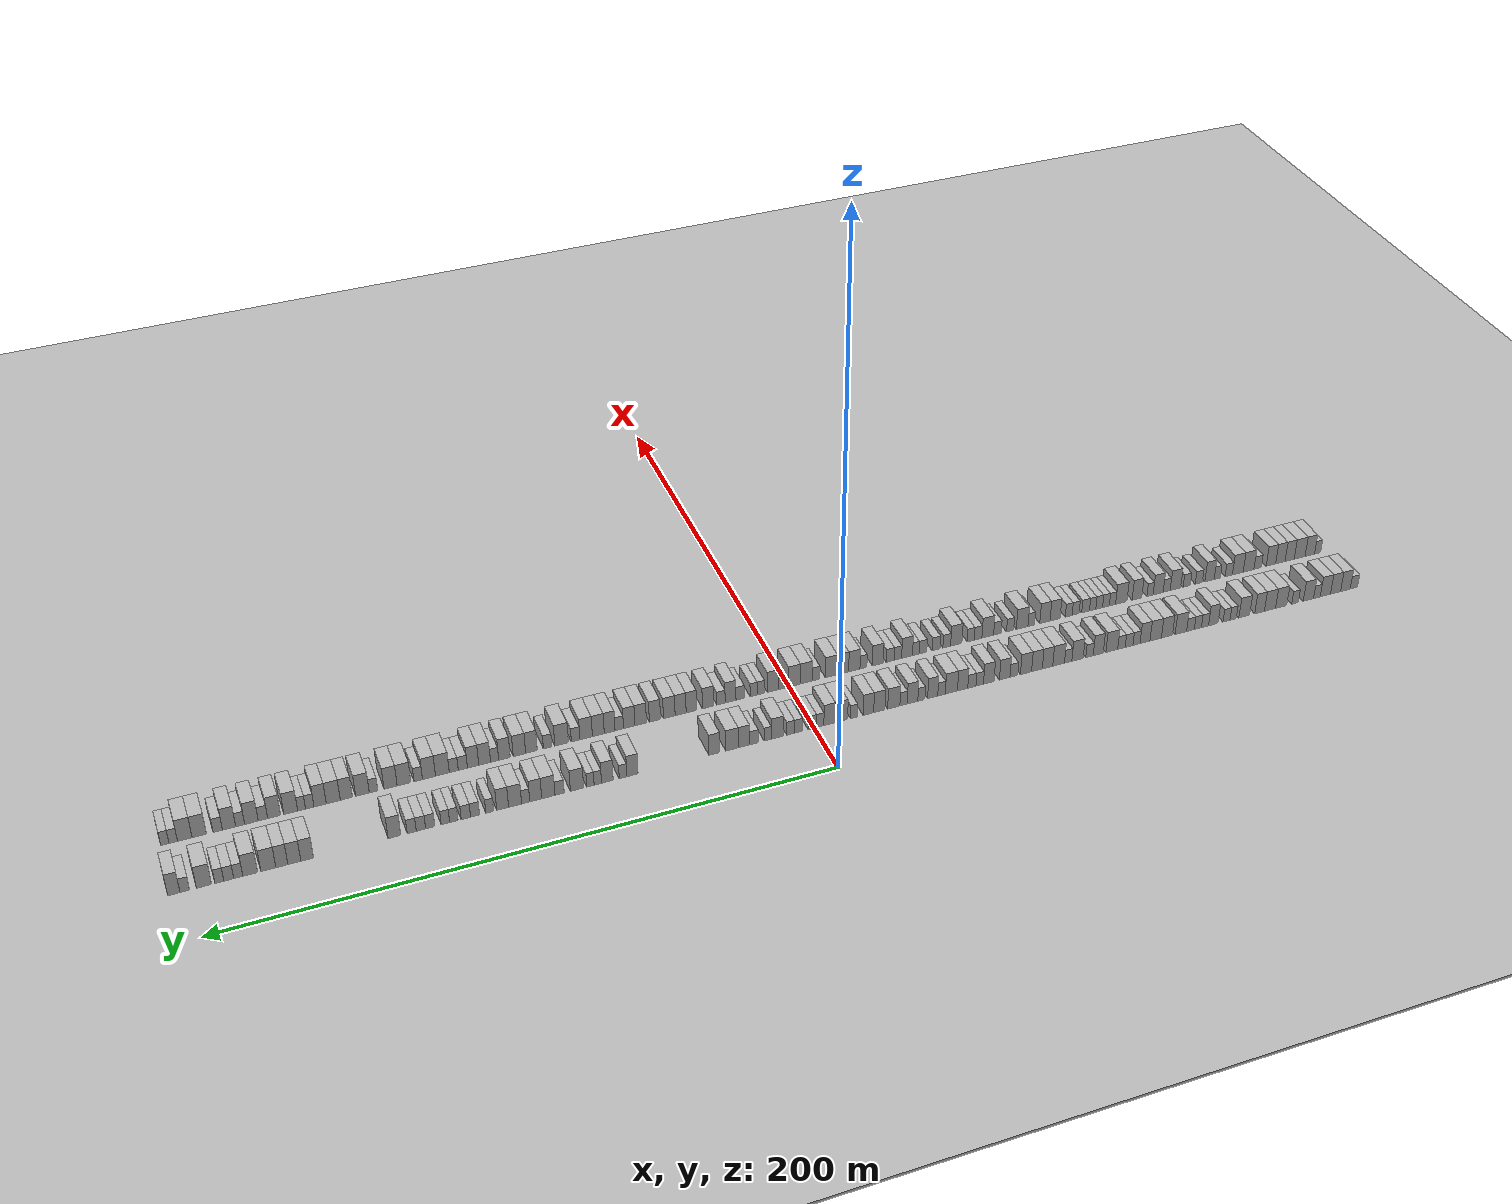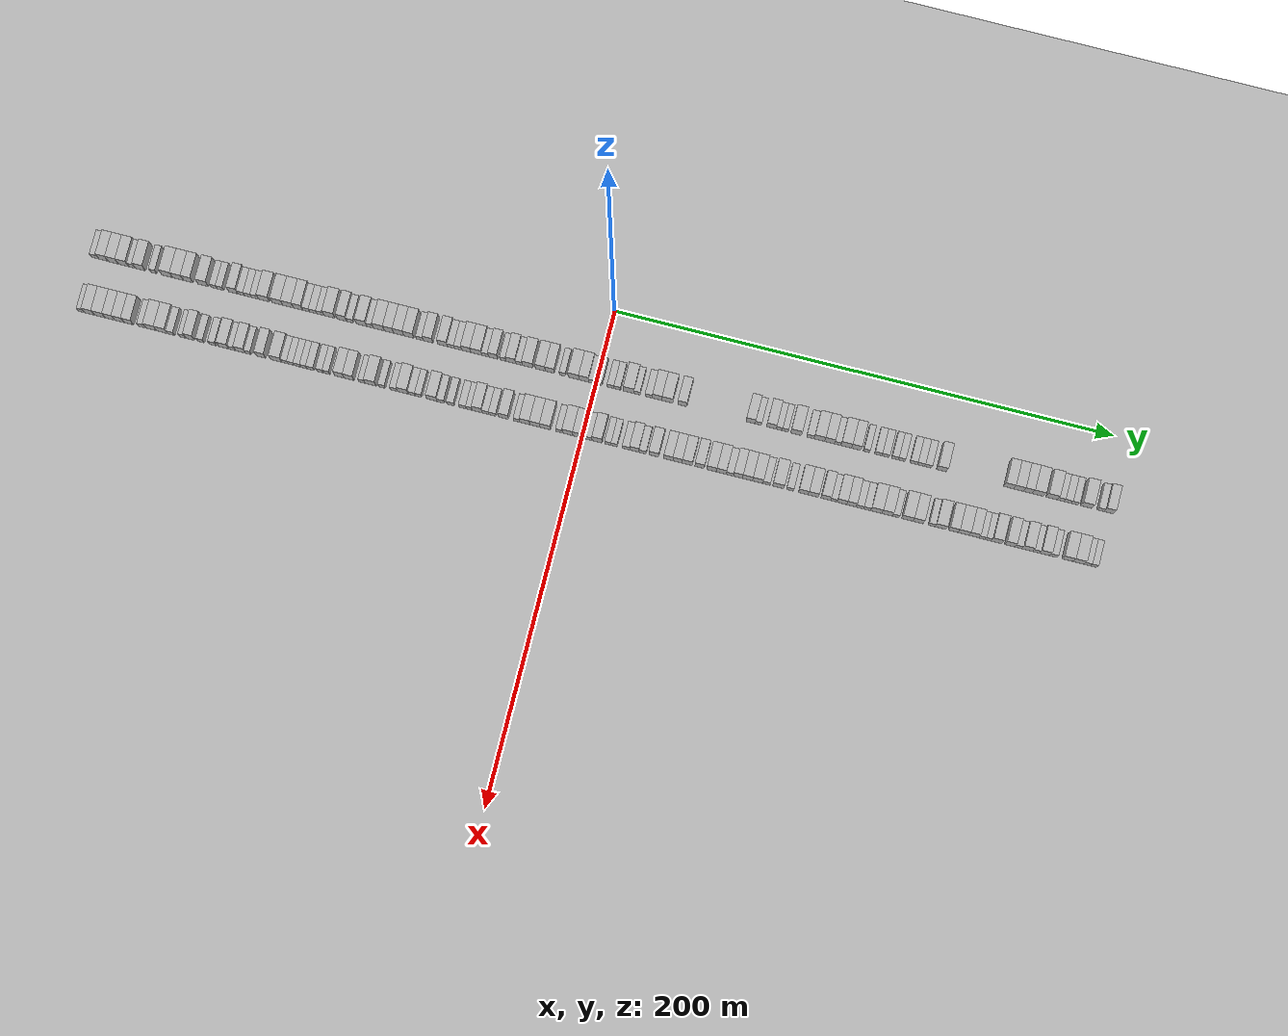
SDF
<?xml version="1.0" encoding="utf-8"?>

<sdf version="1.6">

   <world name="default">

      <gui fullscreen="0">

         <camera name="user_camera">

            <pose>-15 0 4.57585 0 0 0</pose>

            <view_controller>orbit</view_controller>

         </camera>

      </gui>

      <scene>

         <sky>

           <clouds>

             <speed>12</speed>

           </clouds>

         </sky>

         <ambient>0.4 0.4 0.4 1</ambient>

         <background>0.7 0.7 0.7 1</background>

         <shadows>1</shadows>

      </scene>

      <gravity>0 0 -9.8066</gravity>

      <magnetic_field>6e-06 2.3e-05 -4.2e-05</magnetic_field>

      <physics default="0" name="default_physics" type="ode">

         <ode>

            <solver>

               <type>quick</type>

               <iters>10</iters>

               <sor>1.0</sor>

               <use_dynamic_moi_rescaling>0</use_dynamic_moi_rescaling>

            </solver>

            <constraints>

               <cfm>0</cfm>

               <erp>0.2</erp>

               <contact_max_correcting_vel>100</contact_max_correcting_vel>

               <contact_surface_layer>0.001</contact_surface_layer>

            </constraints>

         </ode>

         <max_step_size>0.004</max_step_size>

         <real_time_factor>1</real_time_factor>

         <real_time_update_rate>250</real_time_update_rate>

      </physics>

      <light name="sun" type="directional">

         <cast_shadows>1</cast_shadows>

         <pose>0 0 10 0 0 0</pose>

         <diffuse>0.8 0.8 0.8 1</diffuse>

         <specular>0.2 0.2 0.2 1</specular>

         <attenuation>

            <range>1000</range>

            <constant>0.9</constant>

            <linear>0.01</linear>

            <quadratic>0.001</quadratic>

         </attenuation>

         <direction>-0.5 0.1 -0.9</direction>

      </light>

      <include>

         <name>ground_plane_1</name>

         <uri>model://HANNAS_ground_plane</uri>

         <pose>0 0 0  0 0 0</pose>

      </include>

      <include>

         <name>ground_plane_2</name>

         <uri>model://HANNAS_ground_plane</uri>

         <pose>100 0 0  0 0 0</pose>

      </include>

      <model name="building_1">

         <static>1</static>

         <pose frame="">25.0000 -202.5261 0 0.000000 0.000000 0.000000</pose>

         <link name="link">

            <pose frame="">0 0 3.00 0 0 0</pose>

            <collision name="collision">

               <geometry>

                  <box>

                     <size>10.0000 2.9478 6.0000</size>

                  </box>

               </geometry>

               <max_contacts>10</max_contacts>

               <surface>

                  <contact>

                     <ode/>

                  </contact>

                  <bounce/>

                  <friction>

                     <torsional>

                        <ode/>

                     </torsional>

                     <ode/>

                  </friction>

               </surface>

            </collision>

            <visual name="visual">

               <cast_shadows>0</cast_shadows>

               <geometry>

                  <box>

                     <size>10.0000 2.9478 6.0000</size>

                  </box>

               </geometry>

               <material>

                  <script>

                     <uri>model://HANNAS_wall/materials/scripts</uri>

                     <uri>model://HANNAS_wall/materials/textures</uri>

                     <name>vrc/HANNAS_wall</name>

                  </script>

               </material>

            </visual>

            <self_collide>0</self_collide>

            <enable_wind>0</enable_wind>

            <kinematic>0</kinematic>

         </link>

      </model>

      <model name="building_2">

         <static>1</static>

         <pose frame="">25.0000 -199.0889 0 0.000000 0.000000 0.000000</pose>

         <link name="link">

            <pose frame="">0 0 4.50 0 0 0</pose>

            <collision name="collision">

               <geometry>

                  <box>

                     <size>10.0000 3.9264 9.0000</size>

                  </box>

               </geometry>

               <max_contacts>10</max_contacts>

               <surface>

                  <contact>

                     <ode/>

                  </contact>

                  <bounce/>

                  <friction>

                     <torsional>

                        <ode/>

                     </torsional>

                     <ode/>

                  </friction>

               </surface>

            </collision>

            <visual name="visual">

               <cast_shadows>0</cast_shadows>

               <geometry>

                  <box>

                     <size>10.0000 3.9264 9.0000</size>

                  </box>

               </geometry>

               <material>

                  <script>

                     <uri>model://HANNAS_wall/materials/scripts</uri>

                     <uri>model://HANNAS_wall/materials/textures</uri>

                     <name>vrc/HANNAS_wall</name>

                  </script>

               </material>

            </visual>

            <self_collide>0</self_collide>

            <enable_wind>0</enable_wind>

            <kinematic>0</kinematic>

         </link>

      </model>

      <model name="building_3">

         <static>1</static>

         <pose frame="">25.0000 -195.0800 0 0.000000 0.000000 0.000000</pose>

         <link name="link">

            <pose frame="">0 0 4.50 0 0 0</pose>

            <collision name="collision">

               <geometry>

                  <box>

                     <size>10.0000 4.0915 9.0000</size>

                  </box>

               </geometry>

               <max_contacts>10</max_contacts>

               <surface>

                  <contact>

                     <ode/>

                  </contact>

                  <bounce/>

                  <friction>

                     <torsional>

                        <ode/>

                     </torsional>

                     <ode/>

                  </friction>

               </surface>

            </collision>

            <visual name="visual">

               <cast_shadows>0</cast_shadows>

               <geometry>

                  <box>

                     <size>10.0000 4.0915 9.0000</size>

                  </box>

               </geometry>

               <material>

                  <script>

                     <uri>model://HANNAS_wall/materials/scripts</uri>

                     <uri>model://HANNAS_wall/materials/textures</uri>

                     <name>vrc/HANNAS_wall</name>

                  </script>

               </material>

            </visual>

            <self_collide>0</self_collide>

            <enable_wind>0</enable_wind>

            <kinematic>0</kinematic>

         </link>

      </model>

      <model name="building_4">

         <static>1</static>

         <pose frame="">25.0000 -190.9570 0 0.000000 0.000000 0.000000</pose>

         <link name="link">

            <pose frame="">0 0 4.50 0 0 0</pose>

            <collision name="collision">

               <geometry>

                  <box>

                     <size>10.0000 4.1544 9.0000</size>

                  </box>

               </geometry>

               <max_contacts>10</max_contacts>

               <surface>

                  <contact>

                     <ode/>

                  </contact>

                  <bounce/>

                  <friction>

                     <torsional>

                        <ode/>

                     </torsional>

                     <ode/>

                  </friction>

               </surface>

            </collision>

            <visual name="visual">

               <cast_shadows>0</cast_shadows>

               <geometry>

                  <box>

                     <size>10.0000 4.1544 9.0000</size>

                  </box>

               </geometry>

               <material>

                  <script>

                     <uri>model://HANNAS_wall/materials/scripts</uri>

                     <uri>model://HANNAS_wall/materials/textures</uri>

                     <name>vrc/HANNAS_wall</name>

                  </script>

               </material>

            </visual>

            <self_collide>0</self_collide>

            <enable_wind>0</enable_wind>

            <kinematic>0</kinematic>

         </link>

      </model>

      <model name="building_5">

         <static>1</static>

         <pose frame="">25.0000 -187.5378 0 0.000000 0.000000 0.000000</pose>

         <link name="link">

            <pose frame="">0 0 3.00 0 0 0</pose>

            <collision name="collision">

               <geometry>

                  <box>

                     <size>10.0000 2.6841 6.0000</size>

                  </box>

               </geometry>

               <max_contacts>10</max_contacts>

               <surface>

                  <contact>

                     <ode/>

                  </contact>

                  <bounce/>

                  <friction>

                     <torsional>

                        <ode/>

                     </torsional>

                     <ode/>

                  </friction>

               </surface>

            </collision>

            <visual name="visual">

               <cast_shadows>0</cast_shadows>

               <geometry>

                  <box>

                     <size>10.0000 2.6841 6.0000</size>

                  </box>

               </geometry>

               <material>

                  <script>

                     <uri>model://HANNAS_wall/materials/scripts</uri>

                     <uri>model://HANNAS_wall/materials/textures</uri>

                     <name>vrc/HANNAS_wall</name>

                  </script>

               </material>

            </visual>

            <self_collide>0</self_collide>

            <enable_wind>0</enable_wind>

            <kinematic>0</kinematic>

         </link>

      </model>

      <model name="building_6">

         <static>1</static>

         <pose frame="">25.0000 -184.1339 0 0.000000 0.000000 0.000000</pose>

         <link name="link">

            <pose frame="">0 0 4.50 0 0 0</pose>

            <collision name="collision">

               <geometry>

                  <box>

                     <size>10.0000 4.1236 9.0000</size>

                  </box>

               </geometry>

               <max_contacts>10</max_contacts>

               <surface>

                  <contact>

                     <ode/>

                  </contact>

                  <bounce/>

                  <friction>

                     <torsional>

                        <ode/>

                     </torsional>

                     <ode/>

                  </friction>

               </surface>

            </collision>

            <visual name="visual">

               <cast_shadows>0</cast_shadows>

               <geometry>

                  <box>

                     <size>10.0000 4.1236 9.0000</size>

                  </box>

               </geometry>

               <material>

                  <script>

                     <uri>model://HANNAS_wall/materials/scripts</uri>

                     <uri>model://HANNAS_wall/materials/textures</uri>

                     <name>vrc/HANNAS_wall</name>

                  </script>

               </material>

            </visual>

            <self_collide>0</self_collide>

            <enable_wind>0</enable_wind>

            <kinematic>0</kinematic>

         </link>

      </model>

      <model name="building_7">

         <static>1</static>

         <pose frame="">25.0000 -178.7740 0 0.000000 0.000000 0.000000</pose>

         <link name="link">

            <pose frame="">0 0 3.00 0 0 0</pose>

            <collision name="collision">

               <geometry>

                  <box>

                     <size>10.0000 2.5963 6.0000</size>

                  </box>

               </geometry>

               <max_contacts>10</max_contacts>

               <surface>

                  <contact>

                     <ode/>

                  </contact>

                  <bounce/>

                  <friction>

                     <torsional>

                        <ode/>

                     </torsional>

                     <ode/>

                  </friction>

               </surface>

            </collision>

            <visual name="visual">

               <cast_shadows>0</cast_shadows>

               <geometry>

                  <box>

                     <size>10.0000 2.5963 6.0000</size>

                  </box>

               </geometry>

               <material>

                  <script>

                     <uri>model://HANNAS_wall/materials/scripts</uri>

                     <uri>model://HANNAS_wall/materials/textures</uri>

                     <name>vrc/HANNAS_wall</name>

                  </script>

               </material>

            </visual>

            <self_collide>0</self_collide>

            <enable_wind>0</enable_wind>

            <kinematic>0</kinematic>

         </link>

      </model>

      <model name="building_8">

         <static>1</static>

         <pose frame="">25.0000 -173.2522 0 0.000000 0.000000 0.000000</pose>

         <link name="link">

            <pose frame="">0 0 4.50 0 0 0</pose>

            <collision name="collision">

               <geometry>

                  <box>

                     <size>10.0000 4.4474 9.0000</size>

                  </box>

               </geometry>

               <max_contacts>10</max_contacts>

               <surface>

                  <contact>

                     <ode/>

                  </contact>

                  <bounce/>

                  <friction>

                     <torsional>

                        <ode/>

                     </torsional>

                     <ode/>

                  </friction>

               </surface>

            </collision>

            <visual name="visual">

               <cast_shadows>0</cast_shadows>

               <geometry>

                  <box>

                     <size>10.0000 4.4474 9.0000</size>

                  </box>

               </geometry>

               <material>

                  <script>

                     <uri>model://HANNAS_wall/materials/scripts</uri>

                     <uri>model://HANNAS_wall/materials/textures</uri>

                     <name>vrc/HANNAS_wall</name>

                  </script>

               </material>

            </visual>

            <self_collide>0</self_collide>

            <enable_wind>0</enable_wind>

            <kinematic>0</kinematic>

         </link>

      </model>

      <model name="building_9">

         <static>1</static>

         <pose frame="">25.0000 -168.8298 0 0.000000 0.000000 0.000000</pose>

         <link name="link">

            <pose frame="">0 0 4.50 0 0 0</pose>

            <collision name="collision">

               <geometry>

                  <box>

                     <size>10.0000 4.3973 9.0000</size>

                  </box>

               </geometry>

               <max_contacts>10</max_contacts>

               <surface>

                  <contact>

                     <ode/>

                  </contact>

                  <bounce/>

                  <friction>

                     <torsional>

                        <ode/>

                     </torsional>

                     <ode/>

                  </friction>

               </surface>

            </collision>

            <visual name="visual">

               <cast_shadows>0</cast_shadows>

               <geometry>

                  <box>

                     <size>10.0000 4.3973 9.0000</size>

                  </box>

               </geometry>

               <material>

                  <script>

                     <uri>model://HANNAS_wall/materials/scripts</uri>

                     <uri>model://HANNAS_wall/materials/textures</uri>

                     <name>vrc/HANNAS_wall</name>

                  </script>

               </material>

            </visual>

            <self_collide>0</self_collide>

            <enable_wind>0</enable_wind>

            <kinematic>0</kinematic>

         </link>

      </model>

      <model name="building_10">

         <static>1</static>

         <pose frame="">25.0000 -164.7153 0 0.000000 0.000000 0.000000</pose>

         <link name="link">

            <pose frame="">0 0 4.50 0 0 0</pose>

            <collision name="collision">

               <geometry>

                  <box>

                     <size>10.0000 3.8318 9.0000</size>

                  </box>

               </geometry>

               <max_contacts>10</max_contacts>

               <surface>

                  <contact>

                     <ode/>

                  </contact>

                  <bounce/>

                  <friction>

                     <torsional>

                        <ode/>

                     </torsional>

                     <ode/>

                  </friction>

               </surface>

            </collision>

            <visual name="visual">

               <cast_shadows>0</cast_shadows>

               <geometry>

                  <box>

                     <size>10.0000 3.8318 9.0000</size>

                  </box>

               </geometry>

               <material>

                  <script>

                     <uri>model://HANNAS_wall/materials/scripts</uri>

                     <uri>model://HANNAS_wall/materials/textures</uri>

                     <name>vrc/HANNAS_wall</name>

                  </script>

               </material>

            </visual>

            <self_collide>0</self_collide>

            <enable_wind>0</enable_wind>

            <kinematic>0</kinematic>

         </link>

      </model>

      <model name="building_11">

         <static>1</static>

         <pose frame="">25.0000 -158.6673 0 0.000000 0.000000 0.000000</pose>

         <link name="link">

            <pose frame="">0 0 4.50 0 0 0</pose>

            <collision name="collision">

               <geometry>

                  <box>

                     <size>10.0000 4.2642 9.0000</size>

                  </box>

               </geometry>

               <max_contacts>10</max_contacts>

               <surface>

                  <contact>

                     <ode/>

                  </contact>

                  <bounce/>

                  <friction>

                     <torsional>

                        <ode/>

                     </torsional>

                     <ode/>

                  </friction>

               </surface>

            </collision>

            <visual name="visual">

               <cast_shadows>0</cast_shadows>

               <geometry>

                  <box>

                     <size>10.0000 4.2642 9.0000</size>

                  </box>

               </geometry>

               <material>

                  <script>

                     <uri>model://HANNAS_wall/materials/scripts</uri>

                     <uri>model://HANNAS_wall/materials/textures</uri>

                     <name>vrc/HANNAS_wall</name>

                  </script>

               </material>

            </visual>

            <self_collide>0</self_collide>

            <enable_wind>0</enable_wind>

            <kinematic>0</kinematic>

         </link>

      </model>

      <model name="building_12">

         <static>1</static>

         <pose frame="">25.0000 -154.2892 0 0.000000 0.000000 0.000000</pose>

         <link name="link">

            <pose frame="">0 0 3.00 0 0 0</pose>

            <collision name="collision">

               <geometry>

                  <box>

                     <size>10.0000 2.4920 6.0000</size>

                  </box>

               </geometry>

               <max_contacts>10</max_contacts>

               <surface>

                  <contact>

                     <ode/>

                  </contact>

                  <bounce/>

                  <friction>

                     <torsional>

                        <ode/>

                     </torsional>

                     <ode/>

                  </friction>

               </surface>

            </collision>

            <visual name="visual">

               <cast_shadows>0</cast_shadows>

               <geometry>

                  <box>

                     <size>10.0000 2.4920 6.0000</size>

                  </box>

               </geometry>

               <material>

                  <script>

                     <uri>model://HANNAS_wall/materials/scripts</uri>

                     <uri>model://HANNAS_wall/materials/textures</uri>

                     <name>vrc/HANNAS_wall</name>

                  </script>

               </material>

            </visual>

            <self_collide>0</self_collide>

            <enable_wind>0</enable_wind>

            <kinematic>0</kinematic>

         </link>

      </model>

      <model name="building_13">

         <static>1</static>

         <pose frame="">25.0000 -151.6903 0 0.000000 0.000000 0.000000</pose>

         <link name="link">

            <pose frame="">0 0 3.00 0 0 0</pose>

            <collision name="collision">

               <geometry>

                  <box>

                     <size>10.0000 2.7059 6.0000</size>

                  </box>

               </geometry>

               <max_contacts>10</max_contacts>

               <surface>

                  <contact>

                     <ode/>

                  </contact>

                  <bounce/>

                  <friction>

                     <torsional>

                        <ode/>

                     </torsional>

                     <ode/>

                  </friction>

               </surface>

            </collision>

            <visual name="visual">

               <cast_shadows>0</cast_shadows>

               <geometry>

                  <box>

                     <size>10.0000 2.7059 6.0000</size>

                  </box>

               </geometry>

               <material>

                  <script>

                     <uri>model://HANNAS_wall/materials/scripts</uri>

                     <uri>model://HANNAS_wall/materials/textures</uri>

                     <name>vrc/HANNAS_wall</name>

                  </script>

               </material>

            </visual>

            <self_collide>0</self_collide>

            <enable_wind>0</enable_wind>

            <kinematic>0</kinematic>

         </link>

      </model>

      <model name="building_14">

         <static>1</static>

         <pose frame="">25.0000 -146.4922 0 0.000000 0.000000 0.000000</pose>

         <link name="link">

            <pose frame="">0 0 4.50 0 0 0</pose>

            <collision name="collision">

               <geometry>

                  <box>

                     <size>10.0000 3.6902 9.0000</size>

                  </box>

               </geometry>

               <max_contacts>10</max_contacts>

               <surface>

                  <contact>

                     <ode/>

                  </contact>

                  <bounce/>

                  <friction>

                     <torsional>

                        <ode/>

                     </torsional>

                     <ode/>

                  </friction>

               </surface>

            </collision>

            <visual name="visual">

               <cast_shadows>0</cast_shadows>

               <geometry>

                  <box>

                     <size>10.0000 3.6902 9.0000</size>

                  </box>

               </geometry>

               <material>

                  <script>

                     <uri>model://HANNAS_wall/materials/scripts</uri>

                     <uri>model://HANNAS_wall/materials/textures</uri>

                     <name>vrc/HANNAS_wall</name>

                  </script>

               </material>

            </visual>

            <self_collide>0</self_collide>

            <enable_wind>0</enable_wind>

            <kinematic>0</kinematic>

         </link>

      </model>

      <model name="building_15">

         <static>1</static>

         <pose frame="">25.0000 -143.2801 0 0.000000 0.000000 0.000000</pose>

         <link name="link">

            <pose frame="">0 0 3.00 0 0 0</pose>

            <collision name="collision">

               <geometry>

                  <box>

                     <size>10.0000 2.7340 6.0000</size>

                  </box>

               </geometry>

               <max_contacts>10</max_contacts>

               <surface>

                  <contact>

                     <ode/>

                  </contact>

                  <bounce/>

                  <friction>

                     <torsional>

                        <ode/>

                     </torsional>

                     <ode/>

                  </friction>

               </surface>

            </collision>

            <visual name="visual">

               <cast_shadows>0</cast_shadows>

               <geometry>

                  <box>

                     <size>10.0000 2.7340 6.0000</size>

                  </box>

               </geometry>

               <material>

                  <script>

                     <uri>model://HANNAS_wall/materials/scripts</uri>

                     <uri>model://HANNAS_wall/materials/textures</uri>

                     <name>vrc/HANNAS_wall</name>

                  </script>

               </material>

            </visual>

            <self_collide>0</self_collide>

            <enable_wind>0</enable_wind>

            <kinematic>0</kinematic>

         </link>

      </model>

      <model name="building_16">

         <static>1</static>

         <pose frame="">25.0000 -140.5237 0 0.000000 0.000000 0.000000</pose>

         <link name="link">

            <pose frame="">0 0 3.00 0 0 0</pose>

            <collision name="collision">

               <geometry>

                  <box>

                     <size>10.0000 2.7788 6.0000</size>

                  </box>

               </geometry>

               <max_contacts>10</max_contacts>

               <surface>

                  <contact>

                     <ode/>

                  </contact>

                  <bounce/>

                  <friction>

                     <torsional>

                        <ode/>

                     </torsional>

                     <ode/>

                  </friction>

               </surface>

            </collision>

            <visual name="visual">

               <cast_shadows>0</cast_shadows>

               <geometry>

                  <box>

                     <size>10.0000 2.7788 6.0000</size>

                  </box>

               </geometry>

               <material>

                  <script>

                     <uri>model://HANNAS_wall/materials/scripts</uri>

                     <uri>model://HANNAS_wall/materials/textures</uri>

                     <name>vrc/HANNAS_wall</name>

                  </script>

               </material>

            </visual>

            <self_collide>0</self_collide>

            <enable_wind>0</enable_wind>

            <kinematic>0</kinematic>

         </link>

      </model>

      <model name="building_17">

         <static>1</static>

         <pose frame="">25.0000 -137.6611 0 0.000000 0.000000 0.000000</pose>

         <link name="link">

            <pose frame="">0 0 3.00 0 0 0</pose>

            <collision name="collision">

               <geometry>

                  <box>

                     <size>10.0000 2.9464 6.0000</size>

                  </box>

               </geometry>

               <max_contacts>10</max_contacts>

               <surface>

                  <contact>

                     <ode/>

                  </contact>

                  <bounce/>

                  <friction>

                     <torsional>

                        <ode/>

                     </torsional>

                     <ode/>

                  </friction>

               </surface>

            </collision>

            <visual name="visual">

               <cast_shadows>0</cast_shadows>

               <geometry>

                  <box>

                     <size>10.0000 2.9464 6.0000</size>

                  </box>

               </geometry>

               <material>

                  <script>

                     <uri>model://HANNAS_wall/materials/scripts</uri>

                     <uri>model://HANNAS_wall/materials/textures</uri>

                     <name>vrc/HANNAS_wall</name>

                  </script>

               </material>

            </visual>

            <self_collide>0</self_collide>

            <enable_wind>0</enable_wind>

            <kinematic>0</kinematic>

         </link>

      </model>

      <model name="building_18">

         <static>1</static>

         <pose frame="">25.0000 -133.9481 0 0.000000 0.000000 0.000000</pose>

         <link name="link">

            <pose frame="">0 0 4.50 0 0 0</pose>

            <collision name="collision">

               <geometry>

                  <box>

                     <size>10.0000 4.4797 9.0000</size>

                  </box>

               </geometry>

               <max_contacts>10</max_contacts>

               <surface>

                  <contact>

                     <ode/>

                  </contact>

                  <bounce/>

                  <friction>

                     <torsional>

                        <ode/>

                     </torsional>

                     <ode/>

                  </friction>

               </surface>

            </collision>

            <visual name="visual">

               <cast_shadows>0</cast_shadows>

               <geometry>

                  <box>

                     <size>10.0000 4.4797 9.0000</size>

                  </box>

               </geometry>

               <material>

                  <script>

                     <uri>model://HANNAS_wall/materials/scripts</uri>

                     <uri>model://HANNAS_wall/materials/textures</uri>

                     <name>vrc/HANNAS_wall</name>

                  </script>

               </material>

            </visual>

            <self_collide>0</self_collide>

            <enable_wind>0</enable_wind>

            <kinematic>0</kinematic>

         </link>

      </model>

      <model name="building_19">

         <static>1</static>

         <pose frame="">25.0000 -128.5693 0 0.000000 0.000000 0.000000</pose>

         <link name="link">

            <pose frame="">0 0 4.50 0 0 0</pose>

            <collision name="collision">

               <geometry>

                  <box>

                     <size>10.0000 4.2778 9.0000</size>

                  </box>

               </geometry>

               <max_contacts>10</max_contacts>

               <surface>

                  <contact>

                     <ode/>

                  </contact>

                  <bounce/>

                  <friction>

                     <torsional>

                        <ode/>

                     </torsional>

                     <ode/>

                  </friction>

               </surface>

            </collision>

            <visual name="visual">

               <cast_shadows>0</cast_shadows>

               <geometry>

                  <box>

                     <size>10.0000 4.2778 9.0000</size>

                  </box>

               </geometry>

               <material>

                  <script>

                     <uri>model://HANNAS_wall/materials/scripts</uri>

                     <uri>model://HANNAS_wall/materials/textures</uri>

                     <name>vrc/HANNAS_wall</name>

                  </script>

               </material>

            </visual>

            <self_collide>0</self_collide>

            <enable_wind>0</enable_wind>

            <kinematic>0</kinematic>

         </link>

      </model>

      <model name="building_20">

         <static>1</static>

         <pose frame="">25.0000 -124.2486 0 0.000000 0.000000 0.000000</pose>

         <link name="link">

            <pose frame="">0 0 4.50 0 0 0</pose>

            <collision name="collision">

               <geometry>

                  <box>

                     <size>10.0000 4.3637 9.0000</size>

                  </box>

               </geometry>

               <max_contacts>10</max_contacts>

               <surface>

                  <contact>

                     <ode/>

                  </contact>

                  <bounce/>

                  <friction>

                     <torsional>

                        <ode/>

                     </torsional>

                     <ode/>

                  </friction>

               </surface>

            </collision>

            <visual name="visual">

               <cast_shadows>0</cast_shadows>

               <geometry>

                  <box>

                     <size>10.0000 4.3637 9.0000</size>

                  </box>

               </geometry>

               <material>

                  <script>

                     <uri>model://HANNAS_wall/materials/scripts</uri>

                     <uri>model://HANNAS_wall/materials/textures</uri>

                     <name>vrc/HANNAS_wall</name>

                  </script>

               </material>

            </visual>

            <self_collide>0</self_collide>

            <enable_wind>0</enable_wind>

            <kinematic>0</kinematic>

         </link>

      </model>

      <model name="building_21">

         <static>1</static>

         <pose frame="">25.0000 -120.1668 0 0.000000 0.000000 0.000000</pose>

         <link name="link">

            <pose frame="">0 0 4.50 0 0 0</pose>

            <collision name="collision">

               <geometry>

                  <box>

                     <size>10.0000 3.8000 9.0000</size>

                  </box>

               </geometry>

               <max_contacts>10</max_contacts>

               <surface>

                  <contact>

                     <ode/>

                  </contact>

                  <bounce/>

                  <friction>

                     <torsional>

                        <ode/>

                     </torsional>

                     <ode/>

                  </friction>

               </surface>

            </collision>

            <visual name="visual">

               <cast_shadows>0</cast_shadows>

               <geometry>

                  <box>

                     <size>10.0000 3.8000 9.0000</size>

                  </box>

               </geometry>

               <material>

                  <script>

                     <uri>model://HANNAS_wall/materials/scripts</uri>

                     <uri>model://HANNAS_wall/materials/textures</uri>

                     <name>vrc/HANNAS_wall</name>

                  </script>

               </material>

            </visual>

            <self_collide>0</self_collide>

            <enable_wind>0</enable_wind>

            <kinematic>0</kinematic>

         </link>

      </model>

      <model name="building_22">

         <static>1</static>

         <pose frame="">25.0000 -116.9023 0 0.000000 0.000000 0.000000</pose>

         <link name="link">

            <pose frame="">0 0 3.00 0 0 0</pose>

            <collision name="collision">

               <geometry>

                  <box>

                     <size>10.0000 2.7288 6.0000</size>

                  </box>

               </geometry>

               <max_contacts>10</max_contacts>

               <surface>

                  <contact>

                     <ode/>

                  </contact>

                  <bounce/>

                  <friction>

                     <torsional>

                        <ode/>

                     </torsional>

                     <ode/>

                  </friction>

               </surface>

            </collision>

            <visual name="visual">

               <cast_shadows>0</cast_shadows>

               <geometry>

                  <box>

                     <size>10.0000 2.7288 6.0000</size>

                  </box>

               </geometry>

               <material>

                  <script>

                     <uri>model://HANNAS_wall/materials/scripts</uri>

                     <uri>model://HANNAS_wall/materials/textures</uri>

                     <name>vrc/HANNAS_wall</name>

                  </script>

               </material>

            </visual>

            <self_collide>0</self_collide>

            <enable_wind>0</enable_wind>

            <kinematic>0</kinematic>

         </link>

      </model>

      <model name="building_23">

         <static>1</static>

         <pose frame="">25.0000 -114.0692 0 0.000000 0.000000 0.000000</pose>

         <link name="link">

            <pose frame="">0 0 3.00 0 0 0</pose>

            <collision name="collision">

               <geometry>

                  <box>

                     <size>10.0000 2.9374 6.0000</size>

                  </box>

               </geometry>

               <max_contacts>10</max_contacts>

               <surface>

                  <contact>

                     <ode/>

                  </contact>

                  <bounce/>

                  <friction>

                     <torsional>

                        <ode/>

                     </torsional>

                     <ode/>

                  </friction>

               </surface>

            </collision>

            <visual name="visual">

               <cast_shadows>0</cast_shadows>

               <geometry>

                  <box>

                     <size>10.0000 2.9374 6.0000</size>

                  </box>

               </geometry>

               <material>

                  <script>

                     <uri>model://HANNAS_wall/materials/scripts</uri>

                     <uri>model://HANNAS_wall/materials/textures</uri>

                     <name>vrc/HANNAS_wall</name>

                  </script>

               </material>

            </visual>

            <self_collide>0</self_collide>

            <enable_wind>0</enable_wind>

            <kinematic>0</kinematic>

         </link>

      </model>

      <model name="building_24">

         <static>1</static>

         <pose frame="">25.0000 -111.1918 0 0.000000 0.000000 0.000000</pose>

         <link name="link">

            <pose frame="">0 0 3.00 0 0 0</pose>

            <collision name="collision">

               <geometry>

                  <box>

                     <size>10.0000 2.8174 6.0000</size>

                  </box>

               </geometry>

               <max_contacts>10</max_contacts>

               <surface>

                  <contact>

                     <ode/>

                  </contact>

                  <bounce/>

                  <friction>

                     <torsional>

                        <ode/>

                     </torsional>

                     <ode/>

                  </friction>

               </surface>

            </collision>

            <visual name="visual">

               <cast_shadows>0</cast_shadows>

               <geometry>

                  <box>

                     <size>10.0000 2.8174 6.0000</size>

                  </box>

               </geometry>

               <material>

                  <script>

                     <uri>model://HANNAS_wall/materials/scripts</uri>

                     <uri>model://HANNAS_wall/materials/textures</uri>

                     <name>vrc/HANNAS_wall</name>

                  </script>

               </material>

            </visual>

            <self_collide>0</self_collide>

            <enable_wind>0</enable_wind>

            <kinematic>0</kinematic>

         </link>

      </model>

      <model name="building_25">

         <static>1</static>

         <pose frame="">25.0000 -107.5457 0 0.000000 0.000000 0.000000</pose>

         <link name="link">

            <pose frame="">0 0 4.50 0 0 0</pose>

            <collision name="collision">

               <geometry>

                  <box>

                     <size>10.0000 4.4749 9.0000</size>

                  </box>

               </geometry>

               <max_contacts>10</max_contacts>

               <surface>

                  <contact>

                     <ode/>

                  </contact>

                  <bounce/>

                  <friction>

                     <torsional>

                        <ode/>

                     </torsional>

                     <ode/>

                  </friction>

               </surface>

            </collision>

            <visual name="visual">

               <cast_shadows>0</cast_shadows>

               <geometry>

                  <box>

                     <size>10.0000 4.4749 9.0000</size>

                  </box>

               </geometry>

               <material>

                  <script>

                     <uri>model://HANNAS_wall/materials/scripts</uri>

                     <uri>model://HANNAS_wall/materials/textures</uri>

                     <name>vrc/HANNAS_wall</name>

                  </script>

               </material>

            </visual>

            <self_collide>0</self_collide>

            <enable_wind>0</enable_wind>

            <kinematic>0</kinematic>

         </link>

      </model>

      <model name="building_26">

         <static>1</static>

         <pose frame="">25.0000 -102.4200 0 0.000000 0.000000 0.000000</pose>

         <link name="link">

            <pose frame="">0 0 4.50 0 0 0</pose>

            <collision name="collision">

               <geometry>

                  <box>

                     <size>10.0000 3.7764 9.0000</size>

                  </box>

               </geometry>

               <max_contacts>10</max_contacts>

               <surface>

                  <contact>

                     <ode/>

                  </contact>

                  <bounce/>

                  <friction>

                     <torsional>

                        <ode/>

                     </torsional>

                     <ode/>

                  </friction>

               </surface>

            </collision>

            <visual name="visual">

               <cast_shadows>0</cast_shadows>

               <geometry>

                  <box>

                     <size>10.0000 3.7764 9.0000</size>

                  </box>

               </geometry>

               <material>

                  <script>

                     <uri>model://HANNAS_wall/materials/scripts</uri>

                     <uri>model://HANNAS_wall/materials/textures</uri>

                     <name>vrc/HANNAS_wall</name>

                  </script>

               </material>

            </visual>

            <self_collide>0</self_collide>

            <enable_wind>0</enable_wind>

            <kinematic>0</kinematic>

         </link>

      </model>

      <model name="building_27">

         <static>1</static>

         <pose frame="">25.0000 -99.1316 0 0.000000 0.000000 0.000000</pose>

         <link name="link">

            <pose frame="">0 0 3.00 0 0 0</pose>

            <collision name="collision">

               <geometry>

                  <box>

                     <size>10.0000 2.8005 6.0000</size>

                  </box>

               </geometry>

               <max_contacts>10</max_contacts>

               <surface>

                  <contact>

                     <ode/>

                  </contact>

                  <bounce/>

                  <friction>

                     <torsional>

                        <ode/>

                     </torsional>

                     <ode/>

                  </friction>

               </surface>

            </collision>

            <visual name="visual">

               <cast_shadows>0</cast_shadows>

               <geometry>

                  <box>

                     <size>10.0000 2.8005 6.0000</size>

                  </box>

               </geometry>

               <material>

                  <script>

                     <uri>model://HANNAS_wall/materials/scripts</uri>

                     <uri>model://HANNAS_wall/materials/textures</uri>

                     <name>vrc/HANNAS_wall</name>

                  </script>

               </material>

            </visual>

            <self_collide>0</self_collide>

            <enable_wind>0</enable_wind>

            <kinematic>0</kinematic>

         </link>

      </model>

      <model name="building_28">

         <static>1</static>

         <pose frame="">25.0000 -94.6144 0 0.000000 0.000000 0.000000</pose>

         <link name="link">

            <pose frame="">0 0 4.50 0 0 0</pose>

            <collision name="collision">

               <geometry>

                  <box>

                     <size>10.0000 4.2339 9.0000</size>

                  </box>

               </geometry>

               <max_contacts>10</max_contacts>

               <surface>

                  <contact>

                     <ode/>

                  </contact>

                  <bounce/>

                  <friction>

                     <torsional>

                        <ode/>

                     </torsional>

                     <ode/>

                  </friction>

               </surface>

            </collision>

            <visual name="visual">

               <cast_shadows>0</cast_shadows>

               <geometry>

                  <box>

                     <size>10.0000 4.2339 9.0000</size>

                  </box>

               </geometry>

               <material>

                  <script>

                     <uri>model://HANNAS_wall/materials/scripts</uri>

                     <uri>model://HANNAS_wall/materials/textures</uri>

                     <name>vrc/HANNAS_wall</name>

                  </script>

               </material>

            </visual>

            <self_collide>0</self_collide>

            <enable_wind>0</enable_wind>

            <kinematic>0</kinematic>

         </link>

      </model>

      <model name="building_29">

         <static>1</static>

         <pose frame="">25.0000 -91.1140 0 0.000000 0.000000 0.000000</pose>

         <link name="link">

            <pose frame="">0 0 3.00 0 0 0</pose>

            <collision name="collision">

               <geometry>

                  <box>

                     <size>10.0000 2.7668 6.0000</size>

                  </box>

               </geometry>

               <max_contacts>10</max_contacts>

               <surface>

                  <contact>

                     <ode/>

                  </contact>

                  <bounce/>

                  <friction>

                     <torsional>

                        <ode/>

                     </torsional>

                     <ode/>

                  </friction>

               </surface>

            </collision>

            <visual name="visual">

               <cast_shadows>0</cast_shadows>

               <geometry>

                  <box>

                     <size>10.0000 2.7668 6.0000</size>

                  </box>

               </geometry>

               <material>

                  <script>

                     <uri>model://HANNAS_wall/materials/scripts</uri>

                     <uri>model://HANNAS_wall/materials/textures</uri>

                     <name>vrc/HANNAS_wall</name>

                  </script>

               </material>

            </visual>

            <self_collide>0</self_collide>

            <enable_wind>0</enable_wind>

            <kinematic>0</kinematic>

         </link>

      </model>

      <model name="building_30">

         <static>1</static>

         <pose frame="">25.0000 -87.5491 0 0.000000 0.000000 0.000000</pose>

         <link name="link">

            <pose frame="">0 0 4.50 0 0 0</pose>

            <collision name="collision">

               <geometry>

                  <box>

                     <size>10.0000 4.3629 9.0000</size>

                  </box>

               </geometry>

               <max_contacts>10</max_contacts>

               <surface>

                  <contact>

                     <ode/>

                  </contact>

                  <bounce/>

                  <friction>

                     <torsional>

                        <ode/>

                     </torsional>

                     <ode/>

                  </friction>

               </surface>

            </collision>

            <visual name="visual">

               <cast_shadows>0</cast_shadows>

               <geometry>

                  <box>

                     <size>10.0000 4.3629 9.0000</size>

                  </box>

               </geometry>

               <material>

                  <script>

                     <uri>model://HANNAS_wall/materials/scripts</uri>

                     <uri>model://HANNAS_wall/materials/textures</uri>

                     <name>vrc/HANNAS_wall</name>

                  </script>

               </material>

            </visual>

            <self_collide>0</self_collide>

            <enable_wind>0</enable_wind>

            <kinematic>0</kinematic>

         </link>

      </model>

      <model name="building_31">

         <static>1</static>

         <pose frame="">25.0000 -83.4350 0 0.000000 0.000000 0.000000</pose>

         <link name="link">

            <pose frame="">0 0 4.50 0 0 0</pose>

            <collision name="collision">

               <geometry>

                  <box>

                     <size>10.0000 3.8654 9.0000</size>

                  </box>

               </geometry>

               <max_contacts>10</max_contacts>

               <surface>

                  <contact>

                     <ode/>

                  </contact>

                  <bounce/>

                  <friction>

                     <torsional>

                        <ode/>

                     </torsional>

                     <ode/>

                  </friction>

               </surface>

            </collision>

            <visual name="visual">

               <cast_shadows>0</cast_shadows>

               <geometry>

                  <box>

                     <size>10.0000 3.8654 9.0000</size>

                  </box>

               </geometry>

               <material>

                  <script>

                     <uri>model://HANNAS_wall/materials/scripts</uri>

                     <uri>model://HANNAS_wall/materials/textures</uri>

                     <name>vrc/HANNAS_wall</name>

                  </script>

               </material>

            </visual>

            <self_collide>0</self_collide>

            <enable_wind>0</enable_wind>

            <kinematic>0</kinematic>

         </link>

      </model>

      <model name="building_32">

         <static>1</static>

         <pose frame="">25.0000 -79.5037 0 0.000000 0.000000 0.000000</pose>

         <link name="link">

            <pose frame="">0 0 4.50 0 0 0</pose>

            <collision name="collision">

               <geometry>

                  <box>

                     <size>10.0000 3.9973 9.0000</size>

                  </box>

               </geometry>

               <max_contacts>10</max_contacts>

               <surface>

                  <contact>

                     <ode/>

                  </contact>

                  <bounce/>

                  <friction>

                     <torsional>

                        <ode/>

                     </torsional>

                     <ode/>

                  </friction>

               </surface>

            </collision>

            <visual name="visual">

               <cast_shadows>0</cast_shadows>

               <geometry>

                  <box>

                     <size>10.0000 3.9973 9.0000</size>

                  </box>

               </geometry>

               <material>

                  <script>

                     <uri>model://HANNAS_wall/materials/scripts</uri>

                     <uri>model://HANNAS_wall/materials/textures</uri>

                     <name>vrc/HANNAS_wall</name>

                  </script>

               </material>

            </visual>

            <self_collide>0</self_collide>

            <enable_wind>0</enable_wind>

            <kinematic>0</kinematic>

         </link>

      </model>

      <model name="building_33">

         <static>1</static>

         <pose frame="">25.0000 -75.4474 0 0.000000 0.000000 0.000000</pose>

         <link name="link">

            <pose frame="">0 0 4.50 0 0 0</pose>

            <collision name="collision">

               <geometry>

                  <box>

                     <size>10.0000 4.1154 9.0000</size>

                  </box>

               </geometry>

               <max_contacts>10</max_contacts>

               <surface>

                  <contact>

                     <ode/>

                  </contact>

                  <bounce/>

                  <friction>

                     <torsional>

                        <ode/>

                     </torsional>

                     <ode/>

                  </friction>

               </surface>

            </collision>

            <visual name="visual">

               <cast_shadows>0</cast_shadows>

               <geometry>

                  <box>

                     <size>10.0000 4.1154 9.0000</size>

                  </box>

               </geometry>

               <material>

                  <script>

                     <uri>model://HANNAS_wall/materials/scripts</uri>

                     <uri>model://HANNAS_wall/materials/textures</uri>

                     <name>vrc/HANNAS_wall</name>

                  </script>

               </material>

            </visual>

            <self_collide>0</self_collide>

            <enable_wind>0</enable_wind>

            <kinematic>0</kinematic>

         </link>

      </model>

      <model name="building_34">

         <static>1</static>

         <pose frame="">25.0000 -70.9645 0 0.000000 0.000000 0.000000</pose>

         <link name="link">

            <pose frame="">0 0 3.00 0 0 0</pose>

            <collision name="collision">

               <geometry>

                  <box>

                     <size>10.0000 2.8503 6.0000</size>

                  </box>

               </geometry>

               <max_contacts>10</max_contacts>

               <surface>

                  <contact>

                     <ode/>

                  </contact>

                  <bounce/>

                  <friction>

                     <torsional>

                        <ode/>

                     </torsional>

                     <ode/>

                  </friction>

               </surface>

            </collision>

            <visual name="visual">

               <cast_shadows>0</cast_shadows>

               <geometry>

                  <box>

                     <size>10.0000 2.8503 6.0000</size>

                  </box>

               </geometry>

               <material>

                  <script>

                     <uri>model://HANNAS_wall/materials/scripts</uri>

                     <uri>model://HANNAS_wall/materials/textures</uri>

                     <name>vrc/HANNAS_wall</name>

                  </script>

               </material>

            </visual>

            <self_collide>0</self_collide>

            <enable_wind>0</enable_wind>

            <kinematic>0</kinematic>

         </link>

      </model>

      <model name="building_35">

         <static>1</static>

         <pose frame="">25.0000 -67.6166 0 0.000000 0.000000 0.000000</pose>

         <link name="link">

            <pose frame="">0 0 4.50 0 0 0</pose>

            <collision name="collision">

               <geometry>

                  <box>

                     <size>10.0000 3.8455 9.0000</size>

                  </box>

               </geometry>

               <max_contacts>10</max_contacts>

               <surface>

                  <contact>

                     <ode/>

                  </contact>

                  <bounce/>

                  <friction>

                     <torsional>

                        <ode/>

                     </torsional>

                     <ode/>

                  </friction>

               </surface>

            </collision>

            <visual name="visual">

               <cast_shadows>0</cast_shadows>

               <geometry>

                  <box>

                     <size>10.0000 3.8455 9.0000</size>

                  </box>

               </geometry>

               <material>

                  <script>

                     <uri>model://HANNAS_wall/materials/scripts</uri>

                     <uri>model://HANNAS_wall/materials/textures</uri>

                     <name>vrc/HANNAS_wall</name>

                  </script>

               </material>

            </visual>

            <self_collide>0</self_collide>

            <enable_wind>0</enable_wind>

            <kinematic>0</kinematic>

         </link>

      </model>

      <model name="building_36">

         <static>1</static>

         <pose frame="">25.0000 -61.7630 0 0.000000 0.000000 0.000000</pose>

         <link name="link">

            <pose frame="">0 0 4.50 0 0 0</pose>

            <collision name="collision">

               <geometry>

                  <box>

                     <size>10.0000 3.8618 9.0000</size>

                  </box>

               </geometry>

               <max_contacts>10</max_contacts>

               <surface>

                  <contact>

                     <ode/>

                  </contact>

                  <bounce/>

                  <friction>

                     <torsional>

                        <ode/>

                     </torsional>

                     <ode/>

                  </friction>

               </surface>

            </collision>

            <visual name="visual">

               <cast_shadows>0</cast_shadows>

               <geometry>

                  <box>

                     <size>10.0000 3.8618 9.0000</size>

                  </box>

               </geometry>

               <material>

                  <script>

                     <uri>model://HANNAS_wall/materials/scripts</uri>

                     <uri>model://HANNAS_wall/materials/textures</uri>

                     <name>vrc/HANNAS_wall</name>

                  </script>

               </material>

            </visual>

            <self_collide>0</self_collide>

            <enable_wind>0</enable_wind>

            <kinematic>0</kinematic>

         </link>

      </model>

      <model name="building_37">

         <static>1</static>

         <pose frame="">25.0000 -58.4791 0 0.000000 0.000000 0.000000</pose>

         <link name="link">

            <pose frame="">0 0 3.00 0 0 0</pose>

            <collision name="collision">

               <geometry>

                  <box>

                     <size>10.0000 2.7060 6.0000</size>

                  </box>

               </geometry>

               <max_contacts>10</max_contacts>

               <surface>

                  <contact>

                     <ode/>

                  </contact>

                  <bounce/>

                  <friction>

                     <torsional>

                        <ode/>

                     </torsional>

                     <ode/>

                  </friction>

               </surface>

            </collision>

            <visual name="visual">

               <cast_shadows>0</cast_shadows>

               <geometry>

                  <box>

                     <size>10.0000 2.7060 6.0000</size>

                  </box>

               </geometry>

               <material>

                  <script>

                     <uri>model://HANNAS_wall/materials/scripts</uri>

                     <uri>model://HANNAS_wall/materials/textures</uri>

                     <name>vrc/HANNAS_wall</name>

                  </script>

               </material>

            </visual>

            <self_collide>0</self_collide>

            <enable_wind>0</enable_wind>

            <kinematic>0</kinematic>

         </link>

      </model>

      <model name="building_38">

         <static>1</static>

         <pose frame="">25.0000 -55.6310 0 0.000000 0.000000 0.000000</pose>

         <link name="link">

            <pose frame="">0 0 3.00 0 0 0</pose>

            <collision name="collision">

               <geometry>

                  <box>

                     <size>10.0000 2.9903 6.0000</size>

                  </box>

               </geometry>

               <max_contacts>10</max_contacts>

               <surface>

                  <contact>

                     <ode/>

                  </contact>

                  <bounce/>

                  <friction>

                     <torsional>

                        <ode/>

                     </torsional>

                     <ode/>

                  </friction>

               </surface>

            </collision>

            <visual name="visual">

               <cast_shadows>0</cast_shadows>

               <geometry>

                  <box>

                     <size>10.0000 2.9903 6.0000</size>

                  </box>

               </geometry>

               <material>

                  <script>

                     <uri>model://HANNAS_wall/materials/scripts</uri>

                     <uri>model://HANNAS_wall/materials/textures</uri>

                     <name>vrc/HANNAS_wall</name>

                  </script>

               </material>

            </visual>

            <self_collide>0</self_collide>

            <enable_wind>0</enable_wind>

            <kinematic>0</kinematic>

         </link>

      </model>

      <model name="building_39">

         <static>1</static>

         <pose frame="">25.0000 -52.2686 0 0.000000 0.000000 0.000000</pose>

         <link name="link">

            <pose frame="">0 0 4.50 0 0 0</pose>

            <collision name="collision">

               <geometry>

                  <box>

                     <size>10.0000 3.7345 9.0000</size>

                  </box>

               </geometry>

               <max_contacts>10</max_contacts>

               <surface>

                  <contact>

                     <ode/>

                  </contact>

                  <bounce/>

                  <friction>

                     <torsional>

                        <ode/>

                     </torsional>

                     <ode/>

                  </friction>

               </surface>

            </collision>

            <visual name="visual">

               <cast_shadows>0</cast_shadows>

               <geometry>

                  <box>

                     <size>10.0000 3.7345 9.0000</size>

                  </box>

               </geometry>

               <material>

                  <script>

                     <uri>model://HANNAS_wall/materials/scripts</uri>

                     <uri>model://HANNAS_wall/materials/textures</uri>

                     <name>vrc/HANNAS_wall</name>

                  </script>

               </material>

            </visual>

            <self_collide>0</self_collide>

            <enable_wind>0</enable_wind>

            <kinematic>0</kinematic>

         </link>

      </model>

      <model name="building_40">

         <static>1</static>

         <pose frame="">25.0000 -48.2032 0 0.000000 0.000000 0.000000</pose>

         <link name="link">

            <pose frame="">0 0 4.50 0 0 0</pose>

            <collision name="collision">

               <geometry>

                  <box>

                     <size>10.0000 4.3964 9.0000</size>

                  </box>

               </geometry>

               <max_contacts>10</max_contacts>

               <surface>

                  <contact>

                     <ode/>

                  </contact>

                  <bounce/>

                  <friction>

                     <torsional>

                        <ode/>

                     </torsional>

                     <ode/>

                  </friction>

               </surface>

            </collision>

            <visual name="visual">

               <cast_shadows>0</cast_shadows>

               <geometry>

                  <box>

                     <size>10.0000 4.3964 9.0000</size>

                  </box>

               </geometry>

               <material>

                  <script>

                     <uri>model://HANNAS_wall/materials/scripts</uri>

                     <uri>model://HANNAS_wall/materials/textures</uri>

                     <name>vrc/HANNAS_wall</name>

                  </script>

               </material>

            </visual>

            <self_collide>0</self_collide>

            <enable_wind>0</enable_wind>

            <kinematic>0</kinematic>

         </link>

      </model>

      <model name="building_41">

         <static>1</static>

         <pose frame="">25.0000 -44.6476 0 0.000000 0.000000 0.000000</pose>

         <link name="link">

            <pose frame="">0 0 3.00 0 0 0</pose>

            <collision name="collision">

               <geometry>

                  <box>

                     <size>10.0000 2.7148 6.0000</size>

                  </box>

               </geometry>

               <max_contacts>10</max_contacts>

               <surface>

                  <contact>

                     <ode/>

                  </contact>

                  <bounce/>

                  <friction>

                     <torsional>

                        <ode/>

                     </torsional>

                     <ode/>

                  </friction>

               </surface>

            </collision>

            <visual name="visual">

               <cast_shadows>0</cast_shadows>

               <geometry>

                  <box>

                     <size>10.0000 2.7148 6.0000</size>

                  </box>

               </geometry>

               <material>

                  <script>

                     <uri>model://HANNAS_wall/materials/scripts</uri>

                     <uri>model://HANNAS_wall/materials/textures</uri>

                     <name>vrc/HANNAS_wall</name>

                  </script>

               </material>

            </visual>

            <self_collide>0</self_collide>

            <enable_wind>0</enable_wind>

            <kinematic>0</kinematic>

         </link>

      </model>

      <model name="building_42">

         <static>1</static>

         <pose frame="">25.0000 -41.4667 0 0.000000 0.000000 0.000000</pose>

         <link name="link">

            <pose frame="">0 0 4.50 0 0 0</pose>

            <collision name="collision">

               <geometry>

                  <box>

                     <size>10.0000 3.6469 9.0000</size>

                  </box>

               </geometry>

               <max_contacts>10</max_contacts>

               <surface>

                  <contact>

                     <ode/>

                  </contact>

                  <bounce/>

                  <friction>

                     <torsional>

                        <ode/>

                     </torsional>

                     <ode/>

                  </friction>

               </surface>

            </collision>

            <visual name="visual">

               <cast_shadows>0</cast_shadows>

               <geometry>

                  <box>

                     <size>10.0000 3.6469 9.0000</size>

                  </box>

               </geometry>

               <material>

                  <script>

                     <uri>model://HANNAS_wall/materials/scripts</uri>

                     <uri>model://HANNAS_wall/materials/textures</uri>

                     <name>vrc/HANNAS_wall</name>

                  </script>

               </material>

            </visual>

            <self_collide>0</self_collide>

            <enable_wind>0</enable_wind>

            <kinematic>0</kinematic>

         </link>

      </model>

      <model name="building_43">

         <static>1</static>

         <pose frame="">25.0000 -37.3886 0 0.000000 0.000000 0.000000</pose>

         <link name="link">

            <pose frame="">0 0 3.00 0 0 0</pose>

            <collision name="collision">

               <geometry>

                  <box>

                     <size>10.0000 2.5093 6.0000</size>

                  </box>

               </geometry>

               <max_contacts>10</max_contacts>

               <surface>

                  <contact>

                     <ode/>

                  </contact>

                  <bounce/>

                  <friction>

                     <torsional>

                        <ode/>

                     </torsional>

                     <ode/>

                  </friction>

               </surface>

            </collision>

            <visual name="visual">

               <cast_shadows>0</cast_shadows>

               <geometry>

                  <box>

                     <size>10.0000 2.5093 6.0000</size>

                  </box>

               </geometry>

               <material>

                  <script>

                     <uri>model://HANNAS_wall/materials/scripts</uri>

                     <uri>model://HANNAS_wall/materials/textures</uri>

                     <name>vrc/HANNAS_wall</name>

                  </script>

               </material>

            </visual>

            <self_collide>0</self_collide>

            <enable_wind>0</enable_wind>

            <kinematic>0</kinematic>

         </link>

      </model>

      <model name="building_44">

         <static>1</static>

         <pose frame="">25.0000 -34.2427 0 0.000000 0.000000 0.000000</pose>

         <link name="link">

            <pose frame="">0 0 4.50 0 0 0</pose>

            <collision name="collision">

               <geometry>

                  <box>

                     <size>10.0000 3.7825 9.0000</size>

                  </box>

               </geometry>

               <max_contacts>10</max_contacts>

               <surface>

                  <contact>

                     <ode/>

                  </contact>

                  <bounce/>

                  <friction>

                     <torsional>

                        <ode/>

                     </torsional>

                     <ode/>

                  </friction>

               </surface>

            </collision>

            <visual name="visual">

               <cast_shadows>0</cast_shadows>

               <geometry>

                  <box>

                     <size>10.0000 3.7825 9.0000</size>

                  </box>

               </geometry>

               <material>

                  <script>

                     <uri>model://HANNAS_wall/materials/scripts</uri>

                     <uri>model://HANNAS_wall/materials/textures</uri>

                     <name>vrc/HANNAS_wall</name>

                  </script>

               </material>

            </visual>

            <self_collide>0</self_collide>

            <enable_wind>0</enable_wind>

            <kinematic>0</kinematic>

         </link>

      </model>

      <model name="building_45">

         <static>1</static>

         <pose frame="">25.0000 -31.0395 0 0.000000 0.000000 0.000000</pose>

         <link name="link">

            <pose frame="">0 0 3.00 0 0 0</pose>

            <collision name="collision">

               <geometry>

                  <box>

                     <size>10.0000 2.6238 6.0000</size>

                  </box>

               </geometry>

               <max_contacts>10</max_contacts>

               <surface>

                  <contact>

                     <ode/>

                  </contact>

                  <bounce/>

                  <friction>

                     <torsional>

                        <ode/>

                     </torsional>

                     <ode/>

                  </friction>

               </surface>

            </collision>

            <visual name="visual">

               <cast_shadows>0</cast_shadows>

               <geometry>

                  <box>

                     <size>10.0000 2.6238 6.0000</size>

                  </box>

               </geometry>

               <material>

                  <script>

                     <uri>model://HANNAS_wall/materials/scripts</uri>

                     <uri>model://HANNAS_wall/materials/textures</uri>

                     <name>vrc/HANNAS_wall</name>

                  </script>

               </material>

            </visual>

            <self_collide>0</self_collide>

            <enable_wind>0</enable_wind>

            <kinematic>0</kinematic>

         </link>

      </model>

      <model name="building_46">

         <static>1</static>

         <pose frame="">25.0000 -27.5578 0 0.000000 0.000000 0.000000</pose>

         <link name="link">

            <pose frame="">0 0 4.50 0 0 0</pose>

            <collision name="collision">

               <geometry>

                  <box>

                     <size>10.0000 4.3396 9.0000</size>

                  </box>

               </geometry>

               <max_contacts>10</max_contacts>

               <surface>

                  <contact>

                     <ode/>

                  </contact>

                  <bounce/>

                  <friction>

                     <torsional>

                        <ode/>

                     </torsional>

                     <ode/>

                  </friction>

               </surface>

            </collision>

            <visual name="visual">

               <cast_shadows>0</cast_shadows>

               <geometry>

                  <box>

                     <size>10.0000 4.3396 9.0000</size>

                  </box>

               </geometry>

               <material>

                  <script>

                     <uri>model://HANNAS_wall/materials/scripts</uri>

                     <uri>model://HANNAS_wall/materials/textures</uri>

                     <name>vrc/HANNAS_wall</name>

                  </script>

               </material>

            </visual>

            <self_collide>0</self_collide>

            <enable_wind>0</enable_wind>

            <kinematic>0</kinematic>

         </link>

      </model>

      <model name="building_47">

         <static>1</static>

         <pose frame="">25.0000 -22.4125 0 0.000000 0.000000 0.000000</pose>

         <link name="link">

            <pose frame="">0 0 4.50 0 0 0</pose>

            <collision name="collision">

               <geometry>

                  <box>

                     <size>10.0000 3.9510 9.0000</size>

                  </box>

               </geometry>

               <max_contacts>10</max_contacts>

               <surface>

                  <contact>

                     <ode/>

                  </contact>

                  <bounce/>

                  <friction>

                     <torsional>

                        <ode/>

                     </torsional>

                     <ode/>

                  </friction>

               </surface>

            </collision>

            <visual name="visual">

               <cast_shadows>0</cast_shadows>

               <geometry>

                  <box>

                     <size>10.0000 3.9510 9.0000</size>

                  </box>

               </geometry>

               <material>

                  <script>

                     <uri>model://HANNAS_wall/materials/scripts</uri>

                     <uri>model://HANNAS_wall/materials/textures</uri>

                     <name>vrc/HANNAS_wall</name>

                  </script>

               </material>

            </visual>

            <self_collide>0</self_collide>

            <enable_wind>0</enable_wind>

            <kinematic>0</kinematic>

         </link>

      </model>

      <model name="building_48">

         <static>1</static>

         <pose frame="">25.0000 -18.5852 0 0.000000 0.000000 0.000000</pose>

         <link name="link">

            <pose frame="">0 0 4.50 0 0 0</pose>

            <collision name="collision">

               <geometry>

                  <box>

                     <size>10.0000 3.7035 9.0000</size>

                  </box>

               </geometry>

               <max_contacts>10</max_contacts>

               <surface>

                  <contact>

                     <ode/>

                  </contact>

                  <bounce/>

                  <friction>

                     <torsional>

                        <ode/>

                     </torsional>

                     <ode/>

                  </friction>

               </surface>

            </collision>

            <visual name="visual">

               <cast_shadows>0</cast_shadows>

               <geometry>

                  <box>

                     <size>10.0000 3.7035 9.0000</size>

                  </box>

               </geometry>

               <material>

                  <script>

                     <uri>model://HANNAS_wall/materials/scripts</uri>

                     <uri>model://HANNAS_wall/materials/textures</uri>

                     <name>vrc/HANNAS_wall</name>

                  </script>

               </material>

            </visual>

            <self_collide>0</self_collide>

            <enable_wind>0</enable_wind>

            <kinematic>0</kinematic>

         </link>

      </model>

      <model name="building_49">

         <static>1</static>

         <pose frame="">25.0000 -13.5009 0 0.000000 0.000000 0.000000</pose>

         <link name="link">

            <pose frame="">0 0 3.00 0 0 0</pose>

            <collision name="collision">

               <geometry>

                  <box>

                     <size>10.0000 2.4650 6.0000</size>

                  </box>

               </geometry>

               <max_contacts>10</max_contacts>

               <surface>

                  <contact>

                     <ode/>

                  </contact>

                  <bounce/>

                  <friction>

                     <torsional>

                        <ode/>

                     </torsional>

                     <ode/>

                  </friction>

               </surface>

            </collision>

            <visual name="visual">

               <cast_shadows>0</cast_shadows>

               <geometry>

                  <box>

                     <size>10.0000 2.4650 6.0000</size>

                  </box>

               </geometry>

               <material>

                  <script>

                     <uri>model://HANNAS_wall/materials/scripts</uri>

                     <uri>model://HANNAS_wall/materials/textures</uri>

                     <name>vrc/HANNAS_wall</name>

                  </script>

               </material>

            </visual>

            <self_collide>0</self_collide>

            <enable_wind>0</enable_wind>

            <kinematic>0</kinematic>

         </link>

      </model>

      <model name="building_50">

         <static>1</static>

         <pose frame="">25.0000 -9.0955 0 0.000000 0.000000 0.000000</pose>

         <link name="link">

            <pose frame="">0 0 4.50 0 0 0</pose>

            <collision name="collision">

               <geometry>

                  <box>

                     <size>10.0000 4.3460 9.0000</size>

                  </box>

               </geometry>

               <max_contacts>10</max_contacts>

               <surface>

                  <contact>

                     <ode/>

                  </contact>

                  <bounce/>

                  <friction>

                     <torsional>

                        <ode/>

                     </torsional>

                     <ode/>

                  </friction>

               </surface>

            </collision>

            <visual name="visual">

               <cast_shadows>0</cast_shadows>

               <geometry>

                  <box>

                     <size>10.0000 4.3460 9.0000</size>

                  </box>

               </geometry>

               <material>

                  <script>

                     <uri>model://HANNAS_wall/materials/scripts</uri>

                     <uri>model://HANNAS_wall/materials/textures</uri>

                     <name>vrc/HANNAS_wall</name>

                  </script>

               </material>

            </visual>

            <self_collide>0</self_collide>

            <enable_wind>0</enable_wind>

            <kinematic>0</kinematic>

         </link>

      </model>

      <model name="building_51">

         <static>1</static>

         <pose frame="">25.0000 -4.9324 0 0.000000 0.000000 0.000000</pose>

         <link name="link">

            <pose frame="">0 0 4.50 0 0 0</pose>

            <collision name="collision">

               <geometry>

                  <box>

                     <size>10.0000 3.9801 9.0000</size>

                  </box>

               </geometry>

               <max_contacts>10</max_contacts>

               <surface>

                  <contact>

                     <ode/>

                  </contact>

                  <bounce/>

                  <friction>

                     <torsional>

                        <ode/>

                     </torsional>

                     <ode/>

                  </friction>

               </surface>

            </collision>

            <visual name="visual">

               <cast_shadows>0</cast_shadows>

               <geometry>

                  <box>

                     <size>10.0000 3.9801 9.0000</size>

                  </box>

               </geometry>

               <material>

                  <script>

                     <uri>model://HANNAS_wall/materials/scripts</uri>

                     <uri>model://HANNAS_wall/materials/textures</uri>

                     <name>vrc/HANNAS_wall</name>

                  </script>

               </material>

            </visual>

            <self_collide>0</self_collide>

            <enable_wind>0</enable_wind>

            <kinematic>0</kinematic>

         </link>

      </model>

      <model name="building_52">

         <static>1</static>

         <pose frame="">25.0000 -1.6606 0 0.000000 0.000000 0.000000</pose>

         <link name="link">

            <pose frame="">0 0 3.00 0 0 0</pose>

            <collision name="collision">

               <geometry>

                  <box>

                     <size>10.0000 2.5635 6.0000</size>

                  </box>

               </geometry>

               <max_contacts>10</max_contacts>

               <surface>

                  <contact>

                     <ode/>

                  </contact>

                  <bounce/>

                  <friction>

                     <torsional>

                        <ode/>

                     </torsional>

                     <ode/>

                  </friction>

               </surface>

            </collision>

            <visual name="visual">

               <cast_shadows>0</cast_shadows>

               <geometry>

                  <box>

                     <size>10.0000 2.5635 6.0000</size>

                  </box>

               </geometry>

               <material>

                  <script>

                     <uri>model://HANNAS_wall/materials/scripts</uri>

                     <uri>model://HANNAS_wall/materials/textures</uri>

                     <name>vrc/HANNAS_wall</name>

                  </script>

               </material>

            </visual>

            <self_collide>0</self_collide>

            <enable_wind>0</enable_wind>

            <kinematic>0</kinematic>

         </link>

      </model>

      <model name="building_53">

         <static>1</static>

         <pose frame="">25.0000 1.0606 0 0.000000 0.000000 0.000000</pose>

         <link name="link">

            <pose frame="">0 0 3.00 0 0 0</pose>

            <collision name="collision">

               <geometry>

                  <box>

                     <size>10.0000 2.8790 6.0000</size>

                  </box>

               </geometry>

               <max_contacts>10</max_contacts>

               <surface>

                  <contact>

                     <ode/>

                  </contact>

                  <bounce/>

                  <friction>

                     <torsional>

                        <ode/>

                     </torsional>

                     <ode/>

                  </friction>

               </surface>

            </collision>

            <visual name="visual">

               <cast_shadows>0</cast_shadows>

               <geometry>

                  <box>

                     <size>10.0000 2.8790 6.0000</size>

                  </box>

               </geometry>

               <material>

                  <script>

                     <uri>model://HANNAS_wall/materials/scripts</uri>

                     <uri>model://HANNAS_wall/materials/textures</uri>

                     <name>vrc/HANNAS_wall</name>

                  </script>

               </material>

            </visual>

            <self_collide>0</self_collide>

            <enable_wind>0</enable_wind>

            <kinematic>0</kinematic>

         </link>

      </model>

      <model name="building_54">

         <static>1</static>

         <pose frame="">25.0000 5.8469 0 0.000000 0.000000 0.000000</pose>

         <link name="link">

            <pose frame="">0 0 3.00 0 0 0</pose>

            <collision name="collision">

               <geometry>

                  <box>

                     <size>10.0000 2.6937 6.0000</size>

                  </box>

               </geometry>

               <max_contacts>10</max_contacts>

               <surface>

                  <contact>

                     <ode/>

                  </contact>

                  <bounce/>

                  <friction>

                     <torsional>

                        <ode/>

                     </torsional>

                     <ode/>

                  </friction>

               </surface>

            </collision>

            <visual name="visual">

               <cast_shadows>0</cast_shadows>

               <geometry>

                  <box>

                     <size>10.0000 2.6937 6.0000</size>

                  </box>

               </geometry>

               <material>

                  <script>

                     <uri>model://HANNAS_wall/materials/scripts</uri>

                     <uri>model://HANNAS_wall/materials/textures</uri>

                     <name>vrc/HANNAS_wall</name>

                  </script>

               </material>

            </visual>

            <self_collide>0</self_collide>

            <enable_wind>0</enable_wind>

            <kinematic>0</kinematic>

         </link>

      </model>

      <model name="building_55">

         <static>1</static>

         <pose frame="">25.0000 8.5517 0 0.000000 0.000000 0.000000</pose>

         <link name="link">

            <pose frame="">0 0 3.00 0 0 0</pose>

            <collision name="collision">

               <geometry>

                  <box>

                     <size>10.0000 2.7158 6.0000</size>

                  </box>

               </geometry>

               <max_contacts>10</max_contacts>

               <surface>

                  <contact>

                     <ode/>

                  </contact>

                  <bounce/>

                  <friction>

                     <torsional>

                        <ode/>

                     </torsional>

                     <ode/>

                  </friction>

               </surface>

            </collision>

            <visual name="visual">

               <cast_shadows>0</cast_shadows>

               <geometry>

                  <box>

                     <size>10.0000 2.7158 6.0000</size>

                  </box>

               </geometry>

               <material>

                  <script>

                     <uri>model://HANNAS_wall/materials/scripts</uri>

                     <uri>model://HANNAS_wall/materials/textures</uri>

                     <name>vrc/HANNAS_wall</name>

                  </script>

               </material>

            </visual>

            <self_collide>0</self_collide>

            <enable_wind>0</enable_wind>

            <kinematic>0</kinematic>

         </link>

      </model>

      <model name="building_56">

         <static>1</static>

         <pose frame="">25.0000 13.0838 0 0.000000 0.000000 0.000000</pose>

         <link name="link">

            <pose frame="">0 0 4.50 0 0 0</pose>

            <collision name="collision">

               <geometry>

                  <box>

                     <size>10.0000 4.3484 9.0000</size>

                  </box>

               </geometry>

               <max_contacts>10</max_contacts>

               <surface>

                  <contact>

                     <ode/>

                  </contact>

                  <bounce/>

                  <friction>

                     <torsional>

                        <ode/>

                     </torsional>

                     <ode/>

                  </friction>

               </surface>

            </collision>

            <visual name="visual">

               <cast_shadows>0</cast_shadows>

               <geometry>

                  <box>

                     <size>10.0000 4.3484 9.0000</size>

                  </box>

               </geometry>

               <material>

                  <script>

                     <uri>model://HANNAS_wall/materials/scripts</uri>

                     <uri>model://HANNAS_wall/materials/textures</uri>

                     <name>vrc/HANNAS_wall</name>

                  </script>

               </material>

            </visual>

            <self_collide>0</self_collide>

            <enable_wind>0</enable_wind>

            <kinematic>0</kinematic>

         </link>

      </model>

      <model name="building_57">

         <static>1</static>

         <pose frame="">25.0000 16.4776 0 0.000000 0.000000 0.000000</pose>

         <link name="link">

            <pose frame="">0 0 3.00 0 0 0</pose>

            <collision name="collision">

               <geometry>

                  <box>

                     <size>10.0000 2.4392 6.0000</size>

                  </box>

               </geometry>

               <max_contacts>10</max_contacts>

               <surface>

                  <contact>

                     <ode/>

                  </contact>

                  <bounce/>

                  <friction>

                     <torsional>

                        <ode/>

                     </torsional>

                     <ode/>

                  </friction>

               </surface>

            </collision>

            <visual name="visual">

               <cast_shadows>0</cast_shadows>

               <geometry>

                  <box>

                     <size>10.0000 2.4392 6.0000</size>

                  </box>

               </geometry>

               <material>

                  <script>

                     <uri>model://HANNAS_wall/materials/scripts</uri>

                     <uri>model://HANNAS_wall/materials/textures</uri>

                     <name>vrc/HANNAS_wall</name>

                  </script>

               </material>

            </visual>

            <self_collide>0</self_collide>

            <enable_wind>0</enable_wind>

            <kinematic>0</kinematic>

         </link>

      </model>

      <model name="building_58">

         <static>1</static>

         <pose frame="">25.0000 21.1760 0 0.000000 0.000000 0.000000</pose>

         <link name="link">

            <pose frame="">0 0 3.00 0 0 0</pose>

            <collision name="collision">

               <geometry>

                  <box>

                     <size>10.0000 2.9576 6.0000</size>

                  </box>

               </geometry>

               <max_contacts>10</max_contacts>

               <surface>

                  <contact>

                     <ode/>

                  </contact>

                  <bounce/>

                  <friction>

                     <torsional>

                        <ode/>

                     </torsional>

                     <ode/>

                  </friction>

               </surface>

            </collision>

            <visual name="visual">

               <cast_shadows>0</cast_shadows>

               <geometry>

                  <box>

                     <size>10.0000 2.9576 6.0000</size>

                  </box>

               </geometry>

               <material>

                  <script>

                     <uri>model://HANNAS_wall/materials/scripts</uri>

                     <uri>model://HANNAS_wall/materials/textures</uri>

                     <name>vrc/HANNAS_wall</name>

                  </script>

               </material>

            </visual>

            <self_collide>0</self_collide>

            <enable_wind>0</enable_wind>

            <kinematic>0</kinematic>

         </link>

      </model>

      <model name="building_59">

         <static>1</static>

         <pose frame="">25.0000 24.5634 0 0.000000 0.000000 0.000000</pose>

         <link name="link">

            <pose frame="">0 0 4.50 0 0 0</pose>

            <collision name="collision">

               <geometry>

                  <box>

                     <size>10.0000 3.8172 9.0000</size>

                  </box>

               </geometry>

               <max_contacts>10</max_contacts>

               <surface>

                  <contact>

                     <ode/>

                  </contact>

                  <bounce/>

                  <friction>

                     <torsional>

                        <ode/>

                     </torsional>

                     <ode/>

                  </friction>

               </surface>

            </collision>

            <visual name="visual">

               <cast_shadows>0</cast_shadows>

               <geometry>

                  <box>

                     <size>10.0000 3.8172 9.0000</size>

                  </box>

               </geometry>

               <material>

                  <script>

                     <uri>model://HANNAS_wall/materials/scripts</uri>

                     <uri>model://HANNAS_wall/materials/textures</uri>

                     <name>vrc/HANNAS_wall</name>

                  </script>

               </material>

            </visual>

            <self_collide>0</self_collide>

            <enable_wind>0</enable_wind>

            <kinematic>0</kinematic>

         </link>

      </model>

      <model name="building_60">

         <static>1</static>

         <pose frame="">25.0000 28.6364 0 0.000000 0.000000 0.000000</pose>

         <link name="link">

            <pose frame="">0 0 4.50 0 0 0</pose>

            <collision name="collision">

               <geometry>

                  <box>

                     <size>10.0000 4.3287 9.0000</size>

                  </box>

               </geometry>

               <max_contacts>10</max_contacts>

               <surface>

                  <contact>

                     <ode/>

                  </contact>

                  <bounce/>

                  <friction>

                     <torsional>

                        <ode/>

                     </torsional>

                     <ode/>

                  </friction>

               </surface>

            </collision>

            <visual name="visual">

               <cast_shadows>0</cast_shadows>

               <geometry>

                  <box>

                     <size>10.0000 4.3287 9.0000</size>

                  </box>

               </geometry>

               <material>

                  <script>

                     <uri>model://HANNAS_wall/materials/scripts</uri>

                     <uri>model://HANNAS_wall/materials/textures</uri>

                     <name>vrc/HANNAS_wall</name>

                  </script>

               </material>

            </visual>

            <self_collide>0</self_collide>

            <enable_wind>0</enable_wind>

            <kinematic>0</kinematic>

         </link>

      </model>

      <model name="building_61">

         <static>1</static>

         <pose frame="">25.0000 34.6483 0 0.000000 0.000000 0.000000</pose>

         <link name="link">

            <pose frame="">0 0 4.50 0 0 0</pose>

            <collision name="collision">

               <geometry>

                  <box>

                     <size>10.0000 3.6950 9.0000</size>

                  </box>

               </geometry>

               <max_contacts>10</max_contacts>

               <surface>

                  <contact>

                     <ode/>

                  </contact>

                  <bounce/>

                  <friction>

                     <torsional>

                        <ode/>

                     </torsional>

                     <ode/>

                  </friction>

               </surface>

            </collision>

            <visual name="visual">

               <cast_shadows>0</cast_shadows>

               <geometry>

                  <box>

                     <size>10.0000 3.6950 9.0000</size>

                  </box>

               </geometry>

               <material>

                  <script>

                     <uri>model://HANNAS_wall/materials/scripts</uri>

                     <uri>model://HANNAS_wall/materials/textures</uri>

                     <name>vrc/HANNAS_wall</name>

                  </script>

               </material>

            </visual>

            <self_collide>0</self_collide>

            <enable_wind>0</enable_wind>

            <kinematic>0</kinematic>

         </link>

      </model>

      <model name="building_62">

         <static>1</static>

         <pose frame="">25.0000 62.0389 0 0.000000 0.000000 0.000000</pose>

         <link name="link">

            <pose frame="">0 0 4.50 0 0 0</pose>

            <collision name="collision">

               <geometry>

                  <box>

                     <size>10.0000 3.6954 9.0000</size>

                  </box>

               </geometry>

               <max_contacts>10</max_contacts>

               <surface>

                  <contact>

                     <ode/>

                  </contact>

                  <bounce/>

                  <friction>

                     <torsional>

                        <ode/>

                     </torsional>

                     <ode/>

                  </friction>

               </surface>

            </collision>

            <visual name="visual">

               <cast_shadows>0</cast_shadows>

               <geometry>

                  <box>

                     <size>10.0000 3.6954 9.0000</size>

                  </box>

               </geometry>

               <material>

                  <script>

                     <uri>model://HANNAS_wall/materials/scripts</uri>

                     <uri>model://HANNAS_wall/materials/textures</uri>

                     <name>vrc/HANNAS_wall</name>

                  </script>

               </material>

            </visual>

            <self_collide>0</self_collide>

            <enable_wind>0</enable_wind>

            <kinematic>0</kinematic>

         </link>

      </model>

      <model name="building_63">

         <static>1</static>

         <pose frame="">25.0000 65.1429 0 0.000000 0.000000 0.000000</pose>

         <link name="link">

            <pose frame="">0 0 3.00 0 0 0</pose>

            <collision name="collision">

               <geometry>

                  <box>

                     <size>10.0000 2.5127 6.0000</size>

                  </box>

               </geometry>

               <max_contacts>10</max_contacts>

               <surface>

                  <contact>

                     <ode/>

                  </contact>

                  <bounce/>

                  <friction>

                     <torsional>

                        <ode/>

                     </torsional>

                     <ode/>

                  </friction>

               </surface>

            </collision>

            <visual name="visual">

               <cast_shadows>0</cast_shadows>

               <geometry>

                  <box>

                     <size>10.0000 2.5127 6.0000</size>

                  </box>

               </geometry>

               <material>

                  <script>

                     <uri>model://HANNAS_wall/materials/scripts</uri>

                     <uri>model://HANNAS_wall/materials/textures</uri>

                     <name>vrc/HANNAS_wall</name>

                  </script>

               </material>

            </visual>

            <self_collide>0</self_collide>

            <enable_wind>0</enable_wind>

            <kinematic>0</kinematic>

         </link>

      </model>

      <model name="building_64">

         <static>1</static>

         <pose frame="">25.0000 70.3157 0 0.000000 0.000000 0.000000</pose>

         <link name="link">

            <pose frame="">0 0 4.50 0 0 0</pose>

            <collision name="collision">

               <geometry>

                  <box>

                     <size>10.0000 3.8328 9.0000</size>

                  </box>

               </geometry>

               <max_contacts>10</max_contacts>

               <surface>

                  <contact>

                     <ode/>

                  </contact>

                  <bounce/>

                  <friction>

                     <torsional>

                        <ode/>

                     </torsional>

                     <ode/>

                  </friction>

               </surface>

            </collision>

            <visual name="visual">

               <cast_shadows>0</cast_shadows>

               <geometry>

                  <box>

                     <size>10.0000 3.8328 9.0000</size>

                  </box>

               </geometry>

               <material>

                  <script>

                     <uri>model://HANNAS_wall/materials/scripts</uri>

                     <uri>model://HANNAS_wall/materials/textures</uri>

                     <name>vrc/HANNAS_wall</name>

                  </script>

               </material>

            </visual>

            <self_collide>0</self_collide>

            <enable_wind>0</enable_wind>

            <kinematic>0</kinematic>

         </link>

      </model>

      <model name="building_65">

         <static>1</static>

         <pose frame="">25.0000 73.4399 0 0.000000 0.000000 0.000000</pose>

         <link name="link">

            <pose frame="">0 0 3.00 0 0 0</pose>

            <collision name="collision">

               <geometry>

                  <box>

                     <size>10.0000 2.4156 6.0000</size>

                  </box>

               </geometry>

               <max_contacts>10</max_contacts>

               <surface>

                  <contact>

                     <ode/>

                  </contact>

                  <bounce/>

                  <friction>

                     <torsional>

                        <ode/>

                     </torsional>

                     <ode/>

                  </friction>

               </surface>

            </collision>

            <visual name="visual">

               <cast_shadows>0</cast_shadows>

               <geometry>

                  <box>

                     <size>10.0000 2.4156 6.0000</size>

                  </box>

               </geometry>

               <material>

                  <script>

                     <uri>model://HANNAS_wall/materials/scripts</uri>

                     <uri>model://HANNAS_wall/materials/textures</uri>

                     <name>vrc/HANNAS_wall</name>

                  </script>

               </material>

            </visual>

            <self_collide>0</self_collide>

            <enable_wind>0</enable_wind>

            <kinematic>0</kinematic>

         </link>

      </model>

      <model name="building_66">

         <static>1</static>

         <pose frame="">25.0000 75.8507 0 0.000000 0.000000 0.000000</pose>

         <link name="link">

            <pose frame="">0 0 3.00 0 0 0</pose>

            <collision name="collision">

               <geometry>

                  <box>

                     <size>10.0000 2.4062 6.0000</size>

                  </box>

               </geometry>

               <max_contacts>10</max_contacts>

               <surface>

                  <contact>

                     <ode/>

                  </contact>

                  <bounce/>

                  <friction>

                     <torsional>

                        <ode/>

                     </torsional>

                     <ode/>

                  </friction>

               </surface>

            </collision>

            <visual name="visual">

               <cast_shadows>0</cast_shadows>

               <geometry>

                  <box>

                     <size>10.0000 2.4062 6.0000</size>

                  </box>

               </geometry>

               <material>

                  <script>

                     <uri>model://HANNAS_wall/materials/scripts</uri>

                     <uri>model://HANNAS_wall/materials/textures</uri>

                     <name>vrc/HANNAS_wall</name>

                  </script>

               </material>

            </visual>

            <self_collide>0</self_collide>

            <enable_wind>0</enable_wind>

            <kinematic>0</kinematic>

         </link>

      </model>

      <model name="building_67">

         <static>1</static>

         <pose frame="">25.0000 80.2220 0 0.000000 0.000000 0.000000</pose>

         <link name="link">

            <pose frame="">0 0 4.50 0 0 0</pose>

            <collision name="collision">

               <geometry>

                  <box>

                     <size>10.0000 4.3364 9.0000</size>

                  </box>

               </geometry>

               <max_contacts>10</max_contacts>

               <surface>

                  <contact>

                     <ode/>

                  </contact>

                  <bounce/>

                  <friction>

                     <torsional>

                        <ode/>

                     </torsional>

                     <ode/>

                  </friction>

               </surface>

            </collision>

            <visual name="visual">

               <cast_shadows>0</cast_shadows>

               <geometry>

                  <box>

                     <size>10.0000 4.3364 9.0000</size>

                  </box>

               </geometry>

               <material>

                  <script>

                     <uri>model://HANNAS_wall/materials/scripts</uri>

                     <uri>model://HANNAS_wall/materials/textures</uri>

                     <name>vrc/HANNAS_wall</name>

                  </script>

               </material>

            </visual>

            <self_collide>0</self_collide>

            <enable_wind>0</enable_wind>

            <kinematic>0</kinematic>

         </link>

      </model>

      <model name="building_68">

         <static>1</static>

         <pose frame="">25.0000 85.8815 0 0.000000 0.000000 0.000000</pose>

         <link name="link">

            <pose frame="">0 0 3.00 0 0 0</pose>

            <collision name="collision">

               <geometry>

                  <box>

                     <size>10.0000 2.9826 6.0000</size>

                  </box>

               </geometry>

               <max_contacts>10</max_contacts>

               <surface>

                  <contact>

                     <ode/>

                  </contact>

                  <bounce/>

                  <friction>

                     <torsional>

                        <ode/>

                     </torsional>

                     <ode/>

                  </friction>

               </surface>

            </collision>

            <visual name="visual">

               <cast_shadows>0</cast_shadows>

               <geometry>

                  <box>

                     <size>10.0000 2.9826 6.0000</size>

                  </box>

               </geometry>

               <material>

                  <script>

                     <uri>model://HANNAS_wall/materials/scripts</uri>

                     <uri>model://HANNAS_wall/materials/textures</uri>

                     <name>vrc/HANNAS_wall</name>

                  </script>

               </material>

            </visual>

            <self_collide>0</self_collide>

            <enable_wind>0</enable_wind>

            <kinematic>0</kinematic>

         </link>

      </model>

      <model name="building_69">

         <static>1</static>

         <pose frame="">25.0000 89.5196 0 0.000000 0.000000 0.000000</pose>

         <link name="link">

            <pose frame="">0 0 4.50 0 0 0</pose>

            <collision name="collision">

               <geometry>

                  <box>

                     <size>10.0000 4.2936 9.0000</size>

                  </box>

               </geometry>

               <max_contacts>10</max_contacts>

               <surface>

                  <contact>

                     <ode/>

                  </contact>

                  <bounce/>

                  <friction>

                     <torsional>

                        <ode/>

                     </torsional>

                     <ode/>

                  </friction>

               </surface>

            </collision>

            <visual name="visual">

               <cast_shadows>0</cast_shadows>

               <geometry>

                  <box>

                     <size>10.0000 4.2936 9.0000</size>

                  </box>

               </geometry>

               <material>

                  <script>

                     <uri>model://HANNAS_wall/materials/scripts</uri>

                     <uri>model://HANNAS_wall/materials/textures</uri>

                     <name>vrc/HANNAS_wall</name>

                  </script>

               </material>

            </visual>

            <self_collide>0</self_collide>

            <enable_wind>0</enable_wind>

            <kinematic>0</kinematic>

         </link>

      </model>

      <model name="building_70">

         <static>1</static>

         <pose frame="">25.0000 93.5874 0 0.000000 0.000000 0.000000</pose>

         <link name="link">

            <pose frame="">0 0 4.50 0 0 0</pose>

            <collision name="collision">

               <geometry>

                  <box>

                     <size>10.0000 3.8420 9.0000</size>

                  </box>

               </geometry>

               <max_contacts>10</max_contacts>

               <surface>

                  <contact>

                     <ode/>

                  </contact>

                  <bounce/>

                  <friction>

                     <torsional>

                        <ode/>

                     </torsional>

                     <ode/>

                  </friction>

               </surface>

            </collision>

            <visual name="visual">

               <cast_shadows>0</cast_shadows>

               <geometry>

                  <box>

                     <size>10.0000 3.8420 9.0000</size>

                  </box>

               </geometry>

               <material>

                  <script>

                     <uri>model://HANNAS_wall/materials/scripts</uri>

                     <uri>model://HANNAS_wall/materials/textures</uri>

                     <name>vrc/HANNAS_wall</name>

                  </script>

               </material>

            </visual>

            <self_collide>0</self_collide>

            <enable_wind>0</enable_wind>

            <kinematic>0</kinematic>

         </link>

      </model>

      <model name="building_71">

         <static>1</static>

         <pose frame="">25.0000 96.8201 0 0.000000 0.000000 0.000000</pose>

         <link name="link">

            <pose frame="">0 0 3.00 0 0 0</pose>

            <collision name="collision">

               <geometry>

                  <box>

                     <size>10.0000 2.6233 6.0000</size>

                  </box>

               </geometry>

               <max_contacts>10</max_contacts>

               <surface>

                  <contact>

                     <ode/>

                  </contact>

                  <bounce/>

                  <friction>

                     <torsional>

                        <ode/>

                     </torsional>

                     <ode/>

                  </friction>

               </surface>

            </collision>

            <visual name="visual">

               <cast_shadows>0</cast_shadows>

               <geometry>

                  <box>

                     <size>10.0000 2.6233 6.0000</size>

                  </box>

               </geometry>

               <material>

                  <script>

                     <uri>model://HANNAS_wall/materials/scripts</uri>

                     <uri>model://HANNAS_wall/materials/textures</uri>

                     <name>vrc/HANNAS_wall</name>

                  </script>

               </material>

            </visual>

            <self_collide>0</self_collide>

            <enable_wind>0</enable_wind>

            <kinematic>0</kinematic>

         </link>

      </model>

      <model name="building_72">

         <static>1</static>

         <pose frame="">25.0000 100.2155 0 0.000000 0.000000 0.000000</pose>

         <link name="link">

            <pose frame="">0 0 4.50 0 0 0</pose>

            <collision name="collision">

               <geometry>

                  <box>

                     <size>10.0000 4.1676 9.0000</size>

                  </box>

               </geometry>

               <max_contacts>10</max_contacts>

               <surface>

                  <contact>

                     <ode/>

                  </contact>

                  <bounce/>

                  <friction>

                     <torsional>

                        <ode/>

                     </torsional>

                     <ode/>

                  </friction>

               </surface>

            </collision>

            <visual name="visual">

               <cast_shadows>0</cast_shadows>

               <geometry>

                  <box>

                     <size>10.0000 4.1676 9.0000</size>

                  </box>

               </geometry>

               <material>

                  <script>

                     <uri>model://HANNAS_wall/materials/scripts</uri>

                     <uri>model://HANNAS_wall/materials/textures</uri>

                     <name>vrc/HANNAS_wall</name>

                  </script>

               </material>

            </visual>

            <self_collide>0</self_collide>

            <enable_wind>0</enable_wind>

            <kinematic>0</kinematic>

         </link>

      </model>

      <model name="building_73">

         <static>1</static>

         <pose frame="">25.0000 104.1892 0 0.000000 0.000000 0.000000</pose>

         <link name="link">

            <pose frame="">0 0 4.50 0 0 0</pose>

            <collision name="collision">

               <geometry>

                  <box>

                     <size>10.0000 3.7799 9.0000</size>

                  </box>

               </geometry>

               <max_contacts>10</max_contacts>

               <surface>

                  <contact>

                     <ode/>

                  </contact>

                  <bounce/>

                  <friction>

                     <torsional>

                        <ode/>

                     </torsional>

                     <ode/>

                  </friction>

               </surface>

            </collision>

            <visual name="visual">

               <cast_shadows>0</cast_shadows>

               <geometry>

                  <box>

                     <size>10.0000 3.7799 9.0000</size>

                  </box>

               </geometry>

               <material>

                  <script>

                     <uri>model://HANNAS_wall/materials/scripts</uri>

                     <uri>model://HANNAS_wall/materials/textures</uri>

                     <name>vrc/HANNAS_wall</name>

                  </script>

               </material>

            </visual>

            <self_collide>0</self_collide>

            <enable_wind>0</enable_wind>

            <kinematic>0</kinematic>

         </link>

      </model>

      <model name="building_74">

         <static>1</static>

         <pose frame="">25.0000 108.3183 0 0.000000 0.000000 0.000000</pose>

         <link name="link">

            <pose frame="">0 0 3.00 0 0 0</pose>

            <collision name="collision">

               <geometry>

                  <box>

                     <size>10.0000 2.4783 6.0000</size>

                  </box>

               </geometry>

               <max_contacts>10</max_contacts>

               <surface>

                  <contact>

                     <ode/>

                  </contact>

                  <bounce/>

                  <friction>

                     <torsional>

                        <ode/>

                     </torsional>

                     <ode/>

                  </friction>

               </surface>

            </collision>

            <visual name="visual">

               <cast_shadows>0</cast_shadows>

               <geometry>

                  <box>

                     <size>10.0000 2.4783 6.0000</size>

                  </box>

               </geometry>

               <material>

                  <script>

                     <uri>model://HANNAS_wall/materials/scripts</uri>

                     <uri>model://HANNAS_wall/materials/textures</uri>

                     <name>vrc/HANNAS_wall</name>

                  </script>

               </material>

            </visual>

            <self_collide>0</self_collide>

            <enable_wind>0</enable_wind>

            <kinematic>0</kinematic>

         </link>

      </model>

      <model name="building_75">

         <static>1</static>

         <pose frame="">25.0000 112.9809 0 0.000000 0.000000 0.000000</pose>

         <link name="link">

            <pose frame="">0 0 3.00 0 0 0</pose>

            <collision name="collision">

               <geometry>

                  <box>

                     <size>10.0000 2.8468 6.0000</size>

                  </box>

               </geometry>

               <max_contacts>10</max_contacts>

               <surface>

                  <contact>

                     <ode/>

                  </contact>

                  <bounce/>

                  <friction>

                     <torsional>

                        <ode/>

                     </torsional>

                     <ode/>

                  </friction>

               </surface>

            </collision>

            <visual name="visual">

               <cast_shadows>0</cast_shadows>

               <geometry>

                  <box>

                     <size>10.0000 2.8468 6.0000</size>

                  </box>

               </geometry>

               <material>

                  <script>

                     <uri>model://HANNAS_wall/materials/scripts</uri>

                     <uri>model://HANNAS_wall/materials/textures</uri>

                     <name>vrc/HANNAS_wall</name>

                  </script>

               </material>

            </visual>

            <self_collide>0</self_collide>

            <enable_wind>0</enable_wind>

            <kinematic>0</kinematic>

         </link>

      </model>

      <model name="building_76">

         <static>1</static>

         <pose frame="">25.0000 115.8867 0 0.000000 0.000000 0.000000</pose>

         <link name="link">

            <pose frame="">0 0 3.00 0 0 0</pose>

            <collision name="collision">

               <geometry>

                  <box>

                     <size>10.0000 2.9647 6.0000</size>

                  </box>

               </geometry>

               <max_contacts>10</max_contacts>

               <surface>

                  <contact>

                     <ode/>

                  </contact>

                  <bounce/>

                  <friction>

                     <torsional>

                        <ode/>

                     </torsional>

                     <ode/>

                  </friction>

               </surface>

            </collision>

            <visual name="visual">

               <cast_shadows>0</cast_shadows>

               <geometry>

                  <box>

                     <size>10.0000 2.9647 6.0000</size>

                  </box>

               </geometry>

               <material>

                  <script>

                     <uri>model://HANNAS_wall/materials/scripts</uri>

                     <uri>model://HANNAS_wall/materials/textures</uri>

                     <name>vrc/HANNAS_wall</name>

                  </script>

               </material>

            </visual>

            <self_collide>0</self_collide>

            <enable_wind>0</enable_wind>

            <kinematic>0</kinematic>

         </link>

      </model>

      <model name="building_77">

         <static>1</static>

         <pose frame="">25.0000 119.6824 0 0.000000 0.000000 0.000000</pose>

         <link name="link">

            <pose frame="">0 0 3.00 0 0 0</pose>

            <collision name="collision">

               <geometry>

                  <box>

                     <size>10.0000 2.6267 6.0000</size>

                  </box>

               </geometry>

               <max_contacts>10</max_contacts>

               <surface>

                  <contact>

                     <ode/>

                  </contact>

                  <bounce/>

                  <friction>

                     <torsional>

                        <ode/>

                     </torsional>

                     <ode/>

                  </friction>

               </surface>

            </collision>

            <visual name="visual">

               <cast_shadows>0</cast_shadows>

               <geometry>

                  <box>

                     <size>10.0000 2.6267 6.0000</size>

                  </box>

               </geometry>

               <material>

                  <script>

                     <uri>model://HANNAS_wall/materials/scripts</uri>

                     <uri>model://HANNAS_wall/materials/textures</uri>

                     <name>vrc/HANNAS_wall</name>

                  </script>

               </material>

            </visual>

            <self_collide>0</self_collide>

            <enable_wind>0</enable_wind>

            <kinematic>0</kinematic>

         </link>

      </model>

      <model name="building_78">

         <static>1</static>

         <pose frame="">25.0000 122.3355 0 0.000000 0.000000 0.000000</pose>

         <link name="link">

            <pose frame="">0 0 3.00 0 0 0</pose>

            <collision name="collision">

               <geometry>

                  <box>

                     <size>10.0000 2.6797 6.0000</size>

                  </box>

               </geometry>

               <max_contacts>10</max_contacts>

               <surface>

                  <contact>

                     <ode/>

                  </contact>

                  <bounce/>

                  <friction>

                     <torsional>

                        <ode/>

                     </torsional>

                     <ode/>

                  </friction>

               </surface>

            </collision>

            <visual name="visual">

               <cast_shadows>0</cast_shadows>

               <geometry>

                  <box>

                     <size>10.0000 2.6797 6.0000</size>

                  </box>

               </geometry>

               <material>

                  <script>

                     <uri>model://HANNAS_wall/materials/scripts</uri>

                     <uri>model://HANNAS_wall/materials/textures</uri>

                     <name>vrc/HANNAS_wall</name>

                  </script>

               </material>

            </visual>

            <self_collide>0</self_collide>

            <enable_wind>0</enable_wind>

            <kinematic>0</kinematic>

         </link>

      </model>

      <model name="building_79">

         <static>1</static>

         <pose frame="">25.0000 127.1110 0 0.000000 0.000000 0.000000</pose>

         <link name="link">

            <pose frame="">0 0 3.00 0 0 0</pose>

            <collision name="collision">

               <geometry>

                  <box>

                     <size>10.0000 2.8712 6.0000</size>

                  </box>

               </geometry>

               <max_contacts>10</max_contacts>

               <surface>

                  <contact>

                     <ode/>

                  </contact>

                  <bounce/>

                  <friction>

                     <torsional>

                        <ode/>

                     </torsional>

                     <ode/>

                  </friction>

               </surface>

            </collision>

            <visual name="visual">

               <cast_shadows>0</cast_shadows>

               <geometry>

                  <box>

                     <size>10.0000 2.8712 6.0000</size>

                  </box>

               </geometry>

               <material>

                  <script>

                     <uri>model://HANNAS_wall/materials/scripts</uri>

                     <uri>model://HANNAS_wall/materials/textures</uri>

                     <name>vrc/HANNAS_wall</name>

                  </script>

               </material>

            </visual>

            <self_collide>0</self_collide>

            <enable_wind>0</enable_wind>

            <kinematic>0</kinematic>

         </link>

      </model>

      <model name="building_80">

         <static>1</static>

         <pose frame="">25.0000 130.0078 0 0.000000 0.000000 0.000000</pose>

         <link name="link">

            <pose frame="">0 0 3.00 0 0 0</pose>

            <collision name="collision">

               <geometry>

                  <box>

                     <size>10.0000 2.9224 6.0000</size>

                  </box>

               </geometry>

               <max_contacts>10</max_contacts>

               <surface>

                  <contact>

                     <ode/>

                  </contact>

                  <bounce/>

                  <friction>

                     <torsional>

                        <ode/>

                     </torsional>

                     <ode/>

                  </friction>

               </surface>

            </collision>

            <visual name="visual">

               <cast_shadows>0</cast_shadows>

               <geometry>

                  <box>

                     <size>10.0000 2.9224 6.0000</size>

                  </box>

               </geometry>

               <material>

                  <script>

                     <uri>model://HANNAS_wall/materials/scripts</uri>

                     <uri>model://HANNAS_wall/materials/textures</uri>

                     <name>vrc/HANNAS_wall</name>

                  </script>

               </material>

            </visual>

            <self_collide>0</self_collide>

            <enable_wind>0</enable_wind>

            <kinematic>0</kinematic>

         </link>

      </model>

      <model name="building_81">

         <static>1</static>

         <pose frame="">25.0000 132.8782 0 0.000000 0.000000 0.000000</pose>

         <link name="link">

            <pose frame="">0 0 3.00 0 0 0</pose>

            <collision name="collision">

               <geometry>

                  <box>

                     <size>10.0000 2.8182 6.0000</size>

                  </box>

               </geometry>

               <max_contacts>10</max_contacts>

               <surface>

                  <contact>

                     <ode/>

                  </contact>

                  <bounce/>

                  <friction>

                     <torsional>

                        <ode/>

                     </torsional>

                     <ode/>

                  </friction>

               </surface>

            </collision>

            <visual name="visual">

               <cast_shadows>0</cast_shadows>

               <geometry>

                  <box>

                     <size>10.0000 2.8182 6.0000</size>

                  </box>

               </geometry>

               <material>

                  <script>

                     <uri>model://HANNAS_wall/materials/scripts</uri>

                     <uri>model://HANNAS_wall/materials/textures</uri>

                     <name>vrc/HANNAS_wall</name>

                  </script>

               </material>

            </visual>

            <self_collide>0</self_collide>

            <enable_wind>0</enable_wind>

            <kinematic>0</kinematic>

         </link>

      </model>

      <model name="building_82">

         <static>1</static>

         <pose frame="">25.0000 138.2498 0 0.000000 0.000000 0.000000</pose>

         <link name="link">

            <pose frame="">0 0 4.50 0 0 0</pose>

            <collision name="collision">

               <geometry>

                  <box>

                     <size>10.0000 3.9250 9.0000</size>

                  </box>

               </geometry>

               <max_contacts>10</max_contacts>

               <surface>

                  <contact>

                     <ode/>

                  </contact>

                  <bounce/>

                  <friction>

                     <torsional>

                        <ode/>

                     </torsional>

                     <ode/>

                  </friction>

               </surface>

            </collision>

            <visual name="visual">

               <cast_shadows>0</cast_shadows>

               <geometry>

                  <box>

                     <size>10.0000 3.9250 9.0000</size>

                  </box>

               </geometry>

               <material>

                  <script>

                     <uri>model://HANNAS_wall/materials/scripts</uri>

                     <uri>model://HANNAS_wall/materials/textures</uri>

                     <name>vrc/HANNAS_wall</name>

                  </script>

               </material>

            </visual>

            <self_collide>0</self_collide>

            <enable_wind>0</enable_wind>

            <kinematic>0</kinematic>

         </link>

      </model>

      <model name="building_83">

         <static>1</static>

         <pose frame="">25.0000 164.9916 0 0.000000 0.000000 0.000000</pose>

         <link name="link">

            <pose frame="">0 0 4.50 0 0 0</pose>

            <collision name="collision">

               <geometry>

                  <box>

                     <size>10.0000 3.8529 9.0000</size>

                  </box>

               </geometry>

               <max_contacts>10</max_contacts>

               <surface>

                  <contact>

                     <ode/>

                  </contact>

                  <bounce/>

                  <friction>

                     <torsional>

                        <ode/>

                     </torsional>

                     <ode/>

                  </friction>

               </surface>

            </collision>

            <visual name="visual">

               <cast_shadows>0</cast_shadows>

               <geometry>

                  <box>

                     <size>10.0000 3.8529 9.0000</size>

                  </box>

               </geometry>

               <material>

                  <script>

                     <uri>model://HANNAS_wall/materials/scripts</uri>

                     <uri>model://HANNAS_wall/materials/textures</uri>

                     <name>vrc/HANNAS_wall</name>

                  </script>

               </material>

            </visual>

            <self_collide>0</self_collide>

            <enable_wind>0</enable_wind>

            <kinematic>0</kinematic>

         </link>

      </model>

      <model name="building_84">

         <static>1</static>

         <pose frame="">25.0000 168.8767 0 0.000000 0.000000 0.000000</pose>

         <link name="link">

            <pose frame="">0 0 4.50 0 0 0</pose>

            <collision name="collision">

               <geometry>

                  <box>

                     <size>10.0000 3.9171 9.0000</size>

                  </box>

               </geometry>

               <max_contacts>10</max_contacts>

               <surface>

                  <contact>

                     <ode/>

                  </contact>

                  <bounce/>

                  <friction>

                     <torsional>

                        <ode/>

                     </torsional>

                     <ode/>

                  </friction>

               </surface>

            </collision>

            <visual name="visual">

               <cast_shadows>0</cast_shadows>

               <geometry>

                  <box>

                     <size>10.0000 3.9171 9.0000</size>

                  </box>

               </geometry>

               <material>

                  <script>

                     <uri>model://HANNAS_wall/materials/scripts</uri>

                     <uri>model://HANNAS_wall/materials/textures</uri>

                     <name>vrc/HANNAS_wall</name>

                  </script>

               </material>

            </visual>

            <self_collide>0</self_collide>

            <enable_wind>0</enable_wind>

            <kinematic>0</kinematic>

         </link>

      </model>

      <model name="building_85">

         <static>1</static>

         <pose frame="">25.0000 172.6451 0 0.000000 0.000000 0.000000</pose>

         <link name="link">

            <pose frame="">0 0 4.50 0 0 0</pose>

            <collision name="collision">

               <geometry>

                  <box>

                     <size>10.0000 3.6197 9.0000</size>

                  </box>

               </geometry>

               <max_contacts>10</max_contacts>

               <surface>

                  <contact>

                     <ode/>

                  </contact>

                  <bounce/>

                  <friction>

                     <torsional>

                        <ode/>

                     </torsional>

                     <ode/>

                  </friction>

               </surface>

            </collision>

            <visual name="visual">

               <cast_shadows>0</cast_shadows>

               <geometry>

                  <box>

                     <size>10.0000 3.6197 9.0000</size>

                  </box>

               </geometry>

               <material>

                  <script>

                     <uri>model://HANNAS_wall/materials/scripts</uri>

                     <uri>model://HANNAS_wall/materials/textures</uri>

                     <name>vrc/HANNAS_wall</name>

                  </script>

               </material>

            </visual>

            <self_collide>0</self_collide>

            <enable_wind>0</enable_wind>

            <kinematic>0</kinematic>

         </link>

      </model>

      <model name="building_86">

         <static>1</static>

         <pose frame="">25.0000 176.6981 0 0.000000 0.000000 0.000000</pose>

         <link name="link">

            <pose frame="">0 0 4.50 0 0 0</pose>

            <collision name="collision">

               <geometry>

                  <box>

                     <size>10.0000 4.4865 9.0000</size>

                  </box>

               </geometry>

               <max_contacts>10</max_contacts>

               <surface>

                  <contact>

                     <ode/>

                  </contact>

                  <bounce/>

                  <friction>

                     <torsional>

                        <ode/>

                     </torsional>

                     <ode/>

                  </friction>

               </surface>

            </collision>

            <visual name="visual">

               <cast_shadows>0</cast_shadows>

               <geometry>

                  <box>

                     <size>10.0000 4.4865 9.0000</size>

                  </box>

               </geometry>

               <material>

                  <script>

                     <uri>model://HANNAS_wall/materials/scripts</uri>

                     <uri>model://HANNAS_wall/materials/textures</uri>

                     <name>vrc/HANNAS_wall</name>

                  </script>

               </material>

            </visual>

            <self_collide>0</self_collide>

            <enable_wind>0</enable_wind>

            <kinematic>0</kinematic>

         </link>

      </model>

      <model name="building_87">

         <static>1</static>

         <pose frame="">25.0000 182.1515 0 0.000000 0.000000 0.000000</pose>

         <link name="link">

            <pose frame="">0 0 4.50 0 0 0</pose>

            <collision name="collision">

               <geometry>

                  <box>

                     <size>10.0000 4.4203 9.0000</size>

                  </box>

               </geometry>

               <max_contacts>10</max_contacts>

               <surface>

                  <contact>

                     <ode/>

                  </contact>

                  <bounce/>

                  <friction>

                     <torsional>

                        <ode/>

                     </torsional>

                     <ode/>

                  </friction>

               </surface>

            </collision>

            <visual name="visual">

               <cast_shadows>0</cast_shadows>

               <geometry>

                  <box>

                     <size>10.0000 4.4203 9.0000</size>

                  </box>

               </geometry>

               <material>

                  <script>

                     <uri>model://HANNAS_wall/materials/scripts</uri>

                     <uri>model://HANNAS_wall/materials/textures</uri>

                     <name>vrc/HANNAS_wall</name>

                  </script>

               </material>

            </visual>

            <self_collide>0</self_collide>

            <enable_wind>0</enable_wind>

            <kinematic>0</kinematic>

         </link>

      </model>

      <model name="building_88">

         <static>1</static>

         <pose frame="">25.0000 185.6992 0 0.000000 0.000000 0.000000</pose>

         <link name="link">

            <pose frame="">0 0 3.00 0 0 0</pose>

            <collision name="collision">

               <geometry>

                  <box>

                     <size>10.0000 2.6751 6.0000</size>

                  </box>

               </geometry>

               <max_contacts>10</max_contacts>

               <surface>

                  <contact>

                     <ode/>

                  </contact>

                  <bounce/>

                  <friction>

                     <torsional>

                        <ode/>

                     </torsional>

                     <ode/>

                  </friction>

               </surface>

            </collision>

            <visual name="visual">

               <cast_shadows>0</cast_shadows>

               <geometry>

                  <box>

                     <size>10.0000 2.6751 6.0000</size>

                  </box>

               </geometry>

               <material>

                  <script>

                     <uri>model://HANNAS_wall/materials/scripts</uri>

                     <uri>model://HANNAS_wall/materials/textures</uri>

                     <name>vrc/HANNAS_wall</name>

                  </script>

               </material>

            </visual>

            <self_collide>0</self_collide>

            <enable_wind>0</enable_wind>

            <kinematic>0</kinematic>

         </link>

      </model>

      <model name="building_89">

         <static>1</static>

         <pose frame="">25.0000 188.5170 0 0.000000 0.000000 0.000000</pose>

         <link name="link">

            <pose frame="">0 0 3.00 0 0 0</pose>

            <collision name="collision">

               <geometry>

                  <box>

                     <size>10.0000 2.9605 6.0000</size>

                  </box>

               </geometry>

               <max_contacts>10</max_contacts>

               <surface>

                  <contact>

                     <ode/>

                  </contact>

                  <bounce/>

                  <friction>

                     <torsional>

                        <ode/>

                     </torsional>

                     <ode/>

                  </friction>

               </surface>

            </collision>

            <visual name="visual">

               <cast_shadows>0</cast_shadows>

               <geometry>

                  <box>

                     <size>10.0000 2.9605 6.0000</size>

                  </box>

               </geometry>

               <material>

                  <script>

                     <uri>model://HANNAS_wall/materials/scripts</uri>

                     <uri>model://HANNAS_wall/materials/textures</uri>

                     <name>vrc/HANNAS_wall</name>

                  </script>

               </material>

            </visual>

            <self_collide>0</self_collide>

            <enable_wind>0</enable_wind>

            <kinematic>0</kinematic>

         </link>

      </model>

      <model name="building_90">

         <static>1</static>

         <pose frame="">25.0000 191.3114 0 0.000000 0.000000 0.000000</pose>

         <link name="link">

            <pose frame="">0 0 3.00 0 0 0</pose>

            <collision name="collision">

               <geometry>

                  <box>

                     <size>10.0000 2.6284 6.0000</size>

                  </box>

               </geometry>

               <max_contacts>10</max_contacts>

               <surface>

                  <contact>

                     <ode/>

                  </contact>

                  <bounce/>

                  <friction>

                     <torsional>

                        <ode/>

                     </torsional>

                     <ode/>

                  </friction>

               </surface>

            </collision>

            <visual name="visual">

               <cast_shadows>0</cast_shadows>

               <geometry>

                  <box>

                     <size>10.0000 2.6284 6.0000</size>

                  </box>

               </geometry>

               <material>

                  <script>

                     <uri>model://HANNAS_wall/materials/scripts</uri>

                     <uri>model://HANNAS_wall/materials/textures</uri>

                     <name>vrc/HANNAS_wall</name>

                  </script>

               </material>

            </visual>

            <self_collide>0</self_collide>

            <enable_wind>0</enable_wind>

            <kinematic>0</kinematic>

         </link>

      </model>

      <model name="building_91">

         <static>1</static>

         <pose frame="">25.0000 195.8693 0 0.000000 0.000000 0.000000</pose>

         <link name="link">

            <pose frame="">0 0 4.50 0 0 0</pose>

            <collision name="collision">

               <geometry>

                  <box>

                     <size>10.0000 4.4875 9.0000</size>

                  </box>

               </geometry>

               <max_contacts>10</max_contacts>

               <surface>

                  <contact>

                     <ode/>

                  </contact>

                  <bounce/>

                  <friction>

                     <torsional>

                        <ode/>

                     </torsional>

                     <ode/>

                  </friction>

               </surface>

            </collision>

            <visual name="visual">

               <cast_shadows>0</cast_shadows>

               <geometry>

                  <box>

                     <size>10.0000 4.4875 9.0000</size>

                  </box>

               </geometry>

               <material>

                  <script>

                     <uri>model://HANNAS_wall/materials/scripts</uri>

                     <uri>model://HANNAS_wall/materials/textures</uri>

                     <name>vrc/HANNAS_wall</name>

                  </script>

               </material>

            </visual>

            <self_collide>0</self_collide>

            <enable_wind>0</enable_wind>

            <kinematic>0</kinematic>

         </link>

      </model>

      <model name="building_92">

         <static>1</static>

         <pose frame="">25.0000 201.5171 0 0.000000 0.000000 0.000000</pose>

         <link name="link">

            <pose frame="">0 0 3.00 0 0 0</pose>

            <collision name="collision">

               <geometry>

                  <box>

                     <size>10.0000 2.8082 6.0000</size>

                  </box>

               </geometry>

               <max_contacts>10</max_contacts>

               <surface>

                  <contact>

                     <ode/>

                  </contact>

                  <bounce/>

                  <friction>

                     <torsional>

                        <ode/>

                     </torsional>

                     <ode/>

                  </friction>

               </surface>

            </collision>

            <visual name="visual">

               <cast_shadows>0</cast_shadows>

               <geometry>

                  <box>

                     <size>10.0000 2.8082 6.0000</size>

                  </box>

               </geometry>

               <material>

                  <script>

                     <uri>model://HANNAS_wall/materials/scripts</uri>

                     <uri>model://HANNAS_wall/materials/textures</uri>

                     <name>vrc/HANNAS_wall</name>

                  </script>

               </material>

            </visual>

            <self_collide>0</self_collide>

            <enable_wind>0</enable_wind>

            <kinematic>0</kinematic>

         </link>

      </model>

      <model name="building_93">

         <static>1</static>

         <pose frame="">25.0000 204.7310 0 0.000000 0.000000 0.000000</pose>

         <link name="link">

            <pose frame="">0 0 4.50 0 0 0</pose>

            <collision name="collision">

               <geometry>

                  <box>

                     <size>10.0000 3.6195 9.0000</size>

                  </box>

               </geometry>

               <max_contacts>10</max_contacts>

               <surface>

                  <contact>

                     <ode/>

                  </contact>

                  <bounce/>

                  <friction>

                     <torsional>

                        <ode/>

                     </torsional>

                     <ode/>

                  </friction>

               </surface>

            </collision>

            <visual name="visual">

               <cast_shadows>0</cast_shadows>

               <geometry>

                  <box>

                     <size>10.0000 3.6195 9.0000</size>

                  </box>

               </geometry>

               <material>

                  <script>

                     <uri>model://HANNAS_wall/materials/scripts</uri>

                     <uri>model://HANNAS_wall/materials/textures</uri>

                     <name>vrc/HANNAS_wall</name>

                  </script>

               </material>

            </visual>

            <self_collide>0</self_collide>

            <enable_wind>0</enable_wind>

            <kinematic>0</kinematic>

         </link>

      </model>

      <model name="building_94">

         <static>1</static>

         <pose frame="">47.0000 -201.7271 0 0.000000 0.000000 0.000000</pose>

         <link name="link">

            <pose frame="">0 0 3.00 0 0 0</pose>

            <collision name="collision">

               <geometry>

                  <box>

                     <size>10.0000 2.5458 6.0000</size>

                  </box>

               </geometry>

               <max_contacts>10</max_contacts>

               <surface>

                  <contact>

                     <ode/>

                  </contact>

                  <bounce/>

                  <friction>

                     <torsional>

                        <ode/>

                     </torsional>

                     <ode/>

                  </friction>

               </surface>

            </collision>

            <visual name="visual">

               <cast_shadows>0</cast_shadows>

               <geometry>

                  <box>

                     <size>10.0000 2.5458 6.0000</size>

                  </box>

               </geometry>

               <material>

                  <script>

                     <uri>model://HANNAS_wall/materials/scripts</uri>

                     <uri>model://HANNAS_wall/materials/textures</uri>

                     <name>vrc/HANNAS_wall</name>

                  </script>

               </material>

            </visual>

            <self_collide>0</self_collide>

            <enable_wind>0</enable_wind>

            <kinematic>0</kinematic>

         </link>

      </model>

      <model name="building_95">

         <static>1</static>

         <pose frame="">47.0000 -198.5022 0 0.000000 0.000000 0.000000</pose>

         <link name="link">

            <pose frame="">0 0 4.50 0 0 0</pose>

            <collision name="collision">

               <geometry>

                  <box>

                     <size>10.0000 3.9041 9.0000</size>

                  </box>

               </geometry>

               <max_contacts>10</max_contacts>

               <surface>

                  <contact>

                     <ode/>

                  </contact>

                  <bounce/>

                  <friction>

                     <torsional>

                        <ode/>

                     </torsional>

                     <ode/>

                  </friction>

               </surface>

            </collision>

            <visual name="visual">

               <cast_shadows>0</cast_shadows>

               <geometry>

                  <box>

                     <size>10.0000 3.9041 9.0000</size>

                  </box>

               </geometry>

               <material>

                  <script>

                     <uri>model://HANNAS_wall/materials/scripts</uri>

                     <uri>model://HANNAS_wall/materials/textures</uri>

                     <name>vrc/HANNAS_wall</name>

                  </script>

               </material>

            </visual>

            <self_collide>0</self_collide>

            <enable_wind>0</enable_wind>

            <kinematic>0</kinematic>

         </link>

      </model>

      <model name="building_96">

         <static>1</static>

         <pose frame="">47.0000 -194.3204 0 0.000000 0.000000 0.000000</pose>

         <link name="link">

            <pose frame="">0 0 4.50 0 0 0</pose>

            <collision name="collision">

               <geometry>

                  <box>

                     <size>10.0000 4.4596 9.0000</size>

                  </box>

               </geometry>

               <max_contacts>10</max_contacts>

               <surface>

                  <contact>

                     <ode/>

                  </contact>

                  <bounce/>

                  <friction>

                     <torsional>

                        <ode/>

                     </torsional>

                     <ode/>

                  </friction>

               </surface>

            </collision>

            <visual name="visual">

               <cast_shadows>0</cast_shadows>

               <geometry>

                  <box>

                     <size>10.0000 4.4596 9.0000</size>

                  </box>

               </geometry>

               <material>

                  <script>

                     <uri>model://HANNAS_wall/materials/scripts</uri>

                     <uri>model://HANNAS_wall/materials/textures</uri>

                     <name>vrc/HANNAS_wall</name>

                  </script>

               </material>

            </visual>

            <self_collide>0</self_collide>

            <enable_wind>0</enable_wind>

            <kinematic>0</kinematic>

         </link>

      </model>

      <model name="building_97">

         <static>1</static>

         <pose frame="">47.0000 -190.2249 0 0.000000 0.000000 0.000000</pose>

         <link name="link">

            <pose frame="">0 0 4.50 0 0 0</pose>

            <collision name="collision">

               <geometry>

                  <box>

                     <size>10.0000 3.7313 9.0000</size>

                  </box>

               </geometry>

               <max_contacts>10</max_contacts>

               <surface>

                  <contact>

                     <ode/>

                  </contact>

                  <bounce/>

                  <friction>

                     <torsional>

                        <ode/>

                     </torsional>

                     <ode/>

                  </friction>

               </surface>

            </collision>

            <visual name="visual">

               <cast_shadows>0</cast_shadows>

               <geometry>

                  <box>

                     <size>10.0000 3.7313 9.0000</size>

                  </box>

               </geometry>

               <material>

                  <script>

                     <uri>model://HANNAS_wall/materials/scripts</uri>

                     <uri>model://HANNAS_wall/materials/textures</uri>

                     <name>vrc/HANNAS_wall</name>

                  </script>

               </material>

            </visual>

            <self_collide>0</self_collide>

            <enable_wind>0</enable_wind>

            <kinematic>0</kinematic>

         </link>

      </model>

      <model name="building_98">

         <static>1</static>

         <pose frame="">47.0000 -186.4495 0 0.000000 0.000000 0.000000</pose>

         <link name="link">

            <pose frame="">0 0 4.50 0 0 0</pose>

            <collision name="collision">

               <geometry>

                  <box>

                     <size>10.0000 3.8194 9.0000</size>

                  </box>

               </geometry>

               <max_contacts>10</max_contacts>

               <surface>

                  <contact>

                     <ode/>

                  </contact>

                  <bounce/>

                  <friction>

                     <torsional>

                        <ode/>

                     </torsional>

                     <ode/>

                  </friction>

               </surface>

            </collision>

            <visual name="visual">

               <cast_shadows>0</cast_shadows>

               <geometry>

                  <box>

                     <size>10.0000 3.8194 9.0000</size>

                  </box>

               </geometry>

               <material>

                  <script>

                     <uri>model://HANNAS_wall/materials/scripts</uri>

                     <uri>model://HANNAS_wall/materials/textures</uri>

                     <name>vrc/HANNAS_wall</name>

                  </script>

               </material>

            </visual>

            <self_collide>0</self_collide>

            <enable_wind>0</enable_wind>

            <kinematic>0</kinematic>

         </link>

      </model>

      <model name="building_99">

         <static>1</static>

         <pose frame="">47.0000 -182.5993 0 0.000000 0.000000 0.000000</pose>

         <link name="link">

            <pose frame="">0 0 4.50 0 0 0</pose>

            <collision name="collision">

               <geometry>

                  <box>

                     <size>10.0000 3.8811 9.0000</size>

                  </box>

               </geometry>

               <max_contacts>10</max_contacts>

               <surface>

                  <contact>

                     <ode/>

                  </contact>

                  <bounce/>

                  <friction>

                     <torsional>

                        <ode/>

                     </torsional>

                     <ode/>

                  </friction>

               </surface>

            </collision>

            <visual name="visual">

               <cast_shadows>0</cast_shadows>

               <geometry>

                  <box>

                     <size>10.0000 3.8811 9.0000</size>

                  </box>

               </geometry>

               <material>

                  <script>

                     <uri>model://HANNAS_wall/materials/scripts</uri>

                     <uri>model://HANNAS_wall/materials/textures</uri>

                     <name>vrc/HANNAS_wall</name>

                  </script>

               </material>

            </visual>

            <self_collide>0</self_collide>

            <enable_wind>0</enable_wind>

            <kinematic>0</kinematic>

         </link>

      </model>

      <model name="building_100">

         <static>1</static>

         <pose frame="">47.0000 -177.1809 0 0.000000 0.000000 0.000000</pose>

         <link name="link">

            <pose frame="">0 0 3.00 0 0 0</pose>

            <collision name="collision">

               <geometry>

                  <box>

                     <size>10.0000 2.9557 6.0000</size>

                  </box>

               </geometry>

               <max_contacts>10</max_contacts>

               <surface>

                  <contact>

                     <ode/>

                  </contact>

                  <bounce/>

                  <friction>

                     <torsional>

                        <ode/>

                     </torsional>

                     <ode/>

                  </friction>

               </surface>

            </collision>

            <visual name="visual">

               <cast_shadows>0</cast_shadows>

               <geometry>

                  <box>

                     <size>10.0000 2.9557 6.0000</size>

                  </box>

               </geometry>

               <material>

                  <script>

                     <uri>model://HANNAS_wall/materials/scripts</uri>

                     <uri>model://HANNAS_wall/materials/textures</uri>

                     <name>vrc/HANNAS_wall</name>

                  </script>

               </material>

            </visual>

            <self_collide>0</self_collide>

            <enable_wind>0</enable_wind>

            <kinematic>0</kinematic>

         </link>

      </model>

      <model name="building_101">

         <static>1</static>

         <pose frame="">47.0000 -173.5213 0 0.000000 0.000000 0.000000</pose>

         <link name="link">

            <pose frame="">0 0 4.50 0 0 0</pose>

            <collision name="collision">

               <geometry>

                  <box>

                     <size>10.0000 4.3636 9.0000</size>

                  </box>

               </geometry>

               <max_contacts>10</max_contacts>

               <surface>

                  <contact>

                     <ode/>

                  </contact>

                  <bounce/>

                  <friction>

                     <torsional>

                        <ode/>

                     </torsional>

                     <ode/>

                  </friction>

               </surface>

            </collision>

            <visual name="visual">

               <cast_shadows>0</cast_shadows>

               <geometry>

                  <box>

                     <size>10.0000 4.3636 9.0000</size>

                  </box>

               </geometry>

               <material>

                  <script>

                     <uri>model://HANNAS_wall/materials/scripts</uri>

                     <uri>model://HANNAS_wall/materials/textures</uri>

                     <name>vrc/HANNAS_wall</name>

                  </script>

               </material>

            </visual>

            <self_collide>0</self_collide>

            <enable_wind>0</enable_wind>

            <kinematic>0</kinematic>

         </link>

      </model>

      <model name="building_102">

         <static>1</static>

         <pose frame="">47.0000 -169.1672 0 0.000000 0.000000 0.000000</pose>

         <link name="link">

            <pose frame="">0 0 4.50 0 0 0</pose>

            <collision name="collision">

               <geometry>

                  <box>

                     <size>10.0000 4.3445 9.0000</size>

                  </box>

               </geometry>

               <max_contacts>10</max_contacts>

               <surface>

                  <contact>

                     <ode/>

                  </contact>

                  <bounce/>

                  <friction>

                     <torsional>

                        <ode/>

                     </torsional>

                     <ode/>

                  </friction>

               </surface>

            </collision>

            <visual name="visual">

               <cast_shadows>0</cast_shadows>

               <geometry>

                  <box>

                     <size>10.0000 4.3445 9.0000</size>

                  </box>

               </geometry>

               <material>

                  <script>

                     <uri>model://HANNAS_wall/materials/scripts</uri>

                     <uri>model://HANNAS_wall/materials/textures</uri>

                     <name>vrc/HANNAS_wall</name>

                  </script>

               </material>

            </visual>

            <self_collide>0</self_collide>

            <enable_wind>0</enable_wind>

            <kinematic>0</kinematic>

         </link>

      </model>

      <model name="building_103">

         <static>1</static>

         <pose frame="">47.0000 -165.5342 0 0.000000 0.000000 0.000000</pose>

         <link name="link">

            <pose frame="">0 0 3.00 0 0 0</pose>

            <collision name="collision">

               <geometry>

                  <box>

                     <size>10.0000 2.9216 6.0000</size>

                  </box>

               </geometry>

               <max_contacts>10</max_contacts>

               <surface>

                  <contact>

                     <ode/>

                  </contact>

                  <bounce/>

                  <friction>

                     <torsional>

                        <ode/>

                     </torsional>

                     <ode/>

                  </friction>

               </surface>

            </collision>

            <visual name="visual">

               <cast_shadows>0</cast_shadows>

               <geometry>

                  <box>

                     <size>10.0000 2.9216 6.0000</size>

                  </box>

               </geometry>

               <material>

                  <script>

                     <uri>model://HANNAS_wall/materials/scripts</uri>

                     <uri>model://HANNAS_wall/materials/textures</uri>

                     <name>vrc/HANNAS_wall</name>

                  </script>

               </material>

            </visual>

            <self_collide>0</self_collide>

            <enable_wind>0</enable_wind>

            <kinematic>0</kinematic>

         </link>

      </model>

      <model name="building_104">

         <static>1</static>

         <pose frame="">47.0000 -160.8596 0 0.000000 0.000000 0.000000</pose>

         <link name="link">

            <pose frame="">0 0 3.00 0 0 0</pose>

            <collision name="collision">

               <geometry>

                  <box>

                     <size>10.0000 2.4276 6.0000</size>

                  </box>

               </geometry>

               <max_contacts>10</max_contacts>

               <surface>

                  <contact>

                     <ode/>

                  </contact>

                  <bounce/>

                  <friction>

                     <torsional>

                        <ode/>

                     </torsional>

                     <ode/>

                  </friction>

               </surface>

            </collision>

            <visual name="visual">

               <cast_shadows>0</cast_shadows>

               <geometry>

                  <box>

                     <size>10.0000 2.4276 6.0000</size>

                  </box>

               </geometry>

               <material>

                  <script>

                     <uri>model://HANNAS_wall/materials/scripts</uri>

                     <uri>model://HANNAS_wall/materials/textures</uri>

                     <name>vrc/HANNAS_wall</name>

                  </script>

               </material>

            </visual>

            <self_collide>0</self_collide>

            <enable_wind>0</enable_wind>

            <kinematic>0</kinematic>

         </link>

      </model>

      <model name="building_105">

         <static>1</static>

         <pose frame="">47.0000 -157.8012 0 0.000000 0.000000 0.000000</pose>

         <link name="link">

            <pose frame="">0 0 4.50 0 0 0</pose>

            <collision name="collision">

               <geometry>

                  <box>

                     <size>10.0000 3.6892 9.0000</size>

                  </box>

               </geometry>

               <max_contacts>10</max_contacts>

               <surface>

                  <contact>

                     <ode/>

                  </contact>

                  <bounce/>

                  <friction>

                     <torsional>

                        <ode/>

                     </torsional>

                     <ode/>

                  </friction>

               </surface>

            </collision>

            <visual name="visual">

               <cast_shadows>0</cast_shadows>

               <geometry>

                  <box>

                     <size>10.0000 3.6892 9.0000</size>

                  </box>

               </geometry>

               <material>

                  <script>

                     <uri>model://HANNAS_wall/materials/scripts</uri>

                     <uri>model://HANNAS_wall/materials/textures</uri>

                     <name>vrc/HANNAS_wall</name>

                  </script>

               </material>

            </visual>

            <self_collide>0</self_collide>

            <enable_wind>0</enable_wind>

            <kinematic>0</kinematic>

         </link>

      </model>

      <model name="building_106">

         <static>1</static>

         <pose frame="">47.0000 -153.5254 0 0.000000 0.000000 0.000000</pose>

         <link name="link">

            <pose frame="">0 0 3.00 0 0 0</pose>

            <collision name="collision">

               <geometry>

                  <box>

                     <size>10.0000 2.8625 6.0000</size>

                  </box>

               </geometry>

               <max_contacts>10</max_contacts>

               <surface>

                  <contact>

                     <ode/>

                  </contact>

                  <bounce/>

                  <friction>

                     <torsional>

                        <ode/>

                     </torsional>

                     <ode/>

                  </friction>

               </surface>

            </collision>

            <visual name="visual">

               <cast_shadows>0</cast_shadows>

               <geometry>

                  <box>

                     <size>10.0000 2.8625 6.0000</size>

                  </box>

               </geometry>

               <material>

                  <script>

                     <uri>model://HANNAS_wall/materials/scripts</uri>

                     <uri>model://HANNAS_wall/materials/textures</uri>

                     <name>vrc/HANNAS_wall</name>

                  </script>

               </material>

            </visual>

            <self_collide>0</self_collide>

            <enable_wind>0</enable_wind>

            <kinematic>0</kinematic>

         </link>

      </model>

      <model name="building_107">

         <static>1</static>

         <pose frame="">47.0000 -148.6903 0 0.000000 0.000000 0.000000</pose>

         <link name="link">

            <pose frame="">0 0 3.00 0 0 0</pose>

            <collision name="collision">

               <geometry>

                  <box>

                     <size>10.0000 2.8077 6.0000</size>

                  </box>

               </geometry>

               <max_contacts>10</max_contacts>

               <surface>

                  <contact>

                     <ode/>

                  </contact>

                  <bounce/>

                  <friction>

                     <torsional>

                        <ode/>

                     </torsional>

                     <ode/>

                  </friction>

               </surface>

            </collision>

            <visual name="visual">

               <cast_shadows>0</cast_shadows>

               <geometry>

                  <box>

                     <size>10.0000 2.8077 6.0000</size>

                  </box>

               </geometry>

               <material>

                  <script>

                     <uri>model://HANNAS_wall/materials/scripts</uri>

                     <uri>model://HANNAS_wall/materials/textures</uri>

                     <name>vrc/HANNAS_wall</name>

                  </script>

               </material>

            </visual>

            <self_collide>0</self_collide>

            <enable_wind>0</enable_wind>

            <kinematic>0</kinematic>

         </link>

      </model>

      <model name="building_108">

         <static>1</static>

         <pose frame="">47.0000 -144.2172 0 0.000000 0.000000 0.000000</pose>

         <link name="link">

            <pose frame="">0 0 4.50 0 0 0</pose>

            <collision name="collision">

               <geometry>

                  <box>

                     <size>10.0000 4.1384 9.0000</size>

                  </box>

               </geometry>

               <max_contacts>10</max_contacts>

               <surface>

                  <contact>

                     <ode/>

                  </contact>

                  <bounce/>

                  <friction>

                     <torsional>

                        <ode/>

                     </torsional>

                     <ode/>

                  </friction>

               </surface>

            </collision>

            <visual name="visual">

               <cast_shadows>0</cast_shadows>

               <geometry>

                  <box>

                     <size>10.0000 4.1384 9.0000</size>

                  </box>

               </geometry>

               <material>

                  <script>

                     <uri>model://HANNAS_wall/materials/scripts</uri>

                     <uri>model://HANNAS_wall/materials/textures</uri>

                     <name>vrc/HANNAS_wall</name>

                  </script>

               </material>

            </visual>

            <self_collide>0</self_collide>

            <enable_wind>0</enable_wind>

            <kinematic>0</kinematic>

         </link>

      </model>

      <model name="building_109">

         <static>1</static>

         <pose frame="">47.0000 -140.7679 0 0.000000 0.000000 0.000000</pose>

         <link name="link">

            <pose frame="">0 0 3.00 0 0 0</pose>

            <collision name="collision">

               <geometry>

                  <box>

                     <size>10.0000 2.7602 6.0000</size>

                  </box>

               </geometry>

               <max_contacts>10</max_contacts>

               <surface>

                  <contact>

                     <ode/>

                  </contact>

                  <bounce/>

                  <friction>

                     <torsional>

                        <ode/>

                     </torsional>

                     <ode/>

                  </friction>

               </surface>

            </collision>

            <visual name="visual">

               <cast_shadows>0</cast_shadows>

               <geometry>

                  <box>

                     <size>10.0000 2.7602 6.0000</size>

                  </box>

               </geometry>

               <material>

                  <script>

                     <uri>model://HANNAS_wall/materials/scripts</uri>

                     <uri>model://HANNAS_wall/materials/textures</uri>

                     <name>vrc/HANNAS_wall</name>

                  </script>

               </material>

            </visual>

            <self_collide>0</self_collide>

            <enable_wind>0</enable_wind>

            <kinematic>0</kinematic>

         </link>

      </model>

      <model name="building_110">

         <static>1</static>

         <pose frame="">47.0000 -137.4171 0 0.000000 0.000000 0.000000</pose>

         <link name="link">

            <pose frame="">0 0 4.50 0 0 0</pose>

            <collision name="collision">

               <geometry>

                  <box>

                     <size>10.0000 3.9414 9.0000</size>

                  </box>

               </geometry>

               <max_contacts>10</max_contacts>

               <surface>

                  <contact>

                     <ode/>

                  </contact>

                  <bounce/>

                  <friction>

                     <torsional>

                        <ode/>

                     </torsional>

                     <ode/>

                  </friction>

               </surface>

            </collision>

            <visual name="visual">

               <cast_shadows>0</cast_shadows>

               <geometry>

                  <box>

                     <size>10.0000 3.9414 9.0000</size>

                  </box>

               </geometry>

               <material>

                  <script>

                     <uri>model://HANNAS_wall/materials/scripts</uri>

                     <uri>model://HANNAS_wall/materials/textures</uri>

                     <name>vrc/HANNAS_wall</name>

                  </script>

               </material>

            </visual>

            <self_collide>0</self_collide>

            <enable_wind>0</enable_wind>

            <kinematic>0</kinematic>

         </link>

      </model>

      <model name="building_111">

         <static>1</static>

         <pose frame="">47.0000 -134.2270 0 0.000000 0.000000 0.000000</pose>

         <link name="link">

            <pose frame="">0 0 3.00 0 0 0</pose>

            <collision name="collision">

               <geometry>

                  <box>

                     <size>10.0000 2.4389 6.0000</size>

                  </box>

               </geometry>

               <max_contacts>10</max_contacts>

               <surface>

                  <contact>

                     <ode/>

                  </contact>

                  <bounce/>

                  <friction>

                     <torsional>

                        <ode/>

                     </torsional>

                     <ode/>

                  </friction>

               </surface>

            </collision>

            <visual name="visual">

               <cast_shadows>0</cast_shadows>

               <geometry>

                  <box>

                     <size>10.0000 2.4389 6.0000</size>

                  </box>

               </geometry>

               <material>

                  <script>

                     <uri>model://HANNAS_wall/materials/scripts</uri>

                     <uri>model://HANNAS_wall/materials/textures</uri>

                     <name>vrc/HANNAS_wall</name>

                  </script>

               </material>

            </visual>

            <self_collide>0</self_collide>

            <enable_wind>0</enable_wind>

            <kinematic>0</kinematic>

         </link>

      </model>

      <model name="building_112">

         <static>1</static>

         <pose frame="">47.0000 -129.1027 0 0.000000 0.000000 0.000000</pose>

         <link name="link">

            <pose frame="">0 0 4.50 0 0 0</pose>

            <collision name="collision">

               <geometry>

                  <box>

                     <size>10.0000 3.8096 9.0000</size>

                  </box>

               </geometry>

               <max_contacts>10</max_contacts>

               <surface>

                  <contact>

                     <ode/>

                  </contact>

                  <bounce/>

                  <friction>

                     <torsional>

                        <ode/>

                     </torsional>

                     <ode/>

                  </friction>

               </surface>

            </collision>

            <visual name="visual">

               <cast_shadows>0</cast_shadows>

               <geometry>

                  <box>

                     <size>10.0000 3.8096 9.0000</size>

                  </box>

               </geometry>

               <material>

                  <script>

                     <uri>model://HANNAS_wall/materials/scripts</uri>

                     <uri>model://HANNAS_wall/materials/textures</uri>

                     <name>vrc/HANNAS_wall</name>

                  </script>

               </material>

            </visual>

            <self_collide>0</self_collide>

            <enable_wind>0</enable_wind>

            <kinematic>0</kinematic>

         </link>

      </model>

      <model name="building_113">

         <static>1</static>

         <pose frame="">47.0000 -122.9899 0 0.000000 0.000000 0.000000</pose>

         <link name="link">

            <pose frame="">0 0 4.50 0 0 0</pose>

            <collision name="collision">

               <geometry>

                  <box>

                     <size>10.0000 4.4161 9.0000</size>

                  </box>

               </geometry>

               <max_contacts>10</max_contacts>

               <surface>

                  <contact>

                     <ode/>

                  </contact>

                  <bounce/>

                  <friction>

                     <torsional>

                        <ode/>

                     </torsional>

                     <ode/>

                  </friction>

               </surface>

            </collision>

            <visual name="visual">

               <cast_shadows>0</cast_shadows>

               <geometry>

                  <box>

                     <size>10.0000 4.4161 9.0000</size>

                  </box>

               </geometry>

               <material>

                  <script>

                     <uri>model://HANNAS_wall/materials/scripts</uri>

                     <uri>model://HANNAS_wall/materials/textures</uri>

                     <name>vrc/HANNAS_wall</name>

                  </script>

               </material>

            </visual>

            <self_collide>0</self_collide>

            <enable_wind>0</enable_wind>

            <kinematic>0</kinematic>

         </link>

      </model>

      <model name="building_114">

         <static>1</static>

         <pose frame="">47.0000 -119.5440 0 0.000000 0.000000 0.000000</pose>

         <link name="link">

            <pose frame="">0 0 3.00 0 0 0</pose>

            <collision name="collision">

               <geometry>

                  <box>

                     <size>10.0000 2.4758 6.0000</size>

                  </box>

               </geometry>

               <max_contacts>10</max_contacts>

               <surface>

                  <contact>

                     <ode/>

                  </contact>

                  <bounce/>

                  <friction>

                     <torsional>

                        <ode/>

                     </torsional>

                     <ode/>

                  </friction>

               </surface>

            </collision>

            <visual name="visual">

               <cast_shadows>0</cast_shadows>

               <geometry>

                  <box>

                     <size>10.0000 2.4758 6.0000</size>

                  </box>

               </geometry>

               <material>

                  <script>

                     <uri>model://HANNAS_wall/materials/scripts</uri>

                     <uri>model://HANNAS_wall/materials/textures</uri>

                     <name>vrc/HANNAS_wall</name>

                  </script>

               </material>

            </visual>

            <self_collide>0</self_collide>

            <enable_wind>0</enable_wind>

            <kinematic>0</kinematic>

         </link>

      </model>

      <model name="building_115">

         <static>1</static>

         <pose frame="">47.0000 -117.0106 0 0.000000 0.000000 0.000000</pose>

         <link name="link">

            <pose frame="">0 0 3.00 0 0 0</pose>

            <collision name="collision">

               <geometry>

                  <box>

                     <size>10.0000 2.5910 6.0000</size>

                  </box>

               </geometry>

               <max_contacts>10</max_contacts>

               <surface>

                  <contact>

                     <ode/>

                  </contact>

                  <bounce/>

                  <friction>

                     <torsional>

                        <ode/>

                     </torsional>

                     <ode/>

                  </friction>

               </surface>

            </collision>

            <visual name="visual">

               <cast_shadows>0</cast_shadows>

               <geometry>

                  <box>

                     <size>10.0000 2.5910 6.0000</size>

                  </box>

               </geometry>

               <material>

                  <script>

                     <uri>model://HANNAS_wall/materials/scripts</uri>

                     <uri>model://HANNAS_wall/materials/textures</uri>

                     <name>vrc/HANNAS_wall</name>

                  </script>

               </material>

            </visual>

            <self_collide>0</self_collide>

            <enable_wind>0</enable_wind>

            <kinematic>0</kinematic>

         </link>

      </model>

      <model name="building_116">

         <static>1</static>

         <pose frame="">47.0000 -114.4055 0 0.000000 0.000000 0.000000</pose>

         <link name="link">

            <pose frame="">0 0 3.00 0 0 0</pose>

            <collision name="collision">

               <geometry>

                  <box>

                     <size>10.0000 2.6192 6.0000</size>

                  </box>

               </geometry>

               <max_contacts>10</max_contacts>

               <surface>

                  <contact>

                     <ode/>

                  </contact>

                  <bounce/>

                  <friction>

                     <torsional>

                        <ode/>

                     </torsional>

                     <ode/>

                  </friction>

               </surface>

            </collision>

            <visual name="visual">

               <cast_shadows>0</cast_shadows>

               <geometry>

                  <box>

                     <size>10.0000 2.6192 6.0000</size>

                  </box>

               </geometry>

               <material>

                  <script>

                     <uri>model://HANNAS_wall/materials/scripts</uri>

                     <uri>model://HANNAS_wall/materials/textures</uri>

                     <name>vrc/HANNAS_wall</name>

                  </script>

               </material>

            </visual>

            <self_collide>0</self_collide>

            <enable_wind>0</enable_wind>

            <kinematic>0</kinematic>

         </link>

      </model>

      <model name="building_117">

         <static>1</static>

         <pose frame="">47.0000 -111.8732 0 0.000000 0.000000 0.000000</pose>

         <link name="link">

            <pose frame="">0 0 3.00 0 0 0</pose>

            <collision name="collision">

               <geometry>

                  <box>

                     <size>10.0000 2.4455 6.0000</size>

                  </box>

               </geometry>

               <max_contacts>10</max_contacts>

               <surface>

                  <contact>

                     <ode/>

                  </contact>

                  <bounce/>

                  <friction>

                     <torsional>

                        <ode/>

                     </torsional>

                     <ode/>

                  </friction>

               </surface>

            </collision>

            <visual name="visual">

               <cast_shadows>0</cast_shadows>

               <geometry>

                  <box>

                     <size>10.0000 2.4455 6.0000</size>

                  </box>

               </geometry>

               <material>

                  <script>

                     <uri>model://HANNAS_wall/materials/scripts</uri>

                     <uri>model://HANNAS_wall/materials/textures</uri>

                     <name>vrc/HANNAS_wall</name>

                  </script>

               </material>

            </visual>

            <self_collide>0</self_collide>

            <enable_wind>0</enable_wind>

            <kinematic>0</kinematic>

         </link>

      </model>

      <model name="building_118">

         <static>1</static>

         <pose frame="">47.0000 -109.1508 0 0.000000 0.000000 0.000000</pose>

         <link name="link">

            <pose frame="">0 0 3.00 0 0 0</pose>

            <collision name="collision">

               <geometry>

                  <box>

                     <size>10.0000 2.9992 6.0000</size>

                  </box>

               </geometry>

               <max_contacts>10</max_contacts>

               <surface>

                  <contact>

                     <ode/>

                  </contact>

                  <bounce/>

                  <friction>

                     <torsional>

                        <ode/>

                     </torsional>

                     <ode/>

                  </friction>

               </surface>

            </collision>

            <visual name="visual">

               <cast_shadows>0</cast_shadows>

               <geometry>

                  <box>

                     <size>10.0000 2.9992 6.0000</size>

                  </box>

               </geometry>

               <material>

                  <script>

                     <uri>model://HANNAS_wall/materials/scripts</uri>

                     <uri>model://HANNAS_wall/materials/textures</uri>

                     <name>vrc/HANNAS_wall</name>

                  </script>

               </material>

            </visual>

            <self_collide>0</self_collide>

            <enable_wind>0</enable_wind>

            <kinematic>0</kinematic>

         </link>

      </model>

      <model name="building_119">

         <static>1</static>

         <pose frame="">47.0000 -105.3140 0 0.000000 0.000000 0.000000</pose>

         <link name="link">

            <pose frame="">0 0 3.00 0 0 0</pose>

            <collision name="collision">

               <geometry>

                  <box>

                     <size>10.0000 2.6744 6.0000</size>

                  </box>

               </geometry>

               <max_contacts>10</max_contacts>

               <surface>

                  <contact>

                     <ode/>

                  </contact>

                  <bounce/>

                  <friction>

                     <torsional>

                        <ode/>

                     </torsional>

                     <ode/>

                  </friction>

               </surface>

            </collision>

            <visual name="visual">

               <cast_shadows>0</cast_shadows>

               <geometry>

                  <box>

                     <size>10.0000 2.6744 6.0000</size>

                  </box>

               </geometry>

               <material>

                  <script>

                     <uri>model://HANNAS_wall/materials/scripts</uri>

                     <uri>model://HANNAS_wall/materials/textures</uri>

                     <name>vrc/HANNAS_wall</name>

                  </script>

               </material>

            </visual>

            <self_collide>0</self_collide>

            <enable_wind>0</enable_wind>

            <kinematic>0</kinematic>

         </link>

      </model>

      <model name="building_120">

         <static>1</static>

         <pose frame="">47.0000 -102.6636 0 0.000000 0.000000 0.000000</pose>

         <link name="link">

            <pose frame="">0 0 3.00 0 0 0</pose>

            <collision name="collision">

               <geometry>

                  <box>

                     <size>10.0000 2.6264 6.0000</size>

                  </box>

               </geometry>

               <max_contacts>10</max_contacts>

               <surface>

                  <contact>

                     <ode/>

                  </contact>

                  <bounce/>

                  <friction>

                     <torsional>

                        <ode/>

                     </torsional>

                     <ode/>

                  </friction>

               </surface>

            </collision>

            <visual name="visual">

               <cast_shadows>0</cast_shadows>

               <geometry>

                  <box>

                     <size>10.0000 2.6264 6.0000</size>

                  </box>

               </geometry>

               <material>

                  <script>

                     <uri>model://HANNAS_wall/materials/scripts</uri>

                     <uri>model://HANNAS_wall/materials/textures</uri>

                     <name>vrc/HANNAS_wall</name>

                  </script>

               </material>

            </visual>

            <self_collide>0</self_collide>

            <enable_wind>0</enable_wind>

            <kinematic>0</kinematic>

         </link>

      </model>

      <model name="building_121">

         <static>1</static>

         <pose frame="">47.0000 -97.4379 0 0.000000 0.000000 0.000000</pose>

         <link name="link">

            <pose frame="">0 0 4.50 0 0 0</pose>

            <collision name="collision">

               <geometry>

                  <box>

                     <size>10.0000 3.8250 9.0000</size>

                  </box>

               </geometry>

               <max_contacts>10</max_contacts>

               <surface>

                  <contact>

                     <ode/>

                  </contact>

                  <bounce/>

                  <friction>

                     <torsional>

                        <ode/>

                     </torsional>

                     <ode/>

                  </friction>

               </surface>

            </collision>

            <visual name="visual">

               <cast_shadows>0</cast_shadows>

               <geometry>

                  <box>

                     <size>10.0000 3.8250 9.0000</size>

                  </box>

               </geometry>

               <material>

                  <script>

                     <uri>model://HANNAS_wall/materials/scripts</uri>

                     <uri>model://HANNAS_wall/materials/textures</uri>

                     <name>vrc/HANNAS_wall</name>

                  </script>

               </material>

            </visual>

            <self_collide>0</self_collide>

            <enable_wind>0</enable_wind>

            <kinematic>0</kinematic>

         </link>

      </model>

      <model name="building_122">

         <static>1</static>

         <pose frame="">47.0000 -93.5627 0 0.000000 0.000000 0.000000</pose>

         <link name="link">

            <pose frame="">0 0 4.50 0 0 0</pose>

            <collision name="collision">

               <geometry>

                  <box>

                     <size>10.0000 3.9256 9.0000</size>

                  </box>

               </geometry>

               <max_contacts>10</max_contacts>

               <surface>

                  <contact>

                     <ode/>

                  </contact>

                  <bounce/>

                  <friction>

                     <torsional>

                        <ode/>

                     </torsional>

                     <ode/>

                  </friction>

               </surface>

            </collision>

            <visual name="visual">

               <cast_shadows>0</cast_shadows>

               <geometry>

                  <box>

                     <size>10.0000 3.9256 9.0000</size>

                  </box>

               </geometry>

               <material>

                  <script>

                     <uri>model://HANNAS_wall/materials/scripts</uri>

                     <uri>model://HANNAS_wall/materials/textures</uri>

                     <name>vrc/HANNAS_wall</name>

                  </script>

               </material>

            </visual>

            <self_collide>0</self_collide>

            <enable_wind>0</enable_wind>

            <kinematic>0</kinematic>

         </link>

      </model>

      <model name="building_123">

         <static>1</static>

         <pose frame="">47.0000 -88.3595 0 0.000000 0.000000 0.000000</pose>

         <link name="link">

            <pose frame="">0 0 3.00 0 0 0</pose>

            <collision name="collision">

               <geometry>

                  <box>

                     <size>10.0000 2.4808 6.0000</size>

                  </box>

               </geometry>

               <max_contacts>10</max_contacts>

               <surface>

                  <contact>

                     <ode/>

                  </contact>

                  <bounce/>

                  <friction>

                     <torsional>

                        <ode/>

                     </torsional>

                     <ode/>

                  </friction>

               </surface>

            </collision>

            <visual name="visual">

               <cast_shadows>0</cast_shadows>

               <geometry>

                  <box>

                     <size>10.0000 2.4808 6.0000</size>

                  </box>

               </geometry>

               <material>

                  <script>

                     <uri>model://HANNAS_wall/materials/scripts</uri>

                     <uri>model://HANNAS_wall/materials/textures</uri>

                     <name>vrc/HANNAS_wall</name>

                  </script>

               </material>

            </visual>

            <self_collide>0</self_collide>

            <enable_wind>0</enable_wind>

            <kinematic>0</kinematic>

         </link>

      </model>

      <model name="building_124">

         <static>1</static>

         <pose frame="">47.0000 -84.9123 0 0.000000 0.000000 0.000000</pose>

         <link name="link">

            <pose frame="">0 0 4.50 0 0 0</pose>

            <collision name="collision">

               <geometry>

                  <box>

                     <size>10.0000 4.4136 9.0000</size>

                  </box>

               </geometry>

               <max_contacts>10</max_contacts>

               <surface>

                  <contact>

                     <ode/>

                  </contact>

                  <bounce/>

                  <friction>

                     <torsional>

                        <ode/>

                     </torsional>

                     <ode/>

                  </friction>

               </surface>

            </collision>

            <visual name="visual">

               <cast_shadows>0</cast_shadows>

               <geometry>

                  <box>

                     <size>10.0000 4.4136 9.0000</size>

                  </box>

               </geometry>

               <material>

                  <script>

                     <uri>model://HANNAS_wall/materials/scripts</uri>

                     <uri>model://HANNAS_wall/materials/textures</uri>

                     <name>vrc/HANNAS_wall</name>

                  </script>

               </material>

            </visual>

            <self_collide>0</self_collide>

            <enable_wind>0</enable_wind>

            <kinematic>0</kinematic>

         </link>

      </model>

      <model name="building_125">

         <static>1</static>

         <pose frame="">47.0000 -80.3506 0 0.000000 0.000000 0.000000</pose>

         <link name="link">

            <pose frame="">0 0 3.00 0 0 0</pose>

            <collision name="collision">

               <geometry>

                  <box>

                     <size>10.0000 2.7098 6.0000</size>

                  </box>

               </geometry>

               <max_contacts>10</max_contacts>

               <surface>

                  <contact>

                     <ode/>

                  </contact>

                  <bounce/>

                  <friction>

                     <torsional>

                        <ode/>

                     </torsional>

                     <ode/>

                  </friction>

               </surface>

            </collision>

            <visual name="visual">

               <cast_shadows>0</cast_shadows>

               <geometry>

                  <box>

                     <size>10.0000 2.7098 6.0000</size>

                  </box>

               </geometry>

               <material>

                  <script>

                     <uri>model://HANNAS_wall/materials/scripts</uri>

                     <uri>model://HANNAS_wall/materials/textures</uri>

                     <name>vrc/HANNAS_wall</name>

                  </script>

               </material>

            </visual>

            <self_collide>0</self_collide>

            <enable_wind>0</enable_wind>

            <kinematic>0</kinematic>

         </link>

      </model>

      <model name="building_126">

         <static>1</static>

         <pose frame="">47.0000 -75.5726 0 0.000000 0.000000 0.000000</pose>

         <link name="link">

            <pose frame="">0 0 3.00 0 0 0</pose>

            <collision name="collision">

               <geometry>

                  <box>

                     <size>10.0000 2.8463 6.0000</size>

                  </box>

               </geometry>

               <max_contacts>10</max_contacts>

               <surface>

                  <contact>

                     <ode/>

                  </contact>

                  <bounce/>

                  <friction>

                     <torsional>

                        <ode/>

                     </torsional>

                     <ode/>

                  </friction>

               </surface>

            </collision>

            <visual name="visual">

               <cast_shadows>0</cast_shadows>

               <geometry>

                  <box>

                     <size>10.0000 2.8463 6.0000</size>

                  </box>

               </geometry>

               <material>

                  <script>

                     <uri>model://HANNAS_wall/materials/scripts</uri>

                     <uri>model://HANNAS_wall/materials/textures</uri>

                     <name>vrc/HANNAS_wall</name>

                  </script>

               </material>

            </visual>

            <self_collide>0</self_collide>

            <enable_wind>0</enable_wind>

            <kinematic>0</kinematic>

         </link>

      </model>

      <model name="building_127">

         <static>1</static>

         <pose frame="">47.0000 -71.9589 0 0.000000 0.000000 0.000000</pose>

         <link name="link">

            <pose frame="">0 0 4.50 0 0 0</pose>

            <collision name="collision">

               <geometry>

                  <box>

                     <size>10.0000 4.3811 9.0000</size>

                  </box>

               </geometry>

               <max_contacts>10</max_contacts>

               <surface>

                  <contact>

                     <ode/>

                  </contact>

                  <bounce/>

                  <friction>

                     <torsional>

                        <ode/>

                     </torsional>

                     <ode/>

                  </friction>

               </surface>

            </collision>

            <visual name="visual">

               <cast_shadows>0</cast_shadows>

               <geometry>

                  <box>

                     <size>10.0000 4.3811 9.0000</size>

                  </box>

               </geometry>

               <material>

                  <script>

                     <uri>model://HANNAS_wall/materials/scripts</uri>

                     <uri>model://HANNAS_wall/materials/textures</uri>

                     <name>vrc/HANNAS_wall</name>

                  </script>

               </material>

            </visual>

            <self_collide>0</self_collide>

            <enable_wind>0</enable_wind>

            <kinematic>0</kinematic>

         </link>

      </model>

      <model name="building_128">

         <static>1</static>

         <pose frame="">47.0000 -68.3436 0 0.000000 0.000000 0.000000</pose>

         <link name="link">

            <pose frame="">0 0 3.00 0 0 0</pose>

            <collision name="collision">

               <geometry>

                  <box>

                     <size>10.0000 2.8496 6.0000</size>

                  </box>

               </geometry>

               <max_contacts>10</max_contacts>

               <surface>

                  <contact>

                     <ode/>

                  </contact>

                  <bounce/>

                  <friction>

                     <torsional>

                        <ode/>

                     </torsional>

                     <ode/>

                  </friction>

               </surface>

            </collision>

            <visual name="visual">

               <cast_shadows>0</cast_shadows>

               <geometry>

                  <box>

                     <size>10.0000 2.8496 6.0000</size>

                  </box>

               </geometry>

               <material>

                  <script>

                     <uri>model://HANNAS_wall/materials/scripts</uri>

                     <uri>model://HANNAS_wall/materials/textures</uri>

                     <name>vrc/HANNAS_wall</name>

                  </script>

               </material>

            </visual>

            <self_collide>0</self_collide>

            <enable_wind>0</enable_wind>

            <kinematic>0</kinematic>

         </link>

      </model>

      <model name="building_129">

         <static>1</static>

         <pose frame="">47.0000 -65.6181 0 0.000000 0.000000 0.000000</pose>

         <link name="link">

            <pose frame="">0 0 3.00 0 0 0</pose>

            <collision name="collision">

               <geometry>

                  <box>

                     <size>10.0000 2.6015 6.0000</size>

                  </box>

               </geometry>

               <max_contacts>10</max_contacts>

               <surface>

                  <contact>

                     <ode/>

                  </contact>

                  <bounce/>

                  <friction>

                     <torsional>

                        <ode/>

                     </torsional>

                     <ode/>

                  </friction>

               </surface>

            </collision>

            <visual name="visual">

               <cast_shadows>0</cast_shadows>

               <geometry>

                  <box>

                     <size>10.0000 2.6015 6.0000</size>

                  </box>

               </geometry>

               <material>

                  <script>

                     <uri>model://HANNAS_wall/materials/scripts</uri>

                     <uri>model://HANNAS_wall/materials/textures</uri>

                     <name>vrc/HANNAS_wall</name>

                  </script>

               </material>

            </visual>

            <self_collide>0</self_collide>

            <enable_wind>0</enable_wind>

            <kinematic>0</kinematic>

         </link>

      </model>

      <model name="building_130">

         <static>1</static>

         <pose frame="">47.0000 -60.2142 0 0.000000 0.000000 0.000000</pose>

         <link name="link">

            <pose frame="">0 0 4.50 0 0 0</pose>

            <collision name="collision">

               <geometry>

                  <box>

                     <size>10.0000 4.2064 9.0000</size>

                  </box>

               </geometry>

               <max_contacts>10</max_contacts>

               <surface>

                  <contact>

                     <ode/>

                  </contact>

                  <bounce/>

                  <friction>

                     <torsional>

                        <ode/>

                     </torsional>

                     <ode/>

                  </friction>

               </surface>

            </collision>

            <visual name="visual">

               <cast_shadows>0</cast_shadows>

               <geometry>

                  <box>

                     <size>10.0000 4.2064 9.0000</size>

                  </box>

               </geometry>

               <material>

                  <script>

                     <uri>model://HANNAS_wall/materials/scripts</uri>

                     <uri>model://HANNAS_wall/materials/textures</uri>

                     <name>vrc/HANNAS_wall</name>

                  </script>

               </material>

            </visual>

            <self_collide>0</self_collide>

            <enable_wind>0</enable_wind>

            <kinematic>0</kinematic>

         </link>

      </model>

      <model name="building_131">

         <static>1</static>

         <pose frame="">47.0000 -56.6797 0 0.000000 0.000000 0.000000</pose>

         <link name="link">

            <pose frame="">0 0 3.00 0 0 0</pose>

            <collision name="collision">

               <geometry>

                  <box>

                     <size>10.0000 2.8626 6.0000</size>

                  </box>

               </geometry>

               <max_contacts>10</max_contacts>

               <surface>

                  <contact>

                     <ode/>

                  </contact>

                  <bounce/>

                  <friction>

                     <torsional>

                        <ode/>

                     </torsional>

                     <ode/>

                  </friction>

               </surface>

            </collision>

            <visual name="visual">

               <cast_shadows>0</cast_shadows>

               <geometry>

                  <box>

                     <size>10.0000 2.8626 6.0000</size>

                  </box>

               </geometry>

               <material>

                  <script>

                     <uri>model://HANNAS_wall/materials/scripts</uri>

                     <uri>model://HANNAS_wall/materials/textures</uri>

                     <name>vrc/HANNAS_wall</name>

                  </script>

               </material>

            </visual>

            <self_collide>0</self_collide>

            <enable_wind>0</enable_wind>

            <kinematic>0</kinematic>

         </link>

      </model>

      <model name="building_132">

         <static>1</static>

         <pose frame="">47.0000 -52.7775 0 0.000000 0.000000 0.000000</pose>

         <link name="link">

            <pose frame="">0 0 3.00 0 0 0</pose>

            <collision name="collision">

               <geometry>

                  <box>

                     <size>10.0000 2.9418 6.0000</size>

                  </box>

               </geometry>

               <max_contacts>10</max_contacts>

               <surface>

                  <contact>

                     <ode/>

                  </contact>

                  <bounce/>

                  <friction>

                     <torsional>

                        <ode/>

                     </torsional>

                     <ode/>

                  </friction>

               </surface>

            </collision>

            <visual name="visual">

               <cast_shadows>0</cast_shadows>

               <geometry>

                  <box>

                     <size>10.0000 2.9418 6.0000</size>

                  </box>

               </geometry>

               <material>

                  <script>

                     <uri>model://HANNAS_wall/materials/scripts</uri>

                     <uri>model://HANNAS_wall/materials/textures</uri>

                     <name>vrc/HANNAS_wall</name>

                  </script>

               </material>

            </visual>

            <self_collide>0</self_collide>

            <enable_wind>0</enable_wind>

            <kinematic>0</kinematic>

         </link>

      </model>

      <model name="building_133">

         <static>1</static>

         <pose frame="">47.0000 -47.8874 0 0.000000 0.000000 0.000000</pose>

         <link name="link">

            <pose frame="">0 0 3.00 0 0 0</pose>

            <collision name="collision">

               <geometry>

                  <box>

                     <size>10.0000 2.8385 6.0000</size>

                  </box>

               </geometry>

               <max_contacts>10</max_contacts>

               <surface>

                  <contact>

                     <ode/>

                  </contact>

                  <bounce/>

                  <friction>

                     <torsional>

                        <ode/>

                     </torsional>

                     <ode/>

                  </friction>

               </surface>

            </collision>

            <visual name="visual">

               <cast_shadows>0</cast_shadows>

               <geometry>

                  <box>

                     <size>10.0000 2.8385 6.0000</size>

                  </box>

               </geometry>

               <material>

                  <script>

                     <uri>model://HANNAS_wall/materials/scripts</uri>

                     <uri>model://HANNAS_wall/materials/textures</uri>

                     <name>vrc/HANNAS_wall</name>

                  </script>

               </material>

            </visual>

            <self_collide>0</self_collide>

            <enable_wind>0</enable_wind>

            <kinematic>0</kinematic>

         </link>

      </model>

      <model name="building_134">

         <static>1</static>

         <pose frame="">47.0000 -45.2676 0 0.000000 0.000000 0.000000</pose>

         <link name="link">

            <pose frame="">0 0 3.00 0 0 0</pose>

            <collision name="collision">

               <geometry>

                  <box>

                     <size>10.0000 2.4011 6.0000</size>

                  </box>

               </geometry>

               <max_contacts>10</max_contacts>

               <surface>

                  <contact>

                     <ode/>

                  </contact>

                  <bounce/>

                  <friction>

                     <torsional>

                        <ode/>

                     </torsional>

                     <ode/>

                  </friction>

               </surface>

            </collision>

            <visual name="visual">

               <cast_shadows>0</cast_shadows>

               <geometry>

                  <box>

                     <size>10.0000 2.4011 6.0000</size>

                  </box>

               </geometry>

               <material>

                  <script>

                     <uri>model://HANNAS_wall/materials/scripts</uri>

                     <uri>model://HANNAS_wall/materials/textures</uri>

                     <name>vrc/HANNAS_wall</name>

                  </script>

               </material>

            </visual>

            <self_collide>0</self_collide>

            <enable_wind>0</enable_wind>

            <kinematic>0</kinematic>

         </link>

      </model>

      <model name="building_135">

         <static>1</static>

         <pose frame="">47.0000 -42.0688 0 0.000000 0.000000 0.000000</pose>

         <link name="link">

            <pose frame="">0 0 4.50 0 0 0</pose>

            <collision name="collision">

               <geometry>

                  <box>

                     <size>10.0000 3.9963 9.0000</size>

                  </box>

               </geometry>

               <max_contacts>10</max_contacts>

               <surface>

                  <contact>

                     <ode/>

                  </contact>

                  <bounce/>

                  <friction>

                     <torsional>

                        <ode/>

                     </torsional>

                     <ode/>

                  </friction>

               </surface>

            </collision>

            <visual name="visual">

               <cast_shadows>0</cast_shadows>

               <geometry>

                  <box>

                     <size>10.0000 3.9963 9.0000</size>

                  </box>

               </geometry>

               <material>

                  <script>

                     <uri>model://HANNAS_wall/materials/scripts</uri>

                     <uri>model://HANNAS_wall/materials/textures</uri>

                     <name>vrc/HANNAS_wall</name>

                  </script>

               </material>

            </visual>

            <self_collide>0</self_collide>

            <enable_wind>0</enable_wind>

            <kinematic>0</kinematic>

         </link>

      </model>

      <model name="building_136">

         <static>1</static>

         <pose frame="">47.0000 -38.7112 0 0.000000 0.000000 0.000000</pose>

         <link name="link">

            <pose frame="">0 0 3.00 0 0 0</pose>

            <collision name="collision">

               <geometry>

                  <box>

                     <size>10.0000 2.7189 6.0000</size>

                  </box>

               </geometry>

               <max_contacts>10</max_contacts>

               <surface>

                  <contact>

                     <ode/>

                  </contact>

                  <bounce/>

                  <friction>

                     <torsional>

                        <ode/>

                     </torsional>

                     <ode/>

                  </friction>

               </surface>

            </collision>

            <visual name="visual">

               <cast_shadows>0</cast_shadows>

               <geometry>

                  <box>

                     <size>10.0000 2.7189 6.0000</size>

                  </box>

               </geometry>

               <material>

                  <script>

                     <uri>model://HANNAS_wall/materials/scripts</uri>

                     <uri>model://HANNAS_wall/materials/textures</uri>

                     <name>vrc/HANNAS_wall</name>

                  </script>

               </material>

            </visual>

            <self_collide>0</self_collide>

            <enable_wind>0</enable_wind>

            <kinematic>0</kinematic>

         </link>

      </model>

      <model name="building_137">

         <static>1</static>

         <pose frame="">47.0000 -35.8767 0 0.000000 0.000000 0.000000</pose>

         <link name="link">

            <pose frame="">0 0 3.00 0 0 0</pose>

            <collision name="collision">

               <geometry>

                  <box>

                     <size>10.0000 2.9502 6.0000</size>

                  </box>

               </geometry>

               <max_contacts>10</max_contacts>

               <surface>

                  <contact>

                     <ode/>

                  </contact>

                  <bounce/>

                  <friction>

                     <torsional>

                        <ode/>

                     </torsional>

                     <ode/>

                  </friction>

               </surface>

            </collision>

            <visual name="visual">

               <cast_shadows>0</cast_shadows>

               <geometry>

                  <box>

                     <size>10.0000 2.9502 6.0000</size>

                  </box>

               </geometry>

               <material>

                  <script>

                     <uri>model://HANNAS_wall/materials/scripts</uri>

                     <uri>model://HANNAS_wall/materials/textures</uri>

                     <name>vrc/HANNAS_wall</name>

                  </script>

               </material>

            </visual>

            <self_collide>0</self_collide>

            <enable_wind>0</enable_wind>

            <kinematic>0</kinematic>

         </link>

      </model>

      <model name="building_138">

         <static>1</static>

         <pose frame="">47.0000 -31.4152 0 0.000000 0.000000 0.000000</pose>

         <link name="link">

            <pose frame="">0 0 4.50 0 0 0</pose>

            <collision name="collision">

               <geometry>

                  <box>

                     <size>10.0000 3.9727 9.0000</size>

                  </box>

               </geometry>

               <max_contacts>10</max_contacts>

               <surface>

                  <contact>

                     <ode/>

                  </contact>

                  <bounce/>

                  <friction>

                     <torsional>

                        <ode/>

                     </torsional>

                     <ode/>

                  </friction>

               </surface>

            </collision>

            <visual name="visual">

               <cast_shadows>0</cast_shadows>

               <geometry>

                  <box>

                     <size>10.0000 3.9727 9.0000</size>

                  </box>

               </geometry>

               <material>

                  <script>

                     <uri>model://HANNAS_wall/materials/scripts</uri>

                     <uri>model://HANNAS_wall/materials/textures</uri>

                     <name>vrc/HANNAS_wall</name>

                  </script>

               </material>

            </visual>

            <self_collide>0</self_collide>

            <enable_wind>0</enable_wind>

            <kinematic>0</kinematic>

         </link>

      </model>

      <model name="building_139">

         <static>1</static>

         <pose frame="">47.0000 -26.1804 0 0.000000 0.000000 0.000000</pose>

         <link name="link">

            <pose frame="">0 0 3.00 0 0 0</pose>

            <collision name="collision">

               <geometry>

                  <box>

                     <size>10.0000 2.4970 6.0000</size>

                  </box>

               </geometry>

               <max_contacts>10</max_contacts>

               <surface>

                  <contact>

                     <ode/>

                  </contact>

                  <bounce/>

                  <friction>

                     <torsional>

                        <ode/>

                     </torsional>

                     <ode/>

                  </friction>

               </surface>

            </collision>

            <visual name="visual">

               <cast_shadows>0</cast_shadows>

               <geometry>

                  <box>

                     <size>10.0000 2.4970 6.0000</size>

                  </box>

               </geometry>

               <material>

                  <script>

                     <uri>model://HANNAS_wall/materials/scripts</uri>

                     <uri>model://HANNAS_wall/materials/textures</uri>

                     <name>vrc/HANNAS_wall</name>

                  </script>

               </material>

            </visual>

            <self_collide>0</self_collide>

            <enable_wind>0</enable_wind>

            <kinematic>0</kinematic>

         </link>

      </model>

      <model name="building_140">

         <static>1</static>

         <pose frame="">47.0000 -22.8952 0 0.000000 0.000000 0.000000</pose>

         <link name="link">

            <pose frame="">0 0 4.50 0 0 0</pose>

            <collision name="collision">

               <geometry>

                  <box>

                     <size>10.0000 4.0733 9.0000</size>

                  </box>

               </geometry>

               <max_contacts>10</max_contacts>

               <surface>

                  <contact>

                     <ode/>

                  </contact>

                  <bounce/>

                  <friction>

                     <torsional>

                        <ode/>

                     </torsional>

                     <ode/>

                  </friction>

               </surface>

            </collision>

            <visual name="visual">

               <cast_shadows>0</cast_shadows>

               <geometry>

                  <box>

                     <size>10.0000 4.0733 9.0000</size>

                  </box>

               </geometry>

               <material>

                  <script>

                     <uri>model://HANNAS_wall/materials/scripts</uri>

                     <uri>model://HANNAS_wall/materials/textures</uri>

                     <name>vrc/HANNAS_wall</name>

                  </script>

               </material>

            </visual>

            <self_collide>0</self_collide>

            <enable_wind>0</enable_wind>

            <kinematic>0</kinematic>

         </link>

      </model>

      <model name="building_141">

         <static>1</static>

         <pose frame="">47.0000 -18.8339 0 0.000000 0.000000 0.000000</pose>

         <link name="link">

            <pose frame="">0 0 4.50 0 0 0</pose>

            <collision name="collision">

               <geometry>

                  <box>

                     <size>10.0000 4.0493 9.0000</size>

                  </box>

               </geometry>

               <max_contacts>10</max_contacts>

               <surface>

                  <contact>

                     <ode/>

                  </contact>

                  <bounce/>

                  <friction>

                     <torsional>

                        <ode/>

                     </torsional>

                     <ode/>

                  </friction>

               </surface>

            </collision>

            <visual name="visual">

               <cast_shadows>0</cast_shadows>

               <geometry>

                  <box>

                     <size>10.0000 4.0493 9.0000</size>

                  </box>

               </geometry>

               <material>

                  <script>

                     <uri>model://HANNAS_wall/materials/scripts</uri>

                     <uri>model://HANNAS_wall/materials/textures</uri>

                     <name>vrc/HANNAS_wall</name>

                  </script>

               </material>

            </visual>

            <self_collide>0</self_collide>

            <enable_wind>0</enable_wind>

            <kinematic>0</kinematic>

         </link>

      </model>

      <model name="building_142">

         <static>1</static>

         <pose frame="">47.0000 -14.6690 0 0.000000 0.000000 0.000000</pose>

         <link name="link">

            <pose frame="">0 0 4.50 0 0 0</pose>

            <collision name="collision">

               <geometry>

                  <box>

                     <size>10.0000 4.2805 9.0000</size>

                  </box>

               </geometry>

               <max_contacts>10</max_contacts>

               <surface>

                  <contact>

                     <ode/>

                  </contact>

                  <bounce/>

                  <friction>

                     <torsional>

                        <ode/>

                     </torsional>

                     <ode/>

                  </friction>

               </surface>

            </collision>

            <visual name="visual">

               <cast_shadows>0</cast_shadows>

               <geometry>

                  <box>

                     <size>10.0000 4.2805 9.0000</size>

                  </box>

               </geometry>

               <material>

                  <script>

                     <uri>model://HANNAS_wall/materials/scripts</uri>

                     <uri>model://HANNAS_wall/materials/textures</uri>

                     <name>vrc/HANNAS_wall</name>

                  </script>

               </material>

            </visual>

            <self_collide>0</self_collide>

            <enable_wind>0</enable_wind>

            <kinematic>0</kinematic>

         </link>

      </model>

      <model name="building_143">

         <static>1</static>

         <pose frame="">47.0000 -9.1778 0 0.000000 0.000000 0.000000</pose>

         <link name="link">

            <pose frame="">0 0 3.00 0 0 0</pose>

            <collision name="collision">

               <geometry>

                  <box>

                     <size>10.0000 2.7019 6.0000</size>

                  </box>

               </geometry>

               <max_contacts>10</max_contacts>

               <surface>

                  <contact>

                     <ode/>

                  </contact>

                  <bounce/>

                  <friction>

                     <torsional>

                        <ode/>

                     </torsional>

                     <ode/>

                  </friction>

               </surface>

            </collision>

            <visual name="visual">

               <cast_shadows>0</cast_shadows>

               <geometry>

                  <box>

                     <size>10.0000 2.7019 6.0000</size>

                  </box>

               </geometry>

               <material>

                  <script>

                     <uri>model://HANNAS_wall/materials/scripts</uri>

                     <uri>model://HANNAS_wall/materials/textures</uri>

                     <name>vrc/HANNAS_wall</name>

                  </script>

               </material>

            </visual>

            <self_collide>0</self_collide>

            <enable_wind>0</enable_wind>

            <kinematic>0</kinematic>

         </link>

      </model>

      <model name="building_144">

         <static>1</static>

         <pose frame="">47.0000 -5.7334 0 0.000000 0.000000 0.000000</pose>

         <link name="link">

            <pose frame="">0 0 4.50 0 0 0</pose>

            <collision name="collision">

               <geometry>

                  <box>

                     <size>10.0000 4.1870 9.0000</size>

                  </box>

               </geometry>

               <max_contacts>10</max_contacts>

               <surface>

                  <contact>

                     <ode/>

                  </contact>

                  <bounce/>

                  <friction>

                     <torsional>

                        <ode/>

                     </torsional>

                     <ode/>

                  </friction>

               </surface>

            </collision>

            <visual name="visual">

               <cast_shadows>0</cast_shadows>

               <geometry>

                  <box>

                     <size>10.0000 4.1870 9.0000</size>

                  </box>

               </geometry>

               <material>

                  <script>

                     <uri>model://HANNAS_wall/materials/scripts</uri>

                     <uri>model://HANNAS_wall/materials/textures</uri>

                     <name>vrc/HANNAS_wall</name>

                  </script>

               </material>

            </visual>

            <self_collide>0</self_collide>

            <enable_wind>0</enable_wind>

            <kinematic>0</kinematic>

         </link>

      </model>

      <model name="building_145">

         <static>1</static>

         <pose frame="">47.0000 -1.5194 0 0.000000 0.000000 0.000000</pose>

         <link name="link">

            <pose frame="">0 0 4.50 0 0 0</pose>

            <collision name="collision">

               <geometry>

                  <box>

                     <size>10.0000 4.2410 9.0000</size>

                  </box>

               </geometry>

               <max_contacts>10</max_contacts>

               <surface>

                  <contact>

                     <ode/>

                  </contact>

                  <bounce/>

                  <friction>

                     <torsional>

                        <ode/>

                     </torsional>

                     <ode/>

                  </friction>

               </surface>

            </collision>

            <visual name="visual">

               <cast_shadows>0</cast_shadows>

               <geometry>

                  <box>

                     <size>10.0000 4.2410 9.0000</size>

                  </box>

               </geometry>

               <material>

                  <script>

                     <uri>model://HANNAS_wall/materials/scripts</uri>

                     <uri>model://HANNAS_wall/materials/textures</uri>

                     <name>vrc/HANNAS_wall</name>

                  </script>

               </material>

            </visual>

            <self_collide>0</self_collide>

            <enable_wind>0</enable_wind>

            <kinematic>0</kinematic>

         </link>

      </model>

      <model name="building_146">

         <static>1</static>

         <pose frame="">47.0000 2.8180 0 0.000000 0.000000 0.000000</pose>

         <link name="link">

            <pose frame="">0 0 3.00 0 0 0</pose>

            <collision name="collision">

               <geometry>

                  <box>

                     <size>10.0000 2.4338 6.0000</size>

                  </box>

               </geometry>

               <max_contacts>10</max_contacts>

               <surface>

                  <contact>

                     <ode/>

                  </contact>

                  <bounce/>

                  <friction>

                     <torsional>

                        <ode/>

                     </torsional>

                     <ode/>

                  </friction>

               </surface>

            </collision>

            <visual name="visual">

               <cast_shadows>0</cast_shadows>

               <geometry>

                  <box>

                     <size>10.0000 2.4338 6.0000</size>

                  </box>

               </geometry>

               <material>

                  <script>

                     <uri>model://HANNAS_wall/materials/scripts</uri>

                     <uri>model://HANNAS_wall/materials/textures</uri>

                     <name>vrc/HANNAS_wall</name>

                  </script>

               </material>

            </visual>

            <self_collide>0</self_collide>

            <enable_wind>0</enable_wind>

            <kinematic>0</kinematic>

         </link>

      </model>

      <model name="building_147">

         <static>1</static>

         <pose frame="">47.0000 6.0800 0 0.000000 0.000000 0.000000</pose>

         <link name="link">

            <pose frame="">0 0 4.50 0 0 0</pose>

            <collision name="collision">

               <geometry>

                  <box>

                     <size>10.0000 4.0900 9.0000</size>

                  </box>

               </geometry>

               <max_contacts>10</max_contacts>

               <surface>

                  <contact>

                     <ode/>

                  </contact>

                  <bounce/>

                  <friction>

                     <torsional>

                        <ode/>

                     </torsional>

                     <ode/>

                  </friction>

               </surface>

            </collision>

            <visual name="visual">

               <cast_shadows>0</cast_shadows>

               <geometry>

                  <box>

                     <size>10.0000 4.0900 9.0000</size>

                  </box>

               </geometry>

               <material>

                  <script>

                     <uri>model://HANNAS_wall/materials/scripts</uri>

                     <uri>model://HANNAS_wall/materials/textures</uri>

                     <name>vrc/HANNAS_wall</name>

                  </script>

               </material>

            </visual>

            <self_collide>0</self_collide>

            <enable_wind>0</enable_wind>

            <kinematic>0</kinematic>

         </link>

      </model>

      <model name="building_148">

         <static>1</static>

         <pose frame="">47.0000 10.3995 0 0.000000 0.000000 0.000000</pose>

         <link name="link">

            <pose frame="">0 0 3.00 0 0 0</pose>

            <collision name="collision">

               <geometry>

                  <box>

                     <size>10.0000 2.5490 6.0000</size>

                  </box>

               </geometry>

               <max_contacts>10</max_contacts>

               <surface>

                  <contact>

                     <ode/>

                  </contact>

                  <bounce/>

                  <friction>

                     <torsional>

                        <ode/>

                     </torsional>

                     <ode/>

                  </friction>

               </surface>

            </collision>

            <visual name="visual">

               <cast_shadows>0</cast_shadows>

               <geometry>

                  <box>

                     <size>10.0000 2.5490 6.0000</size>

                  </box>

               </geometry>

               <material>

                  <script>

                     <uri>model://HANNAS_wall/materials/scripts</uri>

                     <uri>model://HANNAS_wall/materials/textures</uri>

                     <name>vrc/HANNAS_wall</name>

                  </script>

               </material>

            </visual>

            <self_collide>0</self_collide>

            <enable_wind>0</enable_wind>

            <kinematic>0</kinematic>

         </link>

      </model>

      <model name="building_149">

         <static>1</static>

         <pose frame="">47.0000 12.9273 0 0.000000 0.000000 0.000000</pose>

         <link name="link">

            <pose frame="">0 0 3.00 0 0 0</pose>

            <collision name="collision">

               <geometry>

                  <box>

                     <size>10.0000 2.5065 6.0000</size>

                  </box>

               </geometry>

               <max_contacts>10</max_contacts>

               <surface>

                  <contact>

                     <ode/>

                  </contact>

                  <bounce/>

                  <friction>

                     <torsional>

                        <ode/>

                     </torsional>

                     <ode/>

                  </friction>

               </surface>

            </collision>

            <visual name="visual">

               <cast_shadows>0</cast_shadows>

               <geometry>

                  <box>

                     <size>10.0000 2.5065 6.0000</size>

                  </box>

               </geometry>

               <material>

                  <script>

                     <uri>model://HANNAS_wall/materials/scripts</uri>

                     <uri>model://HANNAS_wall/materials/textures</uri>

                     <name>vrc/HANNAS_wall</name>

                  </script>

               </material>

            </visual>

            <self_collide>0</self_collide>

            <enable_wind>0</enable_wind>

            <kinematic>0</kinematic>

         </link>

      </model>

      <model name="building_150">

         <static>1</static>

         <pose frame="">47.0000 17.6413 0 0.000000 0.000000 0.000000</pose>

         <link name="link">

            <pose frame="">0 0 3.00 0 0 0</pose>

            <collision name="collision">

               <geometry>

                  <box>

                     <size>10.0000 2.9215 6.0000</size>

                  </box>

               </geometry>

               <max_contacts>10</max_contacts>

               <surface>

                  <contact>

                     <ode/>

                  </contact>

                  <bounce/>

                  <friction>

                     <torsional>

                        <ode/>

                     </torsional>

                     <ode/>

                  </friction>

               </surface>

            </collision>

            <visual name="visual">

               <cast_shadows>0</cast_shadows>

               <geometry>

                  <box>

                     <size>10.0000 2.9215 6.0000</size>

                  </box>

               </geometry>

               <material>

                  <script>

                     <uri>model://HANNAS_wall/materials/scripts</uri>

                     <uri>model://HANNAS_wall/materials/textures</uri>

                     <name>vrc/HANNAS_wall</name>

                  </script>

               </material>

            </visual>

            <self_collide>0</self_collide>

            <enable_wind>0</enable_wind>

            <kinematic>0</kinematic>

         </link>

      </model>

      <model name="building_151">

         <static>1</static>

         <pose frame="">47.0000 20.9936 0 0.000000 0.000000 0.000000</pose>

         <link name="link">

            <pose frame="">0 0 4.50 0 0 0</pose>

            <collision name="collision">

               <geometry>

                  <box>

                     <size>10.0000 3.7832 9.0000</size>

                  </box>

               </geometry>

               <max_contacts>10</max_contacts>

               <surface>

                  <contact>

                     <ode/>

                  </contact>

                  <bounce/>

                  <friction>

                     <torsional>

                        <ode/>

                     </torsional>

                     <ode/>

                  </friction>

               </surface>

            </collision>

            <visual name="visual">

               <cast_shadows>0</cast_shadows>

               <geometry>

                  <box>

                     <size>10.0000 3.7832 9.0000</size>

                  </box>

               </geometry>

               <material>

                  <script>

                     <uri>model://HANNAS_wall/materials/scripts</uri>

                     <uri>model://HANNAS_wall/materials/textures</uri>

                     <name>vrc/HANNAS_wall</name>

                  </script>

               </material>

            </visual>

            <self_collide>0</self_collide>

            <enable_wind>0</enable_wind>

            <kinematic>0</kinematic>

         </link>

      </model>

      <model name="building_152">

         <static>1</static>

         <pose frame="">47.0000 24.3243 0 0.000000 0.000000 0.000000</pose>

         <link name="link">

            <pose frame="">0 0 3.00 0 0 0</pose>

            <collision name="collision">

               <geometry>

                  <box>

                     <size>10.0000 2.8781 6.0000</size>

                  </box>

               </geometry>

               <max_contacts>10</max_contacts>

               <surface>

                  <contact>

                     <ode/>

                  </contact>

                  <bounce/>

                  <friction>

                     <torsional>

                        <ode/>

                     </torsional>

                     <ode/>

                  </friction>

               </surface>

            </collision>

            <visual name="visual">

               <cast_shadows>0</cast_shadows>

               <geometry>

                  <box>

                     <size>10.0000 2.8781 6.0000</size>

                  </box>

               </geometry>

               <material>

                  <script>

                     <uri>model://HANNAS_wall/materials/scripts</uri>

                     <uri>model://HANNAS_wall/materials/textures</uri>

                     <name>vrc/HANNAS_wall</name>

                  </script>

               </material>

            </visual>

            <self_collide>0</self_collide>

            <enable_wind>0</enable_wind>

            <kinematic>0</kinematic>

         </link>

      </model>

      <model name="building_153">

         <static>1</static>

         <pose frame="">47.0000 28.7708 0 0.000000 0.000000 0.000000</pose>

         <link name="link">

            <pose frame="">0 0 4.50 0 0 0</pose>

            <collision name="collision">

               <geometry>

                  <box>

                     <size>10.0000 4.0150 9.0000</size>

                  </box>

               </geometry>

               <max_contacts>10</max_contacts>

               <surface>

                  <contact>

                     <ode/>

                  </contact>

                  <bounce/>

                  <friction>

                     <torsional>

                        <ode/>

                     </torsional>

                     <ode/>

                  </friction>

               </surface>

            </collision>

            <visual name="visual">

               <cast_shadows>0</cast_shadows>

               <geometry>

                  <box>

                     <size>10.0000 4.0150 9.0000</size>

                  </box>

               </geometry>

               <material>

                  <script>

                     <uri>model://HANNAS_wall/materials/scripts</uri>

                     <uri>model://HANNAS_wall/materials/textures</uri>

                     <name>vrc/HANNAS_wall</name>

                  </script>

               </material>

            </visual>

            <self_collide>0</self_collide>

            <enable_wind>0</enable_wind>

            <kinematic>0</kinematic>

         </link>

      </model>

      <model name="building_154">

         <static>1</static>

         <pose frame="">47.0000 34.5824 0 0.000000 0.000000 0.000000</pose>

         <link name="link">

            <pose frame="">0 0 4.50 0 0 0</pose>

            <collision name="collision">

               <geometry>

                  <box>

                     <size>10.0000 3.6082 9.0000</size>

                  </box>

               </geometry>

               <max_contacts>10</max_contacts>

               <surface>

                  <contact>

                     <ode/>

                  </contact>

                  <bounce/>

                  <friction>

                     <torsional>

                        <ode/>

                     </torsional>

                     <ode/>

                  </friction>

               </surface>

            </collision>

            <visual name="visual">

               <cast_shadows>0</cast_shadows>

               <geometry>

                  <box>

                     <size>10.0000 3.6082 9.0000</size>

                  </box>

               </geometry>

               <material>

                  <script>

                     <uri>model://HANNAS_wall/materials/scripts</uri>

                     <uri>model://HANNAS_wall/materials/textures</uri>

                     <name>vrc/HANNAS_wall</name>

                  </script>

               </material>

            </visual>

            <self_collide>0</self_collide>

            <enable_wind>0</enable_wind>

            <kinematic>0</kinematic>

         </link>

      </model>

      <model name="building_155">

         <static>1</static>

         <pose frame="">47.0000 38.2816 0 0.000000 0.000000 0.000000</pose>

         <link name="link">

            <pose frame="">0 0 4.50 0 0 0</pose>

            <collision name="collision">

               <geometry>

                  <box>

                     <size>10.0000 3.7902 9.0000</size>

                  </box>

               </geometry>

               <max_contacts>10</max_contacts>

               <surface>

                  <contact>

                     <ode/>

                  </contact>

                  <bounce/>

                  <friction>

                     <torsional>

                        <ode/>

                     </torsional>

                     <ode/>

                  </friction>

               </surface>

            </collision>

            <visual name="visual">

               <cast_shadows>0</cast_shadows>

               <geometry>

                  <box>

                     <size>10.0000 3.7902 9.0000</size>

                  </box>

               </geometry>

               <material>

                  <script>

                     <uri>model://HANNAS_wall/materials/scripts</uri>

                     <uri>model://HANNAS_wall/materials/textures</uri>

                     <name>vrc/HANNAS_wall</name>

                  </script>

               </material>

            </visual>

            <self_collide>0</self_collide>

            <enable_wind>0</enable_wind>

            <kinematic>0</kinematic>

         </link>

      </model>

      <model name="building_156">

         <static>1</static>

         <pose frame="">47.0000 42.1872 0 0.000000 0.000000 0.000000</pose>

         <link name="link">

            <pose frame="">0 0 4.50 0 0 0</pose>

            <collision name="collision">

               <geometry>

                  <box>

                     <size>10.0000 4.0210 9.0000</size>

                  </box>

               </geometry>

               <max_contacts>10</max_contacts>

               <surface>

                  <contact>

                     <ode/>

                  </contact>

                  <bounce/>

                  <friction>

                     <torsional>

                        <ode/>

                     </torsional>

                     <ode/>

                  </friction>

               </surface>

            </collision>

            <visual name="visual">

               <cast_shadows>0</cast_shadows>

               <geometry>

                  <box>

                     <size>10.0000 4.0210 9.0000</size>

                  </box>

               </geometry>

               <material>

                  <script>

                     <uri>model://HANNAS_wall/materials/scripts</uri>

                     <uri>model://HANNAS_wall/materials/textures</uri>

                     <name>vrc/HANNAS_wall</name>

                  </script>

               </material>

            </visual>

            <self_collide>0</self_collide>

            <enable_wind>0</enable_wind>

            <kinematic>0</kinematic>

         </link>

      </model>

      <model name="building_157">

         <static>1</static>

         <pose frame="">47.0000 47.0934 0 0.000000 0.000000 0.000000</pose>

         <link name="link">

            <pose frame="">0 0 4.50 0 0 0</pose>

            <collision name="collision">

               <geometry>

                  <box>

                     <size>10.0000 3.7912 9.0000</size>

                  </box>

               </geometry>

               <max_contacts>10</max_contacts>

               <surface>

                  <contact>

                     <ode/>

                  </contact>

                  <bounce/>

                  <friction>

                     <torsional>

                        <ode/>

                     </torsional>

                     <ode/>

                  </friction>

               </surface>

            </collision>

            <visual name="visual">

               <cast_shadows>0</cast_shadows>

               <geometry>

                  <box>

                     <size>10.0000 3.7912 9.0000</size>

                  </box>

               </geometry>

               <material>

                  <script>

                     <uri>model://HANNAS_wall/materials/scripts</uri>

                     <uri>model://HANNAS_wall/materials/textures</uri>

                     <name>vrc/HANNAS_wall</name>

                  </script>

               </material>

            </visual>

            <self_collide>0</self_collide>

            <enable_wind>0</enable_wind>

            <kinematic>0</kinematic>

         </link>

      </model>

      <model name="building_158">

         <static>1</static>

         <pose frame="">47.0000 51.9511 0 0.000000 0.000000 0.000000</pose>

         <link name="link">

            <pose frame="">0 0 4.50 0 0 0</pose>

            <collision name="collision">

               <geometry>

                  <box>

                     <size>10.0000 3.9243 9.0000</size>

                  </box>

               </geometry>

               <max_contacts>10</max_contacts>

               <surface>

                  <contact>

                     <ode/>

                  </contact>

                  <bounce/>

                  <friction>

                     <torsional>

                        <ode/>

                     </torsional>

                     <ode/>

                  </friction>

               </surface>

            </collision>

            <visual name="visual">

               <cast_shadows>0</cast_shadows>

               <geometry>

                  <box>

                     <size>10.0000 3.9243 9.0000</size>

                  </box>

               </geometry>

               <material>

                  <script>

                     <uri>model://HANNAS_wall/materials/scripts</uri>

                     <uri>model://HANNAS_wall/materials/textures</uri>

                     <name>vrc/HANNAS_wall</name>

                  </script>

               </material>

            </visual>

            <self_collide>0</self_collide>

            <enable_wind>0</enable_wind>

            <kinematic>0</kinematic>

         </link>

      </model>

      <model name="building_159">

         <static>1</static>

         <pose frame="">47.0000 55.8421 0 0.000000 0.000000 0.000000</pose>

         <link name="link">

            <pose frame="">0 0 4.50 0 0 0</pose>

            <collision name="collision">

               <geometry>

                  <box>

                     <size>10.0000 3.8577 9.0000</size>

                  </box>

               </geometry>

               <max_contacts>10</max_contacts>

               <surface>

                  <contact>

                     <ode/>

                  </contact>

                  <bounce/>

                  <friction>

                     <torsional>

                        <ode/>

                     </torsional>

                     <ode/>

                  </friction>

               </surface>

            </collision>

            <visual name="visual">

               <cast_shadows>0</cast_shadows>

               <geometry>

                  <box>

                     <size>10.0000 3.8577 9.0000</size>

                  </box>

               </geometry>

               <material>

                  <script>

                     <uri>model://HANNAS_wall/materials/scripts</uri>

                     <uri>model://HANNAS_wall/materials/textures</uri>

                     <name>vrc/HANNAS_wall</name>

                  </script>

               </material>

            </visual>

            <self_collide>0</self_collide>

            <enable_wind>0</enable_wind>

            <kinematic>0</kinematic>

         </link>

      </model>

      <model name="building_160">

         <static>1</static>

         <pose frame="">47.0000 59.2053 0 0.000000 0.000000 0.000000</pose>

         <link name="link">

            <pose frame="">0 0 3.00 0 0 0</pose>

            <collision name="collision">

               <geometry>

                  <box>

                     <size>10.0000 2.8688 6.0000</size>

                  </box>

               </geometry>

               <max_contacts>10</max_contacts>

               <surface>

                  <contact>

                     <ode/>

                  </contact>

                  <bounce/>

                  <friction>

                     <torsional>

                        <ode/>

                     </torsional>

                     <ode/>

                  </friction>

               </surface>

            </collision>

            <visual name="visual">

               <cast_shadows>0</cast_shadows>

               <geometry>

                  <box>

                     <size>10.0000 2.8688 6.0000</size>

                  </box>

               </geometry>

               <material>

                  <script>

                     <uri>model://HANNAS_wall/materials/scripts</uri>

                     <uri>model://HANNAS_wall/materials/textures</uri>

                     <name>vrc/HANNAS_wall</name>

                  </script>

               </material>

            </visual>

            <self_collide>0</self_collide>

            <enable_wind>0</enable_wind>

            <kinematic>0</kinematic>

         </link>

      </model>

      <model name="building_161">

         <static>1</static>

         <pose frame="">47.0000 62.4525 0 0.000000 0.000000 0.000000</pose>

         <link name="link">

            <pose frame="">0 0 4.50 0 0 0</pose>

            <collision name="collision">

               <geometry>

                  <box>

                     <size>10.0000 3.6256 9.0000</size>

                  </box>

               </geometry>

               <max_contacts>10</max_contacts>

               <surface>

                  <contact>

                     <ode/>

                  </contact>

                  <bounce/>

                  <friction>

                     <torsional>

                        <ode/>

                     </torsional>

                     <ode/>

                  </friction>

               </surface>

            </collision>

            <visual name="visual">

               <cast_shadows>0</cast_shadows>

               <geometry>

                  <box>

                     <size>10.0000 3.6256 9.0000</size>

                  </box>

               </geometry>

               <material>

                  <script>

                     <uri>model://HANNAS_wall/materials/scripts</uri>

                     <uri>model://HANNAS_wall/materials/textures</uri>

                     <name>vrc/HANNAS_wall</name>

                  </script>

               </material>

            </visual>

            <self_collide>0</self_collide>

            <enable_wind>0</enable_wind>

            <kinematic>0</kinematic>

         </link>

      </model>

      <model name="building_162">

         <static>1</static>

         <pose frame="">47.0000 66.2551 0 0.000000 0.000000 0.000000</pose>

         <link name="link">

            <pose frame="">0 0 4.50 0 0 0</pose>

            <collision name="collision">

               <geometry>

                  <box>

                     <size>10.0000 3.9796 9.0000</size>

                  </box>

               </geometry>

               <max_contacts>10</max_contacts>

               <surface>

                  <contact>

                     <ode/>

                  </contact>

                  <bounce/>

                  <friction>

                     <torsional>

                        <ode/>

                     </torsional>

                     <ode/>

                  </friction>

               </surface>

            </collision>

            <visual name="visual">

               <cast_shadows>0</cast_shadows>

               <geometry>

                  <box>

                     <size>10.0000 3.9796 9.0000</size>

                  </box>

               </geometry>

               <material>

                  <script>

                     <uri>model://HANNAS_wall/materials/scripts</uri>

                     <uri>model://HANNAS_wall/materials/textures</uri>

                     <name>vrc/HANNAS_wall</name>

                  </script>

               </material>

            </visual>

            <self_collide>0</self_collide>

            <enable_wind>0</enable_wind>

            <kinematic>0</kinematic>

         </link>

      </model>

      <model name="building_163">

         <static>1</static>

         <pose frame="">47.0000 70.3345 0 0.000000 0.000000 0.000000</pose>

         <link name="link">

            <pose frame="">0 0 4.50 0 0 0</pose>

            <collision name="collision">

               <geometry>

                  <box>

                     <size>10.0000 4.1792 9.0000</size>

                  </box>

               </geometry>

               <max_contacts>10</max_contacts>

               <surface>

                  <contact>

                     <ode/>

                  </contact>

                  <bounce/>

                  <friction>

                     <torsional>

                        <ode/>

                     </torsional>

                     <ode/>

                  </friction>

               </surface>

            </collision>

            <visual name="visual">

               <cast_shadows>0</cast_shadows>

               <geometry>

                  <box>

                     <size>10.0000 4.1792 9.0000</size>

                  </box>

               </geometry>

               <material>

                  <script>

                     <uri>model://HANNAS_wall/materials/scripts</uri>

                     <uri>model://HANNAS_wall/materials/textures</uri>

                     <name>vrc/HANNAS_wall</name>

                  </script>

               </material>

            </visual>

            <self_collide>0</self_collide>

            <enable_wind>0</enable_wind>

            <kinematic>0</kinematic>

         </link>

      </model>

      <model name="building_164">

         <static>1</static>

         <pose frame="">47.0000 73.8592 0 0.000000 0.000000 0.000000</pose>

         <link name="link">

            <pose frame="">0 0 3.00 0 0 0</pose>

            <collision name="collision">

               <geometry>

                  <box>

                     <size>10.0000 2.8702 6.0000</size>

                  </box>

               </geometry>

               <max_contacts>10</max_contacts>

               <surface>

                  <contact>

                     <ode/>

                  </contact>

                  <bounce/>

                  <friction>

                     <torsional>

                        <ode/>

                     </torsional>

                     <ode/>

                  </friction>

               </surface>

            </collision>

            <visual name="visual">

               <cast_shadows>0</cast_shadows>

               <geometry>

                  <box>

                     <size>10.0000 2.8702 6.0000</size>

                  </box>

               </geometry>

               <material>

                  <script>

                     <uri>model://HANNAS_wall/materials/scripts</uri>

                     <uri>model://HANNAS_wall/materials/textures</uri>

                     <name>vrc/HANNAS_wall</name>

                  </script>

               </material>

            </visual>

            <self_collide>0</self_collide>

            <enable_wind>0</enable_wind>

            <kinematic>0</kinematic>

         </link>

      </model>

      <model name="building_165">

         <static>1</static>

         <pose frame="">47.0000 78.5440 0 0.000000 0.000000 0.000000</pose>

         <link name="link">

            <pose frame="">0 0 4.50 0 0 0</pose>

            <collision name="collision">

               <geometry>

                  <box>

                     <size>10.0000 4.4993 9.0000</size>

                  </box>

               </geometry>

               <max_contacts>10</max_contacts>

               <surface>

                  <contact>

                     <ode/>

                  </contact>

                  <bounce/>

                  <friction>

                     <torsional>

                        <ode/>

                     </torsional>

                     <ode/>

                  </friction>

               </surface>

            </collision>

            <visual name="visual">

               <cast_shadows>0</cast_shadows>

               <geometry>

                  <box>

                     <size>10.0000 4.4993 9.0000</size>

                  </box>

               </geometry>

               <material>

                  <script>

                     <uri>model://HANNAS_wall/materials/scripts</uri>

                     <uri>model://HANNAS_wall/materials/textures</uri>

                     <name>vrc/HANNAS_wall</name>

                  </script>

               </material>

            </visual>

            <self_collide>0</self_collide>

            <enable_wind>0</enable_wind>

            <kinematic>0</kinematic>

         </link>

      </model>

      <model name="building_166">

         <static>1</static>

         <pose frame="">47.0000 83.1988 0 0.000000 0.000000 0.000000</pose>

         <link name="link">

            <pose frame="">0 0 3.00 0 0 0</pose>

            <collision name="collision">

               <geometry>

                  <box>

                     <size>10.0000 2.8103 6.0000</size>

                  </box>

               </geometry>

               <max_contacts>10</max_contacts>

               <surface>

                  <contact>

                     <ode/>

                  </contact>

                  <bounce/>

                  <friction>

                     <torsional>

                        <ode/>

                     </torsional>

                     <ode/>

                  </friction>

               </surface>

            </collision>

            <visual name="visual">

               <cast_shadows>0</cast_shadows>

               <geometry>

                  <box>

                     <size>10.0000 2.8103 6.0000</size>

                  </box>

               </geometry>

               <material>

                  <script>

                     <uri>model://HANNAS_wall/materials/scripts</uri>

                     <uri>model://HANNAS_wall/materials/textures</uri>

                     <name>vrc/HANNAS_wall</name>

                  </script>

               </material>

            </visual>

            <self_collide>0</self_collide>

            <enable_wind>0</enable_wind>

            <kinematic>0</kinematic>

         </link>

      </model>

      <model name="building_167">

         <static>1</static>

         <pose frame="">47.0000 88.5274 0 0.000000 0.000000 0.000000</pose>

         <link name="link">

            <pose frame="">0 0 4.50 0 0 0</pose>

            <collision name="collision">

               <geometry>

                  <box>

                     <size>10.0000 3.8469 9.0000</size>

                  </box>

               </geometry>

               <max_contacts>10</max_contacts>

               <surface>

                  <contact>

                     <ode/>

                  </contact>

                  <bounce/>

                  <friction>

                     <torsional>

                        <ode/>

                     </torsional>

                     <ode/>

                  </friction>

               </surface>

            </collision>

            <visual name="visual">

               <cast_shadows>0</cast_shadows>

               <geometry>

                  <box>

                     <size>10.0000 3.8469 9.0000</size>

                  </box>

               </geometry>

               <material>

                  <script>

                     <uri>model://HANNAS_wall/materials/scripts</uri>

                     <uri>model://HANNAS_wall/materials/textures</uri>

                     <name>vrc/HANNAS_wall</name>

                  </script>

               </material>

            </visual>

            <self_collide>0</self_collide>

            <enable_wind>0</enable_wind>

            <kinematic>0</kinematic>

         </link>

      </model>

      <model name="building_168">

         <static>1</static>

         <pose frame="">47.0000 92.4946 0 0.000000 0.000000 0.000000</pose>

         <link name="link">

            <pose frame="">0 0 4.50 0 0 0</pose>

            <collision name="collision">

               <geometry>

                  <box>

                     <size>10.0000 4.0874 9.0000</size>

                  </box>

               </geometry>

               <max_contacts>10</max_contacts>

               <surface>

                  <contact>

                     <ode/>

                  </contact>

                  <bounce/>

                  <friction>

                     <torsional>

                        <ode/>

                     </torsional>

                     <ode/>

                  </friction>

               </surface>

            </collision>

            <visual name="visual">

               <cast_shadows>0</cast_shadows>

               <geometry>

                  <box>

                     <size>10.0000 4.0874 9.0000</size>

                  </box>

               </geometry>

               <material>

                  <script>

                     <uri>model://HANNAS_wall/materials/scripts</uri>

                     <uri>model://HANNAS_wall/materials/textures</uri>

                     <name>vrc/HANNAS_wall</name>

                  </script>

               </material>

            </visual>

            <self_collide>0</self_collide>

            <enable_wind>0</enable_wind>

            <kinematic>0</kinematic>

         </link>

      </model>

      <model name="building_169">

         <static>1</static>

         <pose frame="">47.0000 97.4283 0 0.000000 0.000000 0.000000</pose>

         <link name="link">

            <pose frame="">0 0 4.50 0 0 0</pose>

            <collision name="collision">

               <geometry>

                  <box>

                     <size>10.0000 3.7801 9.0000</size>

                  </box>

               </geometry>

               <max_contacts>10</max_contacts>

               <surface>

                  <contact>

                     <ode/>

                  </contact>

                  <bounce/>

                  <friction>

                     <torsional>

                        <ode/>

                     </torsional>

                     <ode/>

                  </friction>

               </surface>

            </collision>

            <visual name="visual">

               <cast_shadows>0</cast_shadows>

               <geometry>

                  <box>

                     <size>10.0000 3.7801 9.0000</size>

                  </box>

               </geometry>

               <material>

                  <script>

                     <uri>model://HANNAS_wall/materials/scripts</uri>

                     <uri>model://HANNAS_wall/materials/textures</uri>

                     <name>vrc/HANNAS_wall</name>

                  </script>

               </material>

            </visual>

            <self_collide>0</self_collide>

            <enable_wind>0</enable_wind>

            <kinematic>0</kinematic>

         </link>

      </model>

      <model name="building_170">

         <static>1</static>

         <pose frame="">47.0000 100.6411 0 0.000000 0.000000 0.000000</pose>

         <link name="link">

            <pose frame="">0 0 3.00 0 0 0</pose>

            <collision name="collision">

               <geometry>

                  <box>

                     <size>10.0000 2.6454 6.0000</size>

                  </box>

               </geometry>

               <max_contacts>10</max_contacts>

               <surface>

                  <contact>

                     <ode/>

                  </contact>

                  <bounce/>

                  <friction>

                     <torsional>

                        <ode/>

                     </torsional>

                     <ode/>

                  </friction>

               </surface>

            </collision>

            <visual name="visual">

               <cast_shadows>0</cast_shadows>

               <geometry>

                  <box>

                     <size>10.0000 2.6454 6.0000</size>

                  </box>

               </geometry>

               <material>

                  <script>

                     <uri>model://HANNAS_wall/materials/scripts</uri>

                     <uri>model://HANNAS_wall/materials/textures</uri>

                     <name>vrc/HANNAS_wall</name>

                  </script>

               </material>

            </visual>

            <self_collide>0</self_collide>

            <enable_wind>0</enable_wind>

            <kinematic>0</kinematic>

         </link>

      </model>

      <model name="building_171">

         <static>1</static>

         <pose frame="">47.0000 103.8976 0 0.000000 0.000000 0.000000</pose>

         <link name="link">

            <pose frame="">0 0 4.50 0 0 0</pose>

            <collision name="collision">

               <geometry>

                  <box>

                     <size>10.0000 3.8675 9.0000</size>

                  </box>

               </geometry>

               <max_contacts>10</max_contacts>

               <surface>

                  <contact>

                     <ode/>

                  </contact>

                  <bounce/>

                  <friction>

                     <torsional>

                        <ode/>

                     </torsional>

                     <ode/>

                  </friction>

               </surface>

            </collision>

            <visual name="visual">

               <cast_shadows>0</cast_shadows>

               <geometry>

                  <box>

                     <size>10.0000 3.8675 9.0000</size>

                  </box>

               </geometry>

               <material>

                  <script>

                     <uri>model://HANNAS_wall/materials/scripts</uri>

                     <uri>model://HANNAS_wall/materials/textures</uri>

                     <name>vrc/HANNAS_wall</name>

                  </script>

               </material>

            </visual>

            <self_collide>0</self_collide>

            <enable_wind>0</enable_wind>

            <kinematic>0</kinematic>

         </link>

      </model>

      <model name="building_172">

         <static>1</static>

         <pose frame="">47.0000 107.6657 0 0.000000 0.000000 0.000000</pose>

         <link name="link">

            <pose frame="">0 0 4.50 0 0 0</pose>

            <collision name="collision">

               <geometry>

                  <box>

                     <size>10.0000 3.6688 9.0000</size>

                  </box>

               </geometry>

               <max_contacts>10</max_contacts>

               <surface>

                  <contact>

                     <ode/>

                  </contact>

                  <bounce/>

                  <friction>

                     <torsional>

                        <ode/>

                     </torsional>

                     <ode/>

                  </friction>

               </surface>

            </collision>

            <visual name="visual">

               <cast_shadows>0</cast_shadows>

               <geometry>

                  <box>

                     <size>10.0000 3.6688 9.0000</size>

                  </box>

               </geometry>

               <material>

                  <script>

                     <uri>model://HANNAS_wall/materials/scripts</uri>

                     <uri>model://HANNAS_wall/materials/textures</uri>

                     <name>vrc/HANNAS_wall</name>

                  </script>

               </material>

            </visual>

            <self_collide>0</self_collide>

            <enable_wind>0</enable_wind>

            <kinematic>0</kinematic>

         </link>

      </model>

      <model name="building_173">

         <static>1</static>

         <pose frame="">47.0000 110.9926 0 0.000000 0.000000 0.000000</pose>

         <link name="link">

            <pose frame="">0 0 3.00 0 0 0</pose>

            <collision name="collision">

               <geometry>

                  <box>

                     <size>10.0000 2.9849 6.0000</size>

                  </box>

               </geometry>

               <max_contacts>10</max_contacts>

               <surface>

                  <contact>

                     <ode/>

                  </contact>

                  <bounce/>

                  <friction>

                     <torsional>

                        <ode/>

                     </torsional>

                     <ode/>

                  </friction>

               </surface>

            </collision>

            <visual name="visual">

               <cast_shadows>0</cast_shadows>

               <geometry>

                  <box>

                     <size>10.0000 2.9849 6.0000</size>

                  </box>

               </geometry>

               <material>

                  <script>

                     <uri>model://HANNAS_wall/materials/scripts</uri>

                     <uri>model://HANNAS_wall/materials/textures</uri>

                     <name>vrc/HANNAS_wall</name>

                  </script>

               </material>

            </visual>

            <self_collide>0</self_collide>

            <enable_wind>0</enable_wind>

            <kinematic>0</kinematic>

         </link>

      </model>

      <model name="building_174">

         <static>1</static>

         <pose frame="">47.0000 113.9273 0 0.000000 0.000000 0.000000</pose>

         <link name="link">

            <pose frame="">0 0 3.00 0 0 0</pose>

            <collision name="collision">

               <geometry>

                  <box>

                     <size>10.0000 2.8845 6.0000</size>

                  </box>

               </geometry>

               <max_contacts>10</max_contacts>

               <surface>

                  <contact>

                     <ode/>

                  </contact>

                  <bounce/>

                  <friction>

                     <torsional>

                        <ode/>

                     </torsional>

                     <ode/>

                  </friction>

               </surface>

            </collision>

            <visual name="visual">

               <cast_shadows>0</cast_shadows>

               <geometry>

                  <box>

                     <size>10.0000 2.8845 6.0000</size>

                  </box>

               </geometry>

               <material>

                  <script>

                     <uri>model://HANNAS_wall/materials/scripts</uri>

                     <uri>model://HANNAS_wall/materials/textures</uri>

                     <name>vrc/HANNAS_wall</name>

                  </script>

               </material>

            </visual>

            <self_collide>0</self_collide>

            <enable_wind>0</enable_wind>

            <kinematic>0</kinematic>

         </link>

      </model>

      <model name="building_175">

         <static>1</static>

         <pose frame="">47.0000 117.5894 0 0.000000 0.000000 0.000000</pose>

         <link name="link">

            <pose frame="">0 0 4.50 0 0 0</pose>

            <collision name="collision">

               <geometry>

                  <box>

                     <size>10.0000 4.4397 9.0000</size>

                  </box>

               </geometry>

               <max_contacts>10</max_contacts>

               <surface>

                  <contact>

                     <ode/>

                  </contact>

                  <bounce/>

                  <friction>

                     <torsional>

                        <ode/>

                     </torsional>

                     <ode/>

                  </friction>

               </surface>

            </collision>

            <visual name="visual">

               <cast_shadows>0</cast_shadows>

               <geometry>

                  <box>

                     <size>10.0000 4.4397 9.0000</size>

                  </box>

               </geometry>

               <material>

                  <script>

                     <uri>model://HANNAS_wall/materials/scripts</uri>

                     <uri>model://HANNAS_wall/materials/textures</uri>

                     <name>vrc/HANNAS_wall</name>

                  </script>

               </material>

            </visual>

            <self_collide>0</self_collide>

            <enable_wind>0</enable_wind>

            <kinematic>0</kinematic>

         </link>

      </model>

      <model name="building_176">

         <static>1</static>

         <pose frame="">47.0000 121.9052 0 0.000000 0.000000 0.000000</pose>

         <link name="link">

            <pose frame="">0 0 4.50 0 0 0</pose>

            <collision name="collision">

               <geometry>

                  <box>

                     <size>10.0000 4.1919 9.0000</size>

                  </box>

               </geometry>

               <max_contacts>10</max_contacts>

               <surface>

                  <contact>

                     <ode/>

                  </contact>

                  <bounce/>

                  <friction>

                     <torsional>

                        <ode/>

                     </torsional>

                     <ode/>

                  </friction>

               </surface>

            </collision>

            <visual name="visual">

               <cast_shadows>0</cast_shadows>

               <geometry>

                  <box>

                     <size>10.0000 4.1919 9.0000</size>

                  </box>

               </geometry>

               <material>

                  <script>

                     <uri>model://HANNAS_wall/materials/scripts</uri>

                     <uri>model://HANNAS_wall/materials/textures</uri>

                     <name>vrc/HANNAS_wall</name>

                  </script>

               </material>

            </visual>

            <self_collide>0</self_collide>

            <enable_wind>0</enable_wind>

            <kinematic>0</kinematic>

         </link>

      </model>

      <model name="building_177">

         <static>1</static>

         <pose frame="">47.0000 125.3561 0 0.000000 0.000000 0.000000</pose>

         <link name="link">

            <pose frame="">0 0 3.00 0 0 0</pose>

            <collision name="collision">

               <geometry>

                  <box>

                     <size>10.0000 2.7099 6.0000</size>

                  </box>

               </geometry>

               <max_contacts>10</max_contacts>

               <surface>

                  <contact>

                     <ode/>

                  </contact>

                  <bounce/>

                  <friction>

                     <torsional>

                        <ode/>

                     </torsional>

                     <ode/>

                  </friction>

               </surface>

            </collision>

            <visual name="visual">

               <cast_shadows>0</cast_shadows>

               <geometry>

                  <box>

                     <size>10.0000 2.7099 6.0000</size>

                  </box>

               </geometry>

               <material>

                  <script>

                     <uri>model://HANNAS_wall/materials/scripts</uri>

                     <uri>model://HANNAS_wall/materials/textures</uri>

                     <name>vrc/HANNAS_wall</name>

                  </script>

               </material>

            </visual>

            <self_collide>0</self_collide>

            <enable_wind>0</enable_wind>

            <kinematic>0</kinematic>

         </link>

      </model>

      <model name="building_178">

         <static>1</static>

         <pose frame="">47.0000 129.9020 0 0.000000 0.000000 0.000000</pose>

         <link name="link">

            <pose frame="">0 0 4.50 0 0 0</pose>

            <collision name="collision">

               <geometry>

                  <box>

                     <size>10.0000 4.3820 9.0000</size>

                  </box>

               </geometry>

               <max_contacts>10</max_contacts>

               <surface>

                  <contact>

                     <ode/>

                  </contact>

                  <bounce/>

                  <friction>

                     <torsional>

                        <ode/>

                     </torsional>

                     <ode/>

                  </friction>

               </surface>

            </collision>

            <visual name="visual">

               <cast_shadows>0</cast_shadows>

               <geometry>

                  <box>

                     <size>10.0000 4.3820 9.0000</size>

                  </box>

               </geometry>

               <material>

                  <script>

                     <uri>model://HANNAS_wall/materials/scripts</uri>

                     <uri>model://HANNAS_wall/materials/textures</uri>

                     <name>vrc/HANNAS_wall</name>

                  </script>

               </material>

            </visual>

            <self_collide>0</self_collide>

            <enable_wind>0</enable_wind>

            <kinematic>0</kinematic>

         </link>

      </model>

      <model name="building_179">

         <static>1</static>

         <pose frame="">47.0000 134.1752 0 0.000000 0.000000 0.000000</pose>

         <link name="link">

            <pose frame="">0 0 4.50 0 0 0</pose>

            <collision name="collision">

               <geometry>

                  <box>

                     <size>10.0000 4.1643 9.0000</size>

                  </box>

               </geometry>

               <max_contacts>10</max_contacts>

               <surface>

                  <contact>

                     <ode/>

                  </contact>

                  <bounce/>

                  <friction>

                     <torsional>

                        <ode/>

                     </torsional>

                     <ode/>

                  </friction>

               </surface>

            </collision>

            <visual name="visual">

               <cast_shadows>0</cast_shadows>

               <geometry>

                  <box>

                     <size>10.0000 4.1643 9.0000</size>

                  </box>

               </geometry>

               <material>

                  <script>

                     <uri>model://HANNAS_wall/materials/scripts</uri>

                     <uri>model://HANNAS_wall/materials/textures</uri>

                     <name>vrc/HANNAS_wall</name>

                  </script>

               </material>

            </visual>

            <self_collide>0</self_collide>

            <enable_wind>0</enable_wind>

            <kinematic>0</kinematic>

         </link>

      </model>

      <model name="building_180">

         <static>1</static>

         <pose frame="">47.0000 139.5926 0 0.000000 0.000000 0.000000</pose>

         <link name="link">

            <pose frame="">0 0 3.00 0 0 0</pose>

            <collision name="collision">

               <geometry>

                  <box>

                     <size>10.0000 2.6705 6.0000</size>

                  </box>

               </geometry>

               <max_contacts>10</max_contacts>

               <surface>

                  <contact>

                     <ode/>

                  </contact>

                  <bounce/>

                  <friction>

                     <torsional>

                        <ode/>

                     </torsional>

                     <ode/>

                  </friction>

               </surface>

            </collision>

            <visual name="visual">

               <cast_shadows>0</cast_shadows>

               <geometry>

                  <box>

                     <size>10.0000 2.6705 6.0000</size>

                  </box>

               </geometry>

               <material>

                  <script>

                     <uri>model://HANNAS_wall/materials/scripts</uri>

                     <uri>model://HANNAS_wall/materials/textures</uri>

                     <name>vrc/HANNAS_wall</name>

                  </script>

               </material>

            </visual>

            <self_collide>0</self_collide>

            <enable_wind>0</enable_wind>

            <kinematic>0</kinematic>

         </link>

      </model>

      <model name="building_181">

         <static>1</static>

         <pose frame="">47.0000 143.0906 0 0.000000 0.000000 0.000000</pose>

         <link name="link">

            <pose frame="">0 0 4.50 0 0 0</pose>

            <collision name="collision">

               <geometry>

                  <box>

                     <size>10.0000 4.3256 9.0000</size>

                  </box>

               </geometry>

               <max_contacts>10</max_contacts>

               <surface>

                  <contact>

                     <ode/>

                  </contact>

                  <bounce/>

                  <friction>

                     <torsional>

                        <ode/>

                     </torsional>

                     <ode/>

                  </friction>

               </surface>

            </collision>

            <visual name="visual">

               <cast_shadows>0</cast_shadows>

               <geometry>

                  <box>

                     <size>10.0000 4.3256 9.0000</size>

                  </box>

               </geometry>

               <material>

                  <script>

                     <uri>model://HANNAS_wall/materials/scripts</uri>

                     <uri>model://HANNAS_wall/materials/textures</uri>

                     <name>vrc/HANNAS_wall</name>

                  </script>

               </material>

            </visual>

            <self_collide>0</self_collide>

            <enable_wind>0</enable_wind>

            <kinematic>0</kinematic>

         </link>

      </model>

      <model name="building_182">

         <static>1</static>

         <pose frame="">47.0000 148.1631 0 0.000000 0.000000 0.000000</pose>

         <link name="link">

            <pose frame="">0 0 4.50 0 0 0</pose>

            <collision name="collision">

               <geometry>

                  <box>

                     <size>10.0000 3.8195 9.0000</size>

                  </box>

               </geometry>

               <max_contacts>10</max_contacts>

               <surface>

                  <contact>

                     <ode/>

                  </contact>

                  <bounce/>

                  <friction>

                     <torsional>

                        <ode/>

                     </torsional>

                     <ode/>

                  </friction>

               </surface>

            </collision>

            <visual name="visual">

               <cast_shadows>0</cast_shadows>

               <geometry>

                  <box>

                     <size>10.0000 3.8195 9.0000</size>

                  </box>

               </geometry>

               <material>

                  <script>

                     <uri>model://HANNAS_wall/materials/scripts</uri>

                     <uri>model://HANNAS_wall/materials/textures</uri>

                     <name>vrc/HANNAS_wall</name>

                  </script>

               </material>

            </visual>

            <self_collide>0</self_collide>

            <enable_wind>0</enable_wind>

            <kinematic>0</kinematic>

         </link>

      </model>

      <model name="building_183">

         <static>1</static>

         <pose frame="">47.0000 152.2701 0 0.000000 0.000000 0.000000</pose>

         <link name="link">

            <pose frame="">0 0 4.50 0 0 0</pose>

            <collision name="collision">

               <geometry>

                  <box>

                     <size>10.0000 4.3944 9.0000</size>

                  </box>

               </geometry>

               <max_contacts>10</max_contacts>

               <surface>

                  <contact>

                     <ode/>

                  </contact>

                  <bounce/>

                  <friction>

                     <torsional>

                        <ode/>

                     </torsional>

                     <ode/>

                  </friction>

               </surface>

            </collision>

            <visual name="visual">

               <cast_shadows>0</cast_shadows>

               <geometry>

                  <box>

                     <size>10.0000 4.3944 9.0000</size>

                  </box>

               </geometry>

               <material>

                  <script>

                     <uri>model://HANNAS_wall/materials/scripts</uri>

                     <uri>model://HANNAS_wall/materials/textures</uri>

                     <name>vrc/HANNAS_wall</name>

                  </script>

               </material>

            </visual>

            <self_collide>0</self_collide>

            <enable_wind>0</enable_wind>

            <kinematic>0</kinematic>

         </link>

      </model>

      <model name="building_184">

         <static>1</static>

         <pose frame="">47.0000 156.3790 0 0.000000 0.000000 0.000000</pose>

         <link name="link">

            <pose frame="">0 0 4.50 0 0 0</pose>

            <collision name="collision">

               <geometry>

                  <box>

                     <size>10.0000 3.8234 9.0000</size>

                  </box>

               </geometry>

               <max_contacts>10</max_contacts>

               <surface>

                  <contact>

                     <ode/>

                  </contact>

                  <bounce/>

                  <friction>

                     <torsional>

                        <ode/>

                     </torsional>

                     <ode/>

                  </friction>

               </surface>

            </collision>

            <visual name="visual">

               <cast_shadows>0</cast_shadows>

               <geometry>

                  <box>

                     <size>10.0000 3.8234 9.0000</size>

                  </box>

               </geometry>

               <material>

                  <script>

                     <uri>model://HANNAS_wall/materials/scripts</uri>

                     <uri>model://HANNAS_wall/materials/textures</uri>

                     <name>vrc/HANNAS_wall</name>

                  </script>

               </material>

            </visual>

            <self_collide>0</self_collide>

            <enable_wind>0</enable_wind>

            <kinematic>0</kinematic>

         </link>

      </model>

      <model name="building_185">

         <static>1</static>

         <pose frame="">47.0000 159.6015 0 0.000000 0.000000 0.000000</pose>

         <link name="link">

            <pose frame="">0 0 3.00 0 0 0</pose>

            <collision name="collision">

               <geometry>

                  <box>

                     <size>10.0000 2.6217 6.0000</size>

                  </box>

               </geometry>

               <max_contacts>10</max_contacts>

               <surface>

                  <contact>

                     <ode/>

                  </contact>

                  <bounce/>

                  <friction>

                     <torsional>

                        <ode/>

                     </torsional>

                     <ode/>

                  </friction>

               </surface>

            </collision>

            <visual name="visual">

               <cast_shadows>0</cast_shadows>

               <geometry>

                  <box>

                     <size>10.0000 2.6217 6.0000</size>

                  </box>

               </geometry>

               <material>

                  <script>

                     <uri>model://HANNAS_wall/materials/scripts</uri>

                     <uri>model://HANNAS_wall/materials/textures</uri>

                     <name>vrc/HANNAS_wall</name>

                  </script>

               </material>

            </visual>

            <self_collide>0</self_collide>

            <enable_wind>0</enable_wind>

            <kinematic>0</kinematic>

         </link>

      </model>

      <model name="building_186">

         <static>1</static>

         <pose frame="">47.0000 162.1416 0 0.000000 0.000000 0.000000</pose>

         <link name="link">

            <pose frame="">0 0 3.00 0 0 0</pose>

            <collision name="collision">

               <geometry>

                  <box>

                     <size>10.0000 2.4584 6.0000</size>

                  </box>

               </geometry>

               <max_contacts>10</max_contacts>

               <surface>

                  <contact>

                     <ode/>

                  </contact>

                  <bounce/>

                  <friction>

                     <torsional>

                        <ode/>

                     </torsional>

                     <ode/>

                  </friction>

               </surface>

            </collision>

            <visual name="visual">

               <cast_shadows>0</cast_shadows>

               <geometry>

                  <box>

                     <size>10.0000 2.4584 6.0000</size>

                  </box>

               </geometry>

               <material>

                  <script>

                     <uri>model://HANNAS_wall/materials/scripts</uri>

                     <uri>model://HANNAS_wall/materials/textures</uri>

                     <name>vrc/HANNAS_wall</name>

                  </script>

               </material>

            </visual>

            <self_collide>0</self_collide>

            <enable_wind>0</enable_wind>

            <kinematic>0</kinematic>

         </link>

      </model>

      <model name="building_187">

         <static>1</static>

         <pose frame="">47.0000 165.5050 0 0.000000 0.000000 0.000000</pose>

         <link name="link">

            <pose frame="">0 0 4.50 0 0 0</pose>

            <collision name="collision">

               <geometry>

                  <box>

                     <size>10.0000 4.2683 9.0000</size>

                  </box>

               </geometry>

               <max_contacts>10</max_contacts>

               <surface>

                  <contact>

                     <ode/>

                  </contact>

                  <bounce/>

                  <friction>

                     <torsional>

                        <ode/>

                     </torsional>

                     <ode/>

                  </friction>

               </surface>

            </collision>

            <visual name="visual">

               <cast_shadows>0</cast_shadows>

               <geometry>

                  <box>

                     <size>10.0000 4.2683 9.0000</size>

                  </box>

               </geometry>

               <material>

                  <script>

                     <uri>model://HANNAS_wall/materials/scripts</uri>

                     <uri>model://HANNAS_wall/materials/textures</uri>

                     <name>vrc/HANNAS_wall</name>

                  </script>

               </material>

            </visual>

            <self_collide>0</self_collide>

            <enable_wind>0</enable_wind>

            <kinematic>0</kinematic>

         </link>

      </model>

      <model name="building_188">

         <static>1</static>

         <pose frame="">47.0000 170.6313 0 0.000000 0.000000 0.000000</pose>

         <link name="link">

            <pose frame="">0 0 4.50 0 0 0</pose>

            <collision name="collision">

               <geometry>

                  <box>

                     <size>10.0000 3.9843 9.0000</size>

                  </box>

               </geometry>

               <max_contacts>10</max_contacts>

               <surface>

                  <contact>

                     <ode/>

                  </contact>

                  <bounce/>

                  <friction>

                     <torsional>

                        <ode/>

                     </torsional>

                     <ode/>

                  </friction>

               </surface>

            </collision>

            <visual name="visual">

               <cast_shadows>0</cast_shadows>

               <geometry>

                  <box>

                     <size>10.0000 3.9843 9.0000</size>

                  </box>

               </geometry>

               <material>

                  <script>

                     <uri>model://HANNAS_wall/materials/scripts</uri>

                     <uri>model://HANNAS_wall/materials/textures</uri>

                     <name>vrc/HANNAS_wall</name>

                  </script>

               </material>

            </visual>

            <self_collide>0</self_collide>

            <enable_wind>0</enable_wind>

            <kinematic>0</kinematic>

         </link>

      </model>

      <model name="building_189">

         <static>1</static>

         <pose frame="">47.0000 174.0803 0 0.000000 0.000000 0.000000</pose>

         <link name="link">

            <pose frame="">0 0 3.00 0 0 0</pose>

            <collision name="collision">

               <geometry>

                  <box>

                     <size>10.0000 2.9135 6.0000</size>

                  </box>

               </geometry>

               <max_contacts>10</max_contacts>

               <surface>

                  <contact>

                     <ode/>

                  </contact>

                  <bounce/>

                  <friction>

                     <torsional>

                        <ode/>

                     </torsional>

                     <ode/>

                  </friction>

               </surface>

            </collision>

            <visual name="visual">

               <cast_shadows>0</cast_shadows>

               <geometry>

                  <box>

                     <size>10.0000 2.9135 6.0000</size>

                  </box>

               </geometry>

               <material>

                  <script>

                     <uri>model://HANNAS_wall/materials/scripts</uri>

                     <uri>model://HANNAS_wall/materials/textures</uri>

                     <name>vrc/HANNAS_wall</name>

                  </script>

               </material>

            </visual>

            <self_collide>0</self_collide>

            <enable_wind>0</enable_wind>

            <kinematic>0</kinematic>

         </link>

      </model>

      <model name="building_190">

         <static>1</static>

         <pose frame="">47.0000 177.6148 0 0.000000 0.000000 0.000000</pose>

         <link name="link">

            <pose frame="">0 0 4.50 0 0 0</pose>

            <collision name="collision">

               <geometry>

                  <box>

                     <size>10.0000 4.1556 9.0000</size>

                  </box>

               </geometry>

               <max_contacts>10</max_contacts>

               <surface>

                  <contact>

                     <ode/>

                  </contact>

                  <bounce/>

                  <friction>

                     <torsional>

                        <ode/>

                     </torsional>

                     <ode/>

                  </friction>

               </surface>

            </collision>

            <visual name="visual">

               <cast_shadows>0</cast_shadows>

               <geometry>

                  <box>

                     <size>10.0000 4.1556 9.0000</size>

                  </box>

               </geometry>

               <material>

                  <script>

                     <uri>model://HANNAS_wall/materials/scripts</uri>

                     <uri>model://HANNAS_wall/materials/textures</uri>

                     <name>vrc/HANNAS_wall</name>

                  </script>

               </material>

            </visual>

            <self_collide>0</self_collide>

            <enable_wind>0</enable_wind>

            <kinematic>0</kinematic>

         </link>

      </model>

      <model name="building_191">

         <static>1</static>

         <pose frame="">47.0000 181.0767 0 0.000000 0.000000 0.000000</pose>

         <link name="link">

            <pose frame="">0 0 3.00 0 0 0</pose>

            <collision name="collision">

               <geometry>

                  <box>

                     <size>10.0000 2.7682 6.0000</size>

                  </box>

               </geometry>

               <max_contacts>10</max_contacts>

               <surface>

                  <contact>

                     <ode/>

                  </contact>

                  <bounce/>

                  <friction>

                     <torsional>

                        <ode/>

                     </torsional>

                     <ode/>

                  </friction>

               </surface>

            </collision>

            <visual name="visual">

               <cast_shadows>0</cast_shadows>

               <geometry>

                  <box>

                     <size>10.0000 2.7682 6.0000</size>

                  </box>

               </geometry>

               <material>

                  <script>

                     <uri>model://HANNAS_wall/materials/scripts</uri>

                     <uri>model://HANNAS_wall/materials/textures</uri>

                     <name>vrc/HANNAS_wall</name>

                  </script>

               </material>

            </visual>

            <self_collide>0</self_collide>

            <enable_wind>0</enable_wind>

            <kinematic>0</kinematic>

         </link>

      </model>

      <model name="building_192">

         <static>1</static>

         <pose frame="">47.0000 184.4763 0 0.000000 0.000000 0.000000</pose>

         <link name="link">

            <pose frame="">0 0 4.50 0 0 0</pose>

            <collision name="collision">

               <geometry>

                  <box>

                     <size>10.0000 4.0310 9.0000</size>

                  </box>

               </geometry>

               <max_contacts>10</max_contacts>

               <surface>

                  <contact>

                     <ode/>

                  </contact>

                  <bounce/>

                  <friction>

                     <torsional>

                        <ode/>

                     </torsional>

                     <ode/>

                  </friction>

               </surface>

            </collision>

            <visual name="visual">

               <cast_shadows>0</cast_shadows>

               <geometry>

                  <box>

                     <size>10.0000 4.0310 9.0000</size>

                  </box>

               </geometry>

               <material>

                  <script>

                     <uri>model://HANNAS_wall/materials/scripts</uri>

                     <uri>model://HANNAS_wall/materials/textures</uri>

                     <name>vrc/HANNAS_wall</name>

                  </script>

               </material>

            </visual>

            <self_collide>0</self_collide>

            <enable_wind>0</enable_wind>

            <kinematic>0</kinematic>

         </link>

      </model>

      <model name="building_193">

         <static>1</static>

         <pose frame="">47.0000 187.9184 0 0.000000 0.000000 0.000000</pose>

         <link name="link">

            <pose frame="">0 0 3.00 0 0 0</pose>

            <collision name="collision">

               <geometry>

                  <box>

                     <size>10.0000 2.8533 6.0000</size>

                  </box>

               </geometry>

               <max_contacts>10</max_contacts>

               <surface>

                  <contact>

                     <ode/>

                  </contact>

                  <bounce/>

                  <friction>

                     <torsional>

                        <ode/>

                     </torsional>

                     <ode/>

                  </friction>

               </surface>

            </collision>

            <visual name="visual">

               <cast_shadows>0</cast_shadows>

               <geometry>

                  <box>

                     <size>10.0000 2.8533 6.0000</size>

                  </box>

               </geometry>

               <material>

                  <script>

                     <uri>model://HANNAS_wall/materials/scripts</uri>

                     <uri>model://HANNAS_wall/materials/textures</uri>

                     <name>vrc/HANNAS_wall</name>

                  </script>

               </material>

            </visual>

            <self_collide>0</self_collide>

            <enable_wind>0</enable_wind>

            <kinematic>0</kinematic>

         </link>

      </model>

      <model name="building_194">

         <static>1</static>

         <pose frame="">47.0000 193.5142 0 0.000000 0.000000 0.000000</pose>

         <link name="link">

            <pose frame="">0 0 4.50 0 0 0</pose>

            <collision name="collision">

               <geometry>

                  <box>

                     <size>10.0000 4.3382 9.0000</size>

                  </box>

               </geometry>

               <max_contacts>10</max_contacts>

               <surface>

                  <contact>

                     <ode/>

                  </contact>

                  <bounce/>

                  <friction>

                     <torsional>

                        <ode/>

                     </torsional>

                     <ode/>

                  </friction>

               </surface>

            </collision>

            <visual name="visual">

               <cast_shadows>0</cast_shadows>

               <geometry>

                  <box>

                     <size>10.0000 4.3382 9.0000</size>

                  </box>

               </geometry>

               <material>

                  <script>

                     <uri>model://HANNAS_wall/materials/scripts</uri>

                     <uri>model://HANNAS_wall/materials/textures</uri>

                     <name>vrc/HANNAS_wall</name>

                  </script>

               </material>

            </visual>

            <self_collide>0</self_collide>

            <enable_wind>0</enable_wind>

            <kinematic>0</kinematic>

         </link>

      </model>

      <model name="building_195">

         <static>1</static>

         <pose frame="">47.0000 197.8877 0 0.000000 0.000000 0.000000</pose>

         <link name="link">

            <pose frame="">0 0 4.50 0 0 0</pose>

            <collision name="collision">

               <geometry>

                  <box>

                     <size>10.0000 4.4089 9.0000</size>

                  </box>

               </geometry>

               <max_contacts>10</max_contacts>

               <surface>

                  <contact>

                     <ode/>

                  </contact>

                  <bounce/>

                  <friction>

                     <torsional>

                        <ode/>

                     </torsional>

                     <ode/>

                  </friction>

               </surface>

            </collision>

            <visual name="visual">

               <cast_shadows>0</cast_shadows>

               <geometry>

                  <box>

                     <size>10.0000 4.4089 9.0000</size>

                  </box>

               </geometry>

               <material>

                  <script>

                     <uri>model://HANNAS_wall/materials/scripts</uri>

                     <uri>model://HANNAS_wall/materials/textures</uri>

                     <name>vrc/HANNAS_wall</name>

                  </script>

               </material>

            </visual>

            <self_collide>0</self_collide>

            <enable_wind>0</enable_wind>

            <kinematic>0</kinematic>

         </link>

      </model>

      <model name="building_196">

         <static>1</static>

         <pose frame="">47.0000 201.3715 0 0.000000 0.000000 0.000000</pose>

         <link name="link">

            <pose frame="">0 0 3.00 0 0 0</pose>

            <collision name="collision">

               <geometry>

                  <box>

                     <size>10.0000 2.5589 6.0000</size>

                  </box>

               </geometry>

               <max_contacts>10</max_contacts>

               <surface>

                  <contact>

                     <ode/>

                  </contact>

                  <bounce/>

                  <friction>

                     <torsional>

                        <ode/>

                     </torsional>

                     <ode/>

                  </friction>

               </surface>

            </collision>

            <visual name="visual">

               <cast_shadows>0</cast_shadows>

               <geometry>

                  <box>

                     <size>10.0000 2.5589 6.0000</size>

                  </box>

               </geometry>

               <material>

                  <script>

                     <uri>model://HANNAS_wall/materials/scripts</uri>

                     <uri>model://HANNAS_wall/materials/textures</uri>

                     <name>vrc/HANNAS_wall</name>

                  </script>

               </material>

            </visual>

            <self_collide>0</self_collide>

            <enable_wind>0</enable_wind>

            <kinematic>0</kinematic>

         </link>

      </model>

      <model name="building_197">

         <static>1</static>

         <pose frame="">47.0000 203.8907 0 0.000000 0.000000 0.000000</pose>

         <link name="link">

            <pose frame="">0 0 3.00 0 0 0</pose>

            <collision name="collision">

               <geometry>

                  <box>

                     <size>10.0000 2.4794 6.0000</size>

                  </box>

               </geometry>

               <max_contacts>10</max_contacts>

               <surface>

                  <contact>

                     <ode/>

                  </contact>

                  <bounce/>

                  <friction>

                     <torsional>

                        <ode/>

                     </torsional>

                     <ode/>

                  </friction>

               </surface>

            </collision>

            <visual name="visual">

               <cast_shadows>0</cast_shadows>

               <geometry>

                  <box>

                     <size>10.0000 2.4794 6.0000</size>

                  </box>

               </geometry>

               <material>

                  <script>

                     <uri>model://HANNAS_wall/materials/scripts</uri>

                     <uri>model://HANNAS_wall/materials/textures</uri>

                     <name>vrc/HANNAS_wall</name>

                  </script>

               </material>

            </visual>

            <self_collide>0</self_collide>

            <enable_wind>0</enable_wind>

            <kinematic>0</kinematic>

         </link>

      </model>

   </world>

</sdf>

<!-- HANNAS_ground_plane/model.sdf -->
<sdf version="1.4">
<model name="HANNAS_ground_plane">
  <static>true</static>
    <link name="link">
      <collision name="collision">
        <geometry>
          <plane>
            <normal>0 0 1</normal>
            <size>1000 1000</size>
          </plane>
        </geometry>
        <surface>
          <friction>
            <ode>
              <mu>100</mu>
              <mu2>50</mu2>
            </ode>
          </friction>
        </surface>
      </collision>
      <visual name="visual">
        <cast_shadows>false</cast_shadows>
        <geometry>
          <plane>
            <normal>0 0 1</normal>
            <size>1000 1000</size>
          </plane>
        </geometry>
        <material>
          <script>
            <uri>model://HANNAS_ground_plane/materials/scripts/HANNAS_ground_plane.material</uri>
	    <uri>model://HANNAS_ground_plane/materials/textures</uri>
            <name>HANNASGroundPlane/Image</name>
          </script>
        </material>
      </visual>
    </link>
  </model>
</sdf>
